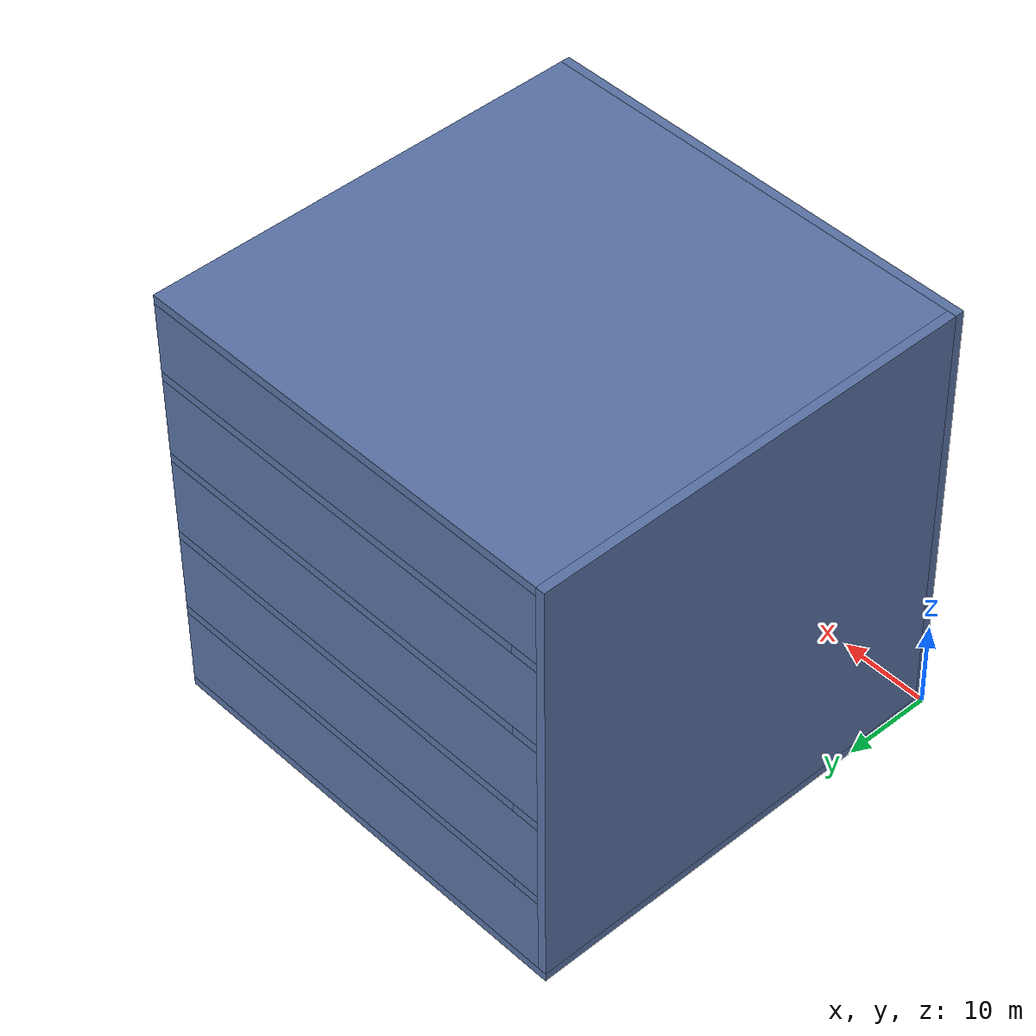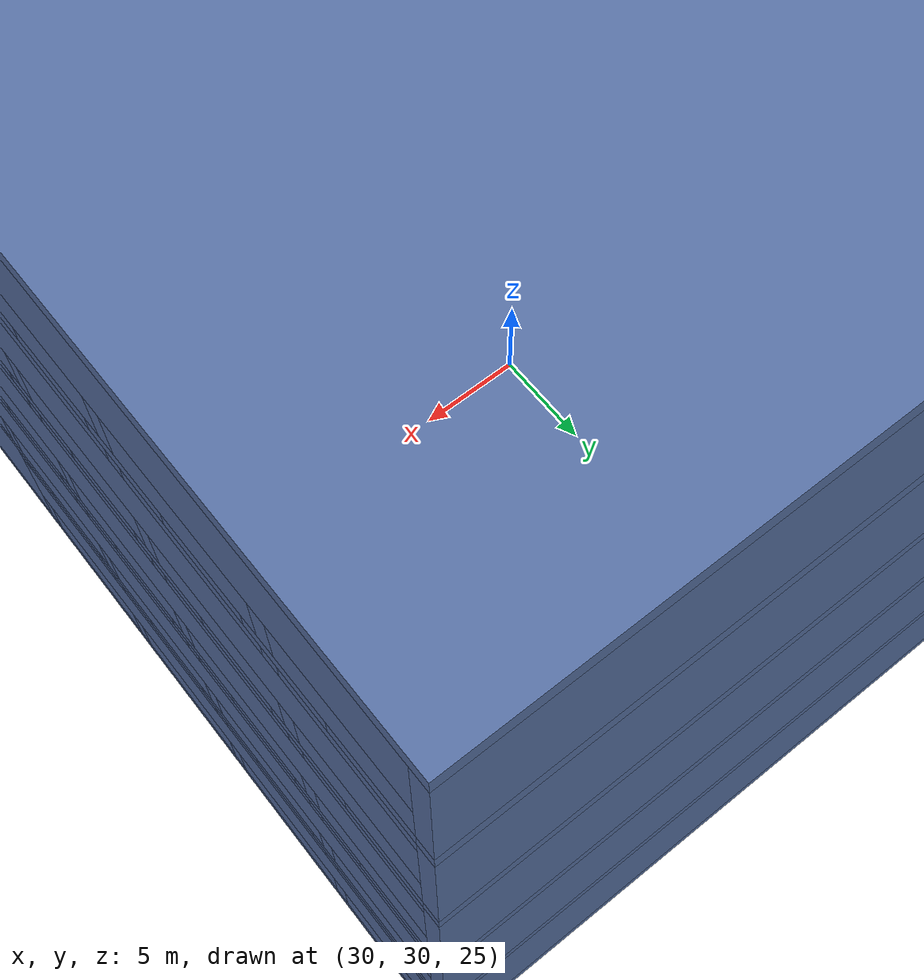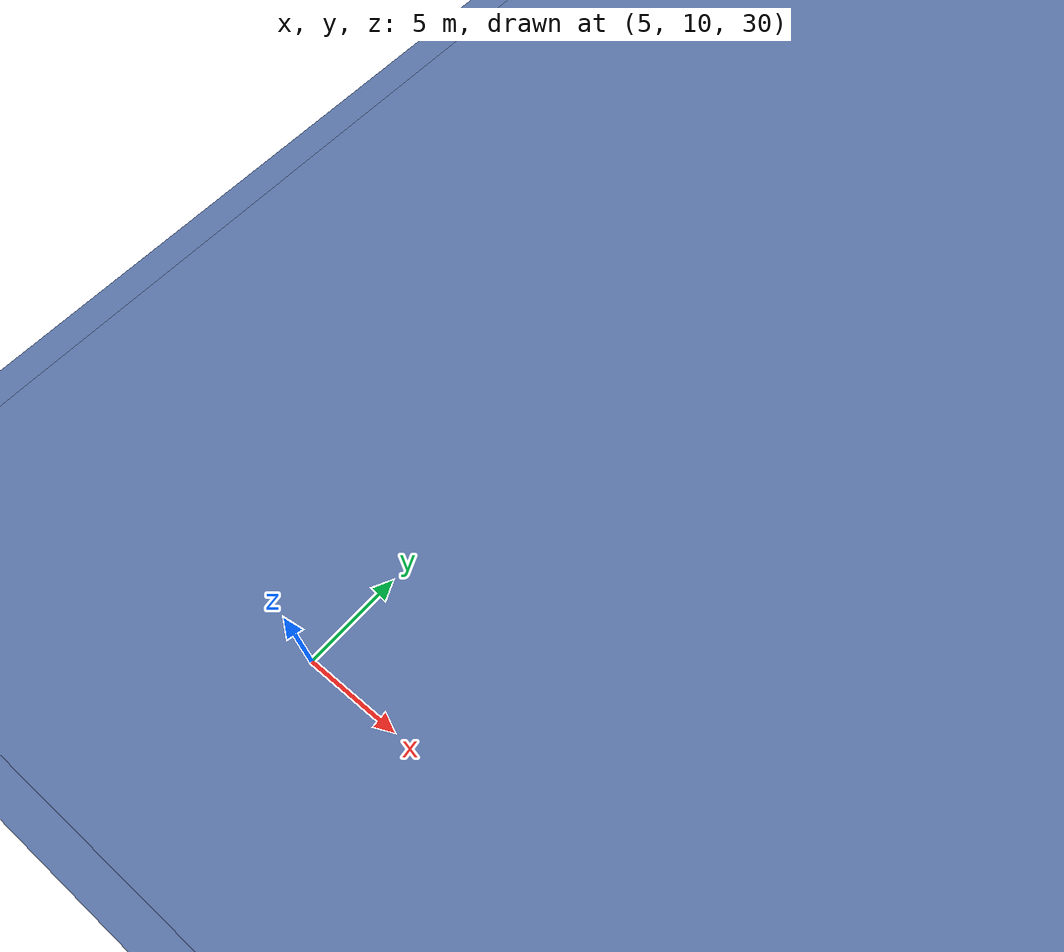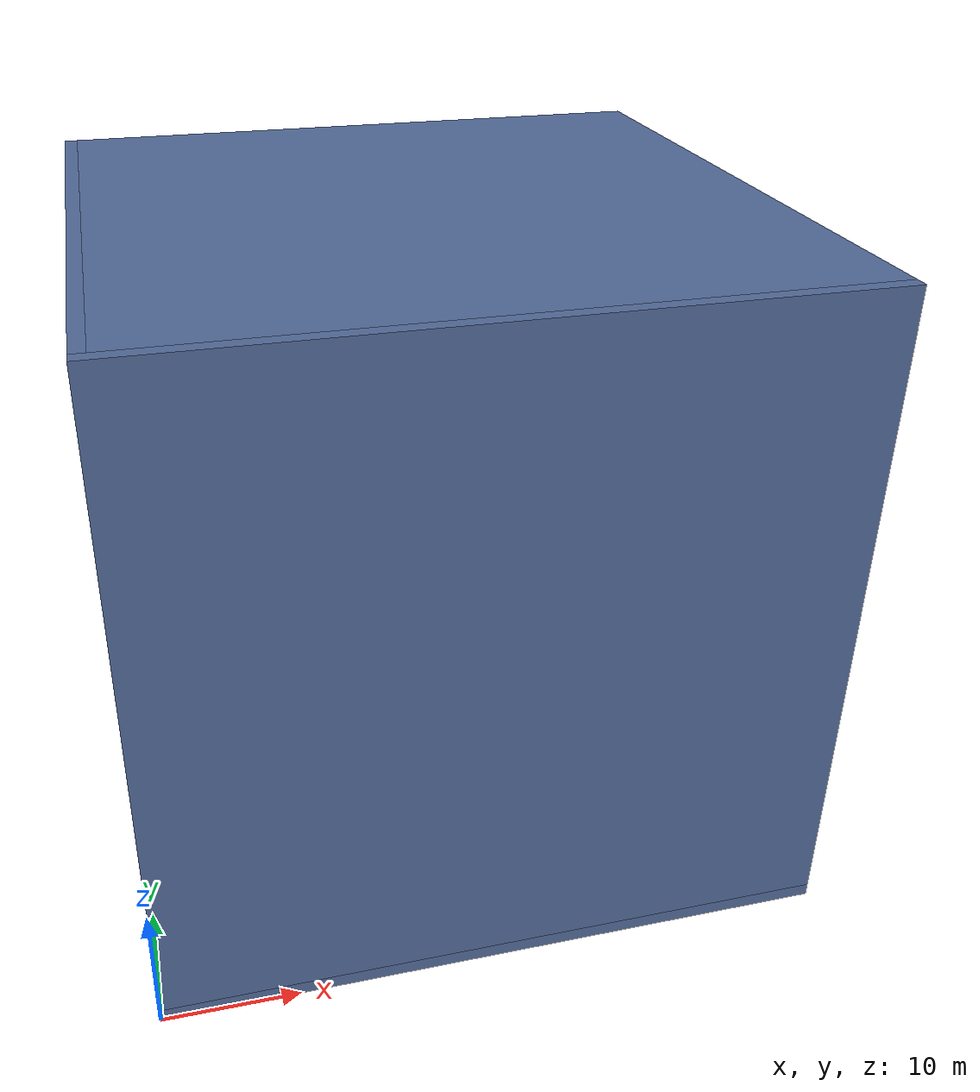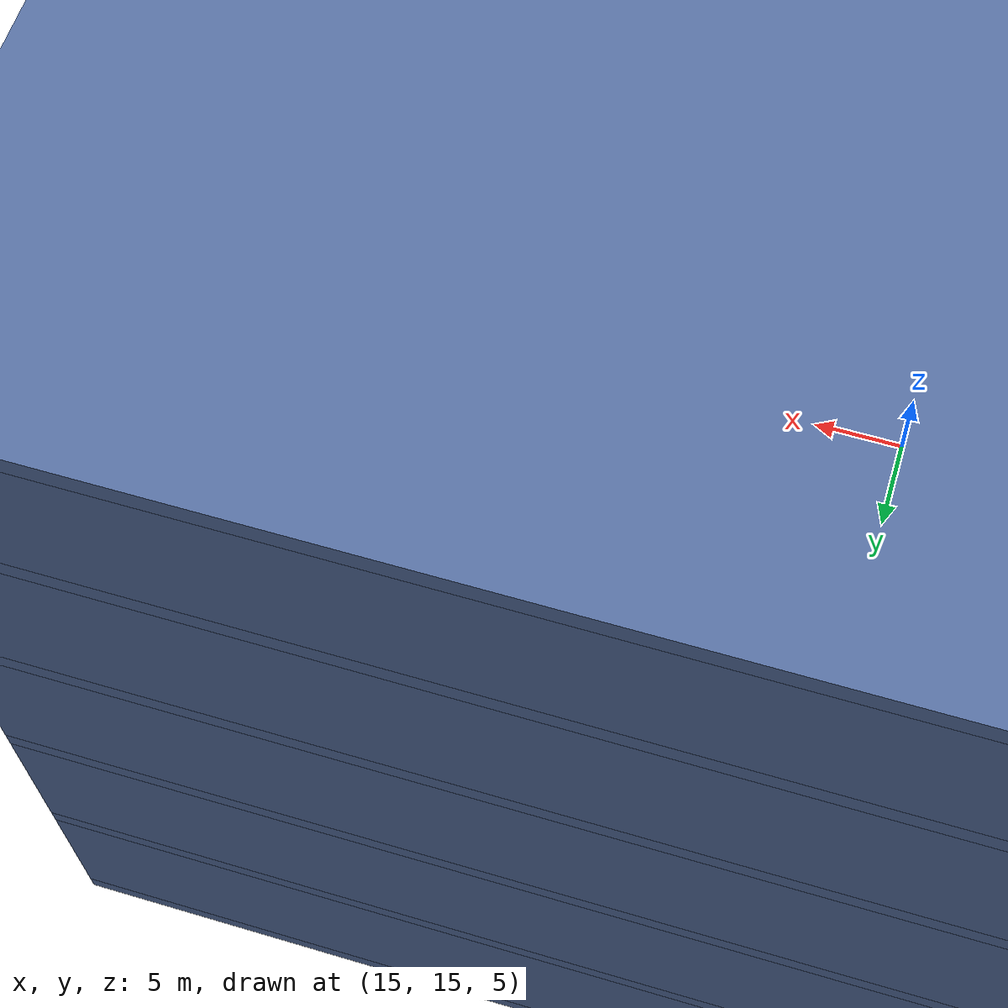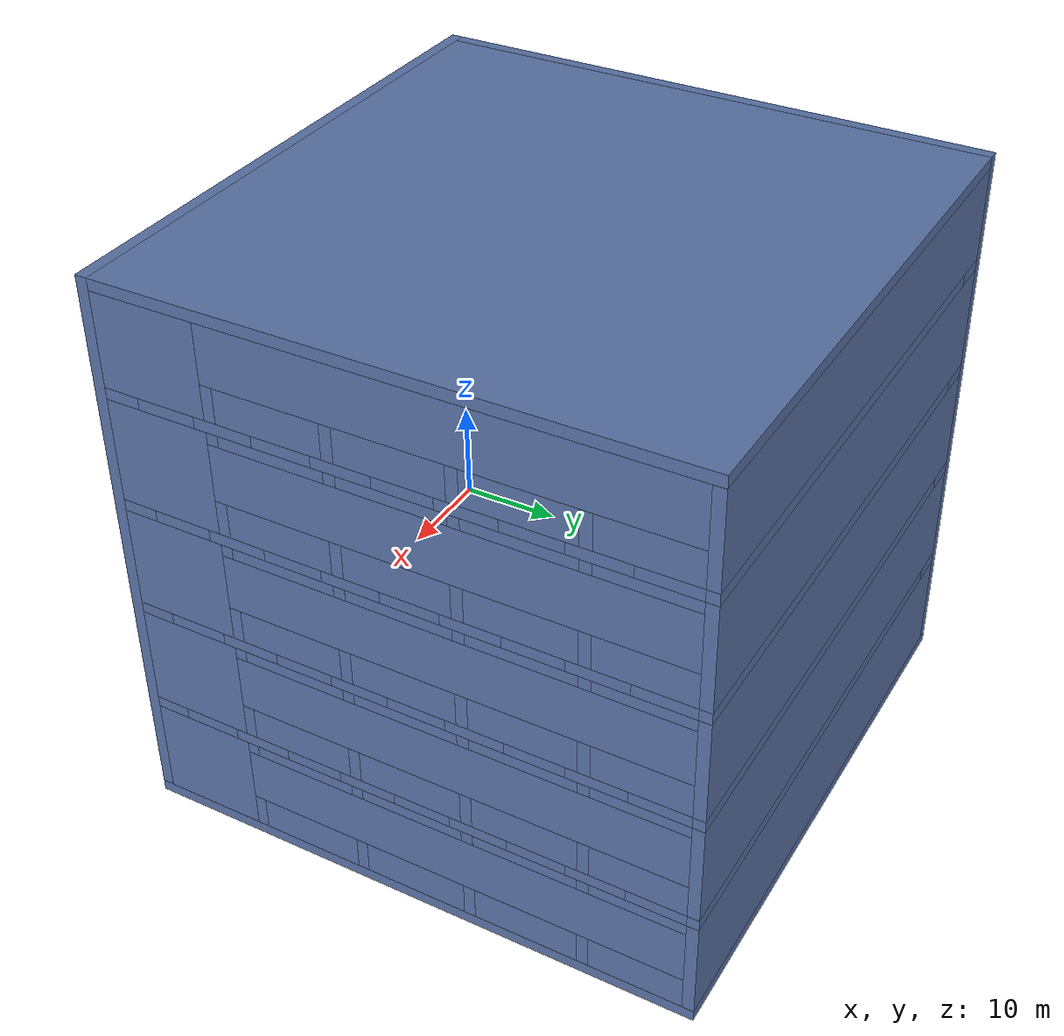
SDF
<sdf version='1.7'>
  <world name='default'>
    <light name='sun' type='directional'><cast_shadows>1</cast_shadows>
      <pose>25 25 60 0 0 0</pose><diffuse>0.9 0.9 0.9 1</diffuse><specular>0.2 0.2 0.2 1</specular>
      <attenuation><range>1000</range><constant>0.9</constant><linear>0.001</linear><quadratic>0.0001</quadratic></attenuation>
      <direction>-0.3 0.2 -0.9</direction></light>
    <gravity>0 0 -9.8</gravity>
    <physics type='ode'><max_step_size>0.004</max_step_size><real_time_factor>1</real_time_factor><real_time_update_rate>250</real_time_update_rate></physics>
    <plugin filename="ignition-gazebo-physics-system" name="gz::sim::systems::Physics"/>
    <plugin filename="ignition-gazebo-sensors-system" name="gz::sim::systems::Sensors"><render_engine>ogre2</render_engine></plugin>
    <plugin filename="ignition-gazebo-imu-system" name="gz::sim::systems::Imu"/>
    <plugin filename="ignition-gazebo-user-commands-system" name="gz::sim::systems::UserCommands"/>
    <plugin filename="ignition-gazebo-scene-broadcaster-system" name="gz::sim::systems::SceneBroadcaster"/>
    <scene><ambient>0.5 0.5 0.5 1</ambient><background>0.75 0.8 0.85 1</background><shadows>1</shadows></scene>
    <model name='racer_env'><static>1</static><pose>0 0 0 0 0 0</pose>
      <link name='b0'>
        <pose>25.000 25.000 0.500 0 0 0</pose>
        <collision name='c'><geometry><box><size>50.000 50.000 1.000</size></box></geometry></collision>
        <visual name='v'><geometry><box><size>50.000 50.000 1.000</size></box></geometry>
          <material><ambient>0.30 0.38 0.55 1</ambient><diffuse>0.35 0.45 0.65 1</diffuse></material>
        </visual>
      </link>
      <link name='b1'>
        <pose>25.000 0.500 25.500 0 0 0</pose>
        <collision name='c'><geometry><box><size>50.000 1.000 49.000</size></box></geometry></collision>
        <visual name='v'><geometry><box><size>50.000 1.000 49.000</size></box></geometry>
          <material><ambient>0.30 0.38 0.55 1</ambient><diffuse>0.35 0.45 0.65 1</diffuse></material>
        </visual>
      </link>
      <link name='b2'>
        <pose>0.500 25.500 25.500 0 0 0</pose>
        <collision name='c'><geometry><box><size>1.000 49.000 49.000</size></box></geometry></collision>
        <visual name='v'><geometry><box><size>1.000 49.000 49.000</size></box></geometry>
          <material><ambient>0.30 0.38 0.55 1</ambient><diffuse>0.35 0.45 0.65 1</diffuse></material>
        </visual>
      </link>
      <link name='b3'>
        <pose>25.500 2.500 10.500 0 0 0</pose>
        <collision name='c'><geometry><box><size>49.000 3.000 1.000</size></box></geometry></collision>
        <visual name='v'><geometry><box><size>49.000 3.000 1.000</size></box></geometry>
          <material><ambient>0.30 0.38 0.55 1</ambient><diffuse>0.35 0.45 0.65 1</diffuse></material>
        </visual>
      </link>
      <link name='b4'>
        <pose>25.500 2.500 20.500 0 0 0</pose>
        <collision name='c'><geometry><box><size>49.000 3.000 1.000</size></box></geometry></collision>
        <visual name='v'><geometry><box><size>49.000 3.000 1.000</size></box></geometry>
          <material><ambient>0.30 0.38 0.55 1</ambient><diffuse>0.35 0.45 0.65 1</diffuse></material>
        </visual>
      </link>
      <link name='b5'>
        <pose>25.500 2.500 30.500 0 0 0</pose>
        <collision name='c'><geometry><box><size>49.000 3.000 1.000</size></box></geometry></collision>
        <visual name='v'><geometry><box><size>49.000 3.000 1.000</size></box></geometry>
          <material><ambient>0.30 0.38 0.55 1</ambient><diffuse>0.35 0.45 0.65 1</diffuse></material>
        </visual>
      </link>
      <link name='b6'>
        <pose>25.500 2.500 40.500 0 0 0</pose>
        <collision name='c'><geometry><box><size>49.000 3.000 1.000</size></box></geometry></collision>
        <visual name='v'><geometry><box><size>49.000 3.000 1.000</size></box></geometry>
          <material><ambient>0.30 0.38 0.55 1</ambient><diffuse>0.35 0.45 0.65 1</diffuse></material>
        </visual>
      </link>
      <link name='b7'>
        <pose>25.500 25.500 49.500 0 0 0</pose>
        <collision name='c'><geometry><box><size>49.000 49.000 1.000</size></box></geometry></collision>
        <visual name='v'><geometry><box><size>49.000 49.000 1.000</size></box></geometry>
          <material><ambient>0.30 0.38 0.55 1</ambient><diffuse>0.35 0.45 0.65 1</diffuse></material>
        </visual>
      </link>
      <link name='b8'>
        <pose>2.500 27.000 10.500 0 0 0</pose>
        <collision name='c'><geometry><box><size>3.000 46.000 1.000</size></box></geometry></collision>
        <visual name='v'><geometry><box><size>3.000 46.000 1.000</size></box></geometry>
          <material><ambient>0.30 0.38 0.55 1</ambient><diffuse>0.35 0.45 0.65 1</diffuse></material>
        </visual>
      </link>
      <link name='b9'>
        <pose>2.500 27.000 20.500 0 0 0</pose>
        <collision name='c'><geometry><box><size>3.000 46.000 1.000</size></box></geometry></collision>
        <visual name='v'><geometry><box><size>3.000 46.000 1.000</size></box></geometry>
          <material><ambient>0.30 0.38 0.55 1</ambient><diffuse>0.35 0.45 0.65 1</diffuse></material>
        </visual>
      </link>
      <link name='b10'>
        <pose>2.500 27.000 30.500 0 0 0</pose>
        <collision name='c'><geometry><box><size>3.000 46.000 1.000</size></box></geometry></collision>
        <visual name='v'><geometry><box><size>3.000 46.000 1.000</size></box></geometry>
          <material><ambient>0.30 0.38 0.55 1</ambient><diffuse>0.35 0.45 0.65 1</diffuse></material>
        </visual>
      </link>
      <link name='b11'>
        <pose>2.500 27.000 40.500 0 0 0</pose>
        <collision name='c'><geometry><box><size>3.000 46.000 1.000</size></box></geometry></collision>
        <visual name='v'><geometry><box><size>3.000 46.000 1.000</size></box></geometry>
          <material><ambient>0.30 0.38 0.55 1</ambient><diffuse>0.35 0.45 0.65 1</diffuse></material>
        </visual>
      </link>
      <link name='b12'>
        <pose>25.500 10.500 2.500 0 0 0</pose>
        <collision name='c'><geometry><box><size>49.000 1.000 3.000</size></box></geometry></collision>
        <visual name='v'><geometry><box><size>49.000 1.000 3.000</size></box></geometry>
          <material><ambient>0.30 0.38 0.55 1</ambient><diffuse>0.35 0.45 0.65 1</diffuse></material>
        </visual>
      </link>
      <link name='b13'>
        <pose>2.500 10.500 7.000 0 0 0</pose>
        <collision name='c'><geometry><box><size>3.000 1.000 6.000</size></box></geometry></collision>
        <visual name='v'><geometry><box><size>3.000 1.000 6.000</size></box></geometry>
          <material><ambient>0.30 0.38 0.55 1</ambient><diffuse>0.35 0.45 0.65 1</diffuse></material>
        </visual>
      </link>
      <link name='b14'>
        <pose>25.500 10.500 12.500 0 0 0</pose>
        <collision name='c'><geometry><box><size>49.000 1.000 3.000</size></box></geometry></collision>
        <visual name='v'><geometry><box><size>49.000 1.000 3.000</size></box></geometry>
          <material><ambient>0.30 0.38 0.55 1</ambient><diffuse>0.35 0.45 0.65 1</diffuse></material>
        </visual>
      </link>
      <link name='b15'>
        <pose>2.500 10.500 17.000 0 0 0</pose>
        <collision name='c'><geometry><box><size>3.000 1.000 6.000</size></box></geometry></collision>
        <visual name='v'><geometry><box><size>3.000 1.000 6.000</size></box></geometry>
          <material><ambient>0.30 0.38 0.55 1</ambient><diffuse>0.35 0.45 0.65 1</diffuse></material>
        </visual>
      </link>
      <link name='b16'>
        <pose>25.500 10.500 22.500 0 0 0</pose>
        <collision name='c'><geometry><box><size>49.000 1.000 3.000</size></box></geometry></collision>
        <visual name='v'><geometry><box><size>49.000 1.000 3.000</size></box></geometry>
          <material><ambient>0.30 0.38 0.55 1</ambient><diffuse>0.35 0.45 0.65 1</diffuse></material>
        </visual>
      </link>
      <link name='b17'>
        <pose>2.500 10.500 27.000 0 0 0</pose>
        <collision name='c'><geometry><box><size>3.000 1.000 6.000</size></box></geometry></collision>
        <visual name='v'><geometry><box><size>3.000 1.000 6.000</size></box></geometry>
          <material><ambient>0.30 0.38 0.55 1</ambient><diffuse>0.35 0.45 0.65 1</diffuse></material>
        </visual>
      </link>
      <link name='b18'>
        <pose>25.500 10.500 32.500 0 0 0</pose>
        <collision name='c'><geometry><box><size>49.000 1.000 3.000</size></box></geometry></collision>
        <visual name='v'><geometry><box><size>49.000 1.000 3.000</size></box></geometry>
          <material><ambient>0.30 0.38 0.55 1</ambient><diffuse>0.35 0.45 0.65 1</diffuse></material>
        </visual>
      </link>
      <link name='b19'>
        <pose>2.500 10.500 37.000 0 0 0</pose>
        <collision name='c'><geometry><box><size>3.000 1.000 6.000</size></box></geometry></collision>
        <visual name='v'><geometry><box><size>3.000 1.000 6.000</size></box></geometry>
          <material><ambient>0.30 0.38 0.55 1</ambient><diffuse>0.35 0.45 0.65 1</diffuse></material>
        </visual>
      </link>
      <link name='b20'>
        <pose>25.500 10.500 42.500 0 0 0</pose>
        <collision name='c'><geometry><box><size>49.000 1.000 3.000</size></box></geometry></collision>
        <visual name='v'><geometry><box><size>49.000 1.000 3.000</size></box></geometry>
          <material><ambient>0.30 0.38 0.55 1</ambient><diffuse>0.35 0.45 0.65 1</diffuse></material>
        </visual>
      </link>
      <link name='b21'>
        <pose>2.500 10.500 46.500 0 0 0</pose>
        <collision name='c'><geometry><box><size>3.000 1.000 5.000</size></box></geometry></collision>
        <visual name='v'><geometry><box><size>3.000 1.000 5.000</size></box></geometry>
          <material><ambient>0.30 0.38 0.55 1</ambient><diffuse>0.35 0.45 0.65 1</diffuse></material>
        </visual>
      </link>
      <link name='b22'>
        <pose>25.500 20.500 2.500 0 0 0</pose>
        <collision name='c'><geometry><box><size>49.000 1.000 3.000</size></box></geometry></collision>
        <visual name='v'><geometry><box><size>49.000 1.000 3.000</size></box></geometry>
          <material><ambient>0.30 0.38 0.55 1</ambient><diffuse>0.35 0.45 0.65 1</diffuse></material>
        </visual>
      </link>
      <link name='b23'>
        <pose>2.500 20.500 7.000 0 0 0</pose>
        <collision name='c'><geometry><box><size>3.000 1.000 6.000</size></box></geometry></collision>
        <visual name='v'><geometry><box><size>3.000 1.000 6.000</size></box></geometry>
          <material><ambient>0.30 0.38 0.55 1</ambient><diffuse>0.35 0.45 0.65 1</diffuse></material>
        </visual>
      </link>
      <link name='b24'>
        <pose>25.500 20.500 12.500 0 0 0</pose>
        <collision name='c'><geometry><box><size>49.000 1.000 3.000</size></box></geometry></collision>
        <visual name='v'><geometry><box><size>49.000 1.000 3.000</size></box></geometry>
          <material><ambient>0.30 0.38 0.55 1</ambient><diffuse>0.35 0.45 0.65 1</diffuse></material>
        </visual>
      </link>
      <link name='b25'>
        <pose>2.500 20.500 17.000 0 0 0</pose>
        <collision name='c'><geometry><box><size>3.000 1.000 6.000</size></box></geometry></collision>
        <visual name='v'><geometry><box><size>3.000 1.000 6.000</size></box></geometry>
          <material><ambient>0.30 0.38 0.55 1</ambient><diffuse>0.35 0.45 0.65 1</diffuse></material>
        </visual>
      </link>
      <link name='b26'>
        <pose>25.500 20.500 22.500 0 0 0</pose>
        <collision name='c'><geometry><box><size>49.000 1.000 3.000</size></box></geometry></collision>
        <visual name='v'><geometry><box><size>49.000 1.000 3.000</size></box></geometry>
          <material><ambient>0.30 0.38 0.55 1</ambient><diffuse>0.35 0.45 0.65 1</diffuse></material>
        </visual>
      </link>
      <link name='b27'>
        <pose>2.500 20.500 27.000 0 0 0</pose>
        <collision name='c'><geometry><box><size>3.000 1.000 6.000</size></box></geometry></collision>
        <visual name='v'><geometry><box><size>3.000 1.000 6.000</size></box></geometry>
          <material><ambient>0.30 0.38 0.55 1</ambient><diffuse>0.35 0.45 0.65 1</diffuse></material>
        </visual>
      </link>
      <link name='b28'>
        <pose>25.500 20.500 32.500 0 0 0</pose>
        <collision name='c'><geometry><box><size>49.000 1.000 3.000</size></box></geometry></collision>
        <visual name='v'><geometry><box><size>49.000 1.000 3.000</size></box></geometry>
          <material><ambient>0.30 0.38 0.55 1</ambient><diffuse>0.35 0.45 0.65 1</diffuse></material>
        </visual>
      </link>
      <link name='b29'>
        <pose>2.500 20.500 37.000 0 0 0</pose>
        <collision name='c'><geometry><box><size>3.000 1.000 6.000</size></box></geometry></collision>
        <visual name='v'><geometry><box><size>3.000 1.000 6.000</size></box></geometry>
          <material><ambient>0.30 0.38 0.55 1</ambient><diffuse>0.35 0.45 0.65 1</diffuse></material>
        </visual>
      </link>
      <link name='b30'>
        <pose>25.500 20.500 42.500 0 0 0</pose>
        <collision name='c'><geometry><box><size>49.000 1.000 3.000</size></box></geometry></collision>
        <visual name='v'><geometry><box><size>49.000 1.000 3.000</size></box></geometry>
          <material><ambient>0.30 0.38 0.55 1</ambient><diffuse>0.35 0.45 0.65 1</diffuse></material>
        </visual>
      </link>
      <link name='b31'>
        <pose>2.500 20.500 46.500 0 0 0</pose>
        <collision name='c'><geometry><box><size>3.000 1.000 5.000</size></box></geometry></collision>
        <visual name='v'><geometry><box><size>3.000 1.000 5.000</size></box></geometry>
          <material><ambient>0.30 0.38 0.55 1</ambient><diffuse>0.35 0.45 0.65 1</diffuse></material>
        </visual>
      </link>
      <link name='b32'>
        <pose>25.500 30.500 2.500 0 0 0</pose>
        <collision name='c'><geometry><box><size>49.000 1.000 3.000</size></box></geometry></collision>
        <visual name='v'><geometry><box><size>49.000 1.000 3.000</size></box></geometry>
          <material><ambient>0.30 0.38 0.55 1</ambient><diffuse>0.35 0.45 0.65 1</diffuse></material>
        </visual>
      </link>
      <link name='b33'>
        <pose>2.500 30.500 7.000 0 0 0</pose>
        <collision name='c'><geometry><box><size>3.000 1.000 6.000</size></box></geometry></collision>
        <visual name='v'><geometry><box><size>3.000 1.000 6.000</size></box></geometry>
          <material><ambient>0.30 0.38 0.55 1</ambient><diffuse>0.35 0.45 0.65 1</diffuse></material>
        </visual>
      </link>
      <link name='b34'>
        <pose>25.500 30.500 12.500 0 0 0</pose>
        <collision name='c'><geometry><box><size>49.000 1.000 3.000</size></box></geometry></collision>
        <visual name='v'><geometry><box><size>49.000 1.000 3.000</size></box></geometry>
          <material><ambient>0.30 0.38 0.55 1</ambient><diffuse>0.35 0.45 0.65 1</diffuse></material>
        </visual>
      </link>
      <link name='b35'>
        <pose>2.500 30.500 17.000 0 0 0</pose>
        <collision name='c'><geometry><box><size>3.000 1.000 6.000</size></box></geometry></collision>
        <visual name='v'><geometry><box><size>3.000 1.000 6.000</size></box></geometry>
          <material><ambient>0.30 0.38 0.55 1</ambient><diffuse>0.35 0.45 0.65 1</diffuse></material>
        </visual>
      </link>
      <link name='b36'>
        <pose>25.500 30.500 22.500 0 0 0</pose>
        <collision name='c'><geometry><box><size>49.000 1.000 3.000</size></box></geometry></collision>
        <visual name='v'><geometry><box><size>49.000 1.000 3.000</size></box></geometry>
          <material><ambient>0.30 0.38 0.55 1</ambient><diffuse>0.35 0.45 0.65 1</diffuse></material>
        </visual>
      </link>
      <link name='b37'>
        <pose>2.500 30.500 27.000 0 0 0</pose>
        <collision name='c'><geometry><box><size>3.000 1.000 6.000</size></box></geometry></collision>
        <visual name='v'><geometry><box><size>3.000 1.000 6.000</size></box></geometry>
          <material><ambient>0.30 0.38 0.55 1</ambient><diffuse>0.35 0.45 0.65 1</diffuse></material>
        </visual>
      </link>
      <link name='b38'>
        <pose>25.500 30.500 32.500 0 0 0</pose>
        <collision name='c'><geometry><box><size>49.000 1.000 3.000</size></box></geometry></collision>
        <visual name='v'><geometry><box><size>49.000 1.000 3.000</size></box></geometry>
          <material><ambient>0.30 0.38 0.55 1</ambient><diffuse>0.35 0.45 0.65 1</diffuse></material>
        </visual>
      </link>
      <link name='b39'>
        <pose>2.500 30.500 37.000 0 0 0</pose>
        <collision name='c'><geometry><box><size>3.000 1.000 6.000</size></box></geometry></collision>
        <visual name='v'><geometry><box><size>3.000 1.000 6.000</size></box></geometry>
          <material><ambient>0.30 0.38 0.55 1</ambient><diffuse>0.35 0.45 0.65 1</diffuse></material>
        </visual>
      </link>
      <link name='b40'>
        <pose>25.500 30.500 42.500 0 0 0</pose>
        <collision name='c'><geometry><box><size>49.000 1.000 3.000</size></box></geometry></collision>
        <visual name='v'><geometry><box><size>49.000 1.000 3.000</size></box></geometry>
          <material><ambient>0.30 0.38 0.55 1</ambient><diffuse>0.35 0.45 0.65 1</diffuse></material>
        </visual>
      </link>
      <link name='b41'>
        <pose>2.500 30.500 46.500 0 0 0</pose>
        <collision name='c'><geometry><box><size>3.000 1.000 5.000</size></box></geometry></collision>
        <visual name='v'><geometry><box><size>3.000 1.000 5.000</size></box></geometry>
          <material><ambient>0.30 0.38 0.55 1</ambient><diffuse>0.35 0.45 0.65 1</diffuse></material>
        </visual>
      </link>
      <link name='b42'>
        <pose>25.500 40.500 2.500 0 0 0</pose>
        <collision name='c'><geometry><box><size>49.000 1.000 3.000</size></box></geometry></collision>
        <visual name='v'><geometry><box><size>49.000 1.000 3.000</size></box></geometry>
          <material><ambient>0.30 0.38 0.55 1</ambient><diffuse>0.35 0.45 0.65 1</diffuse></material>
        </visual>
      </link>
      <link name='b43'>
        <pose>2.500 40.500 7.000 0 0 0</pose>
        <collision name='c'><geometry><box><size>3.000 1.000 6.000</size></box></geometry></collision>
        <visual name='v'><geometry><box><size>3.000 1.000 6.000</size></box></geometry>
          <material><ambient>0.30 0.38 0.55 1</ambient><diffuse>0.35 0.45 0.65 1</diffuse></material>
        </visual>
      </link>
      <link name='b44'>
        <pose>25.500 40.500 12.500 0 0 0</pose>
        <collision name='c'><geometry><box><size>49.000 1.000 3.000</size></box></geometry></collision>
        <visual name='v'><geometry><box><size>49.000 1.000 3.000</size></box></geometry>
          <material><ambient>0.30 0.38 0.55 1</ambient><diffuse>0.35 0.45 0.65 1</diffuse></material>
        </visual>
      </link>
      <link name='b45'>
        <pose>2.500 40.500 17.000 0 0 0</pose>
        <collision name='c'><geometry><box><size>3.000 1.000 6.000</size></box></geometry></collision>
        <visual name='v'><geometry><box><size>3.000 1.000 6.000</size></box></geometry>
          <material><ambient>0.30 0.38 0.55 1</ambient><diffuse>0.35 0.45 0.65 1</diffuse></material>
        </visual>
      </link>
      <link name='b46'>
        <pose>25.500 40.500 22.500 0 0 0</pose>
        <collision name='c'><geometry><box><size>49.000 1.000 3.000</size></box></geometry></collision>
        <visual name='v'><geometry><box><size>49.000 1.000 3.000</size></box></geometry>
          <material><ambient>0.30 0.38 0.55 1</ambient><diffuse>0.35 0.45 0.65 1</diffuse></material>
        </visual>
      </link>
      <link name='b47'>
        <pose>2.500 40.500 27.000 0 0 0</pose>
        <collision name='c'><geometry><box><size>3.000 1.000 6.000</size></box></geometry></collision>
        <visual name='v'><geometry><box><size>3.000 1.000 6.000</size></box></geometry>
          <material><ambient>0.30 0.38 0.55 1</ambient><diffuse>0.35 0.45 0.65 1</diffuse></material>
        </visual>
      </link>
      <link name='b48'>
        <pose>25.500 40.500 32.500 0 0 0</pose>
        <collision name='c'><geometry><box><size>49.000 1.000 3.000</size></box></geometry></collision>
        <visual name='v'><geometry><box><size>49.000 1.000 3.000</size></box></geometry>
          <material><ambient>0.30 0.38 0.55 1</ambient><diffuse>0.35 0.45 0.65 1</diffuse></material>
        </visual>
      </link>
      <link name='b49'>
        <pose>2.500 40.500 37.000 0 0 0</pose>
        <collision name='c'><geometry><box><size>3.000 1.000 6.000</size></box></geometry></collision>
        <visual name='v'><geometry><box><size>3.000 1.000 6.000</size></box></geometry>
          <material><ambient>0.30 0.38 0.55 1</ambient><diffuse>0.35 0.45 0.65 1</diffuse></material>
        </visual>
      </link>
      <link name='b50'>
        <pose>25.500 40.500 42.500 0 0 0</pose>
        <collision name='c'><geometry><box><size>49.000 1.000 3.000</size></box></geometry></collision>
        <visual name='v'><geometry><box><size>49.000 1.000 3.000</size></box></geometry>
          <material><ambient>0.30 0.38 0.55 1</ambient><diffuse>0.35 0.45 0.65 1</diffuse></material>
        </visual>
      </link>
      <link name='b51'>
        <pose>2.500 40.500 46.500 0 0 0</pose>
        <collision name='c'><geometry><box><size>3.000 1.000 5.000</size></box></geometry></collision>
        <visual name='v'><geometry><box><size>3.000 1.000 5.000</size></box></geometry>
          <material><ambient>0.30 0.38 0.55 1</ambient><diffuse>0.35 0.45 0.65 1</diffuse></material>
        </visual>
      </link>
      <link name='b52'>
        <pose>25.500 49.500 5.500 0 0 0</pose>
        <collision name='c'><geometry><box><size>49.000 1.000 9.000</size></box></geometry></collision>
        <visual name='v'><geometry><box><size>49.000 1.000 9.000</size></box></geometry>
          <material><ambient>0.30 0.38 0.55 1</ambient><diffuse>0.35 0.45 0.65 1</diffuse></material>
        </visual>
      </link>
      <link name='b53'>
        <pose>25.500 49.500 15.500 0 0 0</pose>
        <collision name='c'><geometry><box><size>49.000 1.000 9.000</size></box></geometry></collision>
        <visual name='v'><geometry><box><size>49.000 1.000 9.000</size></box></geometry>
          <material><ambient>0.30 0.38 0.55 1</ambient><diffuse>0.35 0.45 0.65 1</diffuse></material>
        </visual>
      </link>
      <link name='b54'>
        <pose>25.500 49.500 25.500 0 0 0</pose>
        <collision name='c'><geometry><box><size>49.000 1.000 9.000</size></box></geometry></collision>
        <visual name='v'><geometry><box><size>49.000 1.000 9.000</size></box></geometry>
          <material><ambient>0.30 0.38 0.55 1</ambient><diffuse>0.35 0.45 0.65 1</diffuse></material>
        </visual>
      </link>
      <link name='b55'>
        <pose>25.500 49.500 35.500 0 0 0</pose>
        <collision name='c'><geometry><box><size>49.000 1.000 9.000</size></box></geometry></collision>
        <visual name='v'><geometry><box><size>49.000 1.000 9.000</size></box></geometry>
          <material><ambient>0.30 0.38 0.55 1</ambient><diffuse>0.35 0.45 0.65 1</diffuse></material>
        </visual>
      </link>
      <link name='b56'>
        <pose>25.500 49.500 45.000 0 0 0</pose>
        <collision name='c'><geometry><box><size>49.000 1.000 8.000</size></box></geometry></collision>
        <visual name='v'><geometry><box><size>49.000 1.000 8.000</size></box></geometry>
          <material><ambient>0.30 0.38 0.55 1</ambient><diffuse>0.35 0.45 0.65 1</diffuse></material>
        </visual>
      </link>
      <link name='b57'>
        <pose>4.500 29.500 38.500 0 0 0</pose>
        <collision name='c'><geometry><box><size>5.000 1.000 3.000</size></box></geometry></collision>
        <visual name='v'><geometry><box><size>5.000 1.000 3.000</size></box></geometry>
          <material><ambient>0.30 0.38 0.55 1</ambient><diffuse>0.35 0.45 0.65 1</diffuse></material>
        </visual>
      </link>
      <link name='b58'>
        <pose>4.500 31.500 38.500 0 0 0</pose>
        <collision name='c'><geometry><box><size>5.000 1.000 3.000</size></box></geometry></collision>
        <visual name='v'><geometry><box><size>5.000 1.000 3.000</size></box></geometry>
          <material><ambient>0.30 0.38 0.55 1</ambient><diffuse>0.35 0.45 0.65 1</diffuse></material>
        </visual>
      </link>
      <link name='b59'>
        <pose>27.000 11.500 10.500 0 0 0</pose>
        <collision name='c'><geometry><box><size>46.000 5.000 1.000</size></box></geometry></collision>
        <visual name='v'><geometry><box><size>46.000 5.000 1.000</size></box></geometry>
          <material><ambient>0.30 0.38 0.55 1</ambient><diffuse>0.35 0.45 0.65 1</diffuse></material>
        </visual>
      </link>
      <link name='b60'>
        <pose>27.000 11.500 20.500 0 0 0</pose>
        <collision name='c'><geometry><box><size>46.000 5.000 1.000</size></box></geometry></collision>
        <visual name='v'><geometry><box><size>46.000 5.000 1.000</size></box></geometry>
          <material><ambient>0.30 0.38 0.55 1</ambient><diffuse>0.35 0.45 0.65 1</diffuse></material>
        </visual>
      </link>
      <link name='b61'>
        <pose>27.000 11.500 30.500 0 0 0</pose>
        <collision name='c'><geometry><box><size>46.000 5.000 1.000</size></box></geometry></collision>
        <visual name='v'><geometry><box><size>46.000 5.000 1.000</size></box></geometry>
          <material><ambient>0.30 0.38 0.55 1</ambient><diffuse>0.35 0.45 0.65 1</diffuse></material>
        </visual>
      </link>
      <link name='b62'>
        <pose>27.000 11.500 40.500 0 0 0</pose>
        <collision name='c'><geometry><box><size>46.000 5.000 1.000</size></box></geometry></collision>
        <visual name='v'><geometry><box><size>46.000 5.000 1.000</size></box></geometry>
          <material><ambient>0.30 0.38 0.55 1</ambient><diffuse>0.35 0.45 0.65 1</diffuse></material>
        </visual>
      </link>
      <link name='b63'>
        <pose>27.000 10.500 9.500 0 0 0</pose>
        <collision name='c'><geometry><box><size>46.000 1.000 1.000</size></box></geometry></collision>
        <visual name='v'><geometry><box><size>46.000 1.000 1.000</size></box></geometry>
          <material><ambient>0.30 0.38 0.55 1</ambient><diffuse>0.35 0.45 0.65 1</diffuse></material>
        </visual>
      </link>
      <link name='b64'>
        <pose>27.000 10.500 19.500 0 0 0</pose>
        <collision name='c'><geometry><box><size>46.000 1.000 1.000</size></box></geometry></collision>
        <visual name='v'><geometry><box><size>46.000 1.000 1.000</size></box></geometry>
          <material><ambient>0.30 0.38 0.55 1</ambient><diffuse>0.35 0.45 0.65 1</diffuse></material>
        </visual>
      </link>
      <link name='b65'>
        <pose>27.000 10.500 29.500 0 0 0</pose>
        <collision name='c'><geometry><box><size>46.000 1.000 1.000</size></box></geometry></collision>
        <visual name='v'><geometry><box><size>46.000 1.000 1.000</size></box></geometry>
          <material><ambient>0.30 0.38 0.55 1</ambient><diffuse>0.35 0.45 0.65 1</diffuse></material>
        </visual>
      </link>
      <link name='b66'>
        <pose>27.000 10.500 39.500 0 0 0</pose>
        <collision name='c'><geometry><box><size>46.000 1.000 1.000</size></box></geometry></collision>
        <visual name='v'><geometry><box><size>46.000 1.000 1.000</size></box></geometry>
          <material><ambient>0.30 0.38 0.55 1</ambient><diffuse>0.35 0.45 0.65 1</diffuse></material>
        </visual>
      </link>
      <link name='b67'>
        <pose>27.000 21.500 10.500 0 0 0</pose>
        <collision name='c'><geometry><box><size>46.000 5.000 1.000</size></box></geometry></collision>
        <visual name='v'><geometry><box><size>46.000 5.000 1.000</size></box></geometry>
          <material><ambient>0.30 0.38 0.55 1</ambient><diffuse>0.35 0.45 0.65 1</diffuse></material>
        </visual>
      </link>
      <link name='b68'>
        <pose>27.000 21.500 20.500 0 0 0</pose>
        <collision name='c'><geometry><box><size>46.000 5.000 1.000</size></box></geometry></collision>
        <visual name='v'><geometry><box><size>46.000 5.000 1.000</size></box></geometry>
          <material><ambient>0.30 0.38 0.55 1</ambient><diffuse>0.35 0.45 0.65 1</diffuse></material>
        </visual>
      </link>
      <link name='b69'>
        <pose>27.000 21.500 30.500 0 0 0</pose>
        <collision name='c'><geometry><box><size>46.000 5.000 1.000</size></box></geometry></collision>
        <visual name='v'><geometry><box><size>46.000 5.000 1.000</size></box></geometry>
          <material><ambient>0.30 0.38 0.55 1</ambient><diffuse>0.35 0.45 0.65 1</diffuse></material>
        </visual>
      </link>
      <link name='b70'>
        <pose>27.000 21.500 40.500 0 0 0</pose>
        <collision name='c'><geometry><box><size>46.000 5.000 1.000</size></box></geometry></collision>
        <visual name='v'><geometry><box><size>46.000 5.000 1.000</size></box></geometry>
          <material><ambient>0.30 0.38 0.55 1</ambient><diffuse>0.35 0.45 0.65 1</diffuse></material>
        </visual>
      </link>
      <link name='b71'>
        <pose>27.000 20.500 9.500 0 0 0</pose>
        <collision name='c'><geometry><box><size>46.000 1.000 1.000</size></box></geometry></collision>
        <visual name='v'><geometry><box><size>46.000 1.000 1.000</size></box></geometry>
          <material><ambient>0.30 0.38 0.55 1</ambient><diffuse>0.35 0.45 0.65 1</diffuse></material>
        </visual>
      </link>
      <link name='b72'>
        <pose>27.000 20.500 19.500 0 0 0</pose>
        <collision name='c'><geometry><box><size>46.000 1.000 1.000</size></box></geometry></collision>
        <visual name='v'><geometry><box><size>46.000 1.000 1.000</size></box></geometry>
          <material><ambient>0.30 0.38 0.55 1</ambient><diffuse>0.35 0.45 0.65 1</diffuse></material>
        </visual>
      </link>
      <link name='b73'>
        <pose>27.000 20.500 29.500 0 0 0</pose>
        <collision name='c'><geometry><box><size>46.000 1.000 1.000</size></box></geometry></collision>
        <visual name='v'><geometry><box><size>46.000 1.000 1.000</size></box></geometry>
          <material><ambient>0.30 0.38 0.55 1</ambient><diffuse>0.35 0.45 0.65 1</diffuse></material>
        </visual>
      </link>
      <link name='b74'>
        <pose>27.000 20.500 39.500 0 0 0</pose>
        <collision name='c'><geometry><box><size>46.000 1.000 1.000</size></box></geometry></collision>
        <visual name='v'><geometry><box><size>46.000 1.000 1.000</size></box></geometry>
          <material><ambient>0.30 0.38 0.55 1</ambient><diffuse>0.35 0.45 0.65 1</diffuse></material>
        </visual>
      </link>
      <link name='b75'>
        <pose>27.000 31.500 10.500 0 0 0</pose>
        <collision name='c'><geometry><box><size>46.000 5.000 1.000</size></box></geometry></collision>
        <visual name='v'><geometry><box><size>46.000 5.000 1.000</size></box></geometry>
          <material><ambient>0.30 0.38 0.55 1</ambient><diffuse>0.35 0.45 0.65 1</diffuse></material>
        </visual>
      </link>
      <link name='b76'>
        <pose>27.000 31.500 20.500 0 0 0</pose>
        <collision name='c'><geometry><box><size>46.000 5.000 1.000</size></box></geometry></collision>
        <visual name='v'><geometry><box><size>46.000 5.000 1.000</size></box></geometry>
          <material><ambient>0.30 0.38 0.55 1</ambient><diffuse>0.35 0.45 0.65 1</diffuse></material>
        </visual>
      </link>
      <link name='b77'>
        <pose>27.000 31.500 30.500 0 0 0</pose>
        <collision name='c'><geometry><box><size>46.000 5.000 1.000</size></box></geometry></collision>
        <visual name='v'><geometry><box><size>46.000 5.000 1.000</size></box></geometry>
          <material><ambient>0.30 0.38 0.55 1</ambient><diffuse>0.35 0.45 0.65 1</diffuse></material>
        </visual>
      </link>
      <link name='b78'>
        <pose>27.000 31.500 40.500 0 0 0</pose>
        <collision name='c'><geometry><box><size>46.000 5.000 1.000</size></box></geometry></collision>
        <visual name='v'><geometry><box><size>46.000 5.000 1.000</size></box></geometry>
          <material><ambient>0.30 0.38 0.55 1</ambient><diffuse>0.35 0.45 0.65 1</diffuse></material>
        </visual>
      </link>
      <link name='b79'>
        <pose>27.000 30.500 9.500 0 0 0</pose>
        <collision name='c'><geometry><box><size>46.000 1.000 1.000</size></box></geometry></collision>
        <visual name='v'><geometry><box><size>46.000 1.000 1.000</size></box></geometry>
          <material><ambient>0.30 0.38 0.55 1</ambient><diffuse>0.35 0.45 0.65 1</diffuse></material>
        </visual>
      </link>
      <link name='b80'>
        <pose>27.000 30.500 19.500 0 0 0</pose>
        <collision name='c'><geometry><box><size>46.000 1.000 1.000</size></box></geometry></collision>
        <visual name='v'><geometry><box><size>46.000 1.000 1.000</size></box></geometry>
          <material><ambient>0.30 0.38 0.55 1</ambient><diffuse>0.35 0.45 0.65 1</diffuse></material>
        </visual>
      </link>
      <link name='b81'>
        <pose>27.000 30.500 29.500 0 0 0</pose>
        <collision name='c'><geometry><box><size>46.000 1.000 1.000</size></box></geometry></collision>
        <visual name='v'><geometry><box><size>46.000 1.000 1.000</size></box></geometry>
          <material><ambient>0.30 0.38 0.55 1</ambient><diffuse>0.35 0.45 0.65 1</diffuse></material>
        </visual>
      </link>
      <link name='b82'>
        <pose>5.500 30.500 38.500 0 0 0</pose>
        <collision name='c'><geometry><box><size>3.000 1.000 3.000</size></box></geometry></collision>
        <visual name='v'><geometry><box><size>3.000 1.000 3.000</size></box></geometry>
          <material><ambient>0.30 0.38 0.55 1</ambient><diffuse>0.35 0.45 0.65 1</diffuse></material>
        </visual>
      </link>
      <link name='b83'>
        <pose>6.500 32.500 19.500 0 0 0</pose>
        <collision name='c'><geometry><box><size>5.000 3.000 1.000</size></box></geometry></collision>
        <visual name='v'><geometry><box><size>5.000 3.000 1.000</size></box></geometry>
          <material><ambient>0.30 0.38 0.55 1</ambient><diffuse>0.35 0.45 0.65 1</diffuse></material>
        </visual>
      </link>
      <link name='b84'>
        <pose>27.000 41.500 10.500 0 0 0</pose>
        <collision name='c'><geometry><box><size>46.000 5.000 1.000</size></box></geometry></collision>
        <visual name='v'><geometry><box><size>46.000 5.000 1.000</size></box></geometry>
          <material><ambient>0.30 0.38 0.55 1</ambient><diffuse>0.35 0.45 0.65 1</diffuse></material>
        </visual>
      </link>
      <link name='b85'>
        <pose>27.000 41.500 20.500 0 0 0</pose>
        <collision name='c'><geometry><box><size>46.000 5.000 1.000</size></box></geometry></collision>
        <visual name='v'><geometry><box><size>46.000 5.000 1.000</size></box></geometry>
          <material><ambient>0.30 0.38 0.55 1</ambient><diffuse>0.35 0.45 0.65 1</diffuse></material>
        </visual>
      </link>
      <link name='b86'>
        <pose>27.000 41.500 30.500 0 0 0</pose>
        <collision name='c'><geometry><box><size>46.000 5.000 1.000</size></box></geometry></collision>
        <visual name='v'><geometry><box><size>46.000 5.000 1.000</size></box></geometry>
          <material><ambient>0.30 0.38 0.55 1</ambient><diffuse>0.35 0.45 0.65 1</diffuse></material>
        </visual>
      </link>
      <link name='b87'>
        <pose>27.000 41.500 40.500 0 0 0</pose>
        <collision name='c'><geometry><box><size>46.000 5.000 1.000</size></box></geometry></collision>
        <visual name='v'><geometry><box><size>46.000 5.000 1.000</size></box></geometry>
          <material><ambient>0.30 0.38 0.55 1</ambient><diffuse>0.35 0.45 0.65 1</diffuse></material>
        </visual>
      </link>
      <link name='b88'>
        <pose>27.000 40.500 9.500 0 0 0</pose>
        <collision name='c'><geometry><box><size>46.000 1.000 1.000</size></box></geometry></collision>
        <visual name='v'><geometry><box><size>46.000 1.000 1.000</size></box></geometry>
          <material><ambient>0.30 0.38 0.55 1</ambient><diffuse>0.35 0.45 0.65 1</diffuse></material>
        </visual>
      </link>
      <link name='b89'>
        <pose>27.000 40.500 19.500 0 0 0</pose>
        <collision name='c'><geometry><box><size>46.000 1.000 1.000</size></box></geometry></collision>
        <visual name='v'><geometry><box><size>46.000 1.000 1.000</size></box></geometry>
          <material><ambient>0.30 0.38 0.55 1</ambient><diffuse>0.35 0.45 0.65 1</diffuse></material>
        </visual>
      </link>
      <link name='b90'>
        <pose>27.000 40.500 29.500 0 0 0</pose>
        <collision name='c'><geometry><box><size>46.000 1.000 1.000</size></box></geometry></collision>
        <visual name='v'><geometry><box><size>46.000 1.000 1.000</size></box></geometry>
          <material><ambient>0.30 0.38 0.55 1</ambient><diffuse>0.35 0.45 0.65 1</diffuse></material>
        </visual>
      </link>
      <link name='b91'>
        <pose>27.000 40.500 39.500 0 0 0</pose>
        <collision name='c'><geometry><box><size>46.000 1.000 1.000</size></box></geometry></collision>
        <visual name='v'><geometry><box><size>46.000 1.000 1.000</size></box></geometry>
          <material><ambient>0.30 0.38 0.55 1</ambient><diffuse>0.35 0.45 0.65 1</diffuse></material>
        </visual>
      </link>
      <link name='b92'>
        <pose>27.000 49.500 10.500 0 0 0</pose>
        <collision name='c'><geometry><box><size>46.000 1.000 1.000</size></box></geometry></collision>
        <visual name='v'><geometry><box><size>46.000 1.000 1.000</size></box></geometry>
          <material><ambient>0.30 0.38 0.55 1</ambient><diffuse>0.35 0.45 0.65 1</diffuse></material>
        </visual>
      </link>
      <link name='b93'>
        <pose>27.000 49.500 20.500 0 0 0</pose>
        <collision name='c'><geometry><box><size>46.000 1.000 1.000</size></box></geometry></collision>
        <visual name='v'><geometry><box><size>46.000 1.000 1.000</size></box></geometry>
          <material><ambient>0.30 0.38 0.55 1</ambient><diffuse>0.35 0.45 0.65 1</diffuse></material>
        </visual>
      </link>
      <link name='b94'>
        <pose>27.000 49.500 30.500 0 0 0</pose>
        <collision name='c'><geometry><box><size>46.000 1.000 1.000</size></box></geometry></collision>
        <visual name='v'><geometry><box><size>46.000 1.000 1.000</size></box></geometry>
          <material><ambient>0.30 0.38 0.55 1</ambient><diffuse>0.35 0.45 0.65 1</diffuse></material>
        </visual>
      </link>
      <link name='b95'>
        <pose>27.000 49.500 40.500 0 0 0</pose>
        <collision name='c'><geometry><box><size>46.000 1.000 1.000</size></box></geometry></collision>
        <visual name='v'><geometry><box><size>46.000 1.000 1.000</size></box></geometry>
          <material><ambient>0.30 0.38 0.55 1</ambient><diffuse>0.35 0.45 0.65 1</diffuse></material>
        </visual>
      </link>
      <link name='b96'>
        <pose>7.000 14.500 27.000 0 0 0</pose>
        <collision name='c'><geometry><box><size>2.000 5.000 4.000</size></box></geometry></collision>
        <visual name='v'><geometry><box><size>2.000 5.000 4.000</size></box></geometry>
          <material><ambient>0.30 0.38 0.55 1</ambient><diffuse>0.35 0.45 0.65 1</diffuse></material>
        </visual>
      </link>
      <link name='b97'>
        <pose>7.000 19.500 44.000 0 0 0</pose>
        <collision name='c'><geometry><box><size>2.000 1.000 6.000</size></box></geometry></collision>
        <visual name='v'><geometry><box><size>2.000 1.000 6.000</size></box></geometry>
          <material><ambient>0.30 0.38 0.55 1</ambient><diffuse>0.35 0.45 0.65 1</diffuse></material>
        </visual>
      </link>
      <link name='b98'>
        <pose>7.000 21.500 45.500 0 0 0</pose>
        <collision name='c'><geometry><box><size>2.000 3.000 3.000</size></box></geometry></collision>
        <visual name='v'><geometry><box><size>2.000 3.000 3.000</size></box></geometry>
          <material><ambient>0.30 0.38 0.55 1</ambient><diffuse>0.35 0.45 0.65 1</diffuse></material>
        </visual>
      </link>
      <link name='b99'>
        <pose>7.000 22.000 42.500 0 0 0</pose>
        <collision name='c'><geometry><box><size>2.000 2.000 3.000</size></box></geometry></collision>
        <visual name='v'><geometry><box><size>2.000 2.000 3.000</size></box></geometry>
          <material><ambient>0.30 0.38 0.55 1</ambient><diffuse>0.35 0.45 0.65 1</diffuse></material>
        </visual>
      </link>
      <link name='b100'>
        <pose>10.500 27.500 10.500 0 0 0</pose>
        <collision name='c'><geometry><box><size>7.000 3.000 1.000</size></box></geometry></collision>
        <visual name='v'><geometry><box><size>7.000 3.000 1.000</size></box></geometry>
          <material><ambient>0.30 0.38 0.55 1</ambient><diffuse>0.35 0.45 0.65 1</diffuse></material>
        </visual>
      </link>
      <link name='b101'>
        <pose>10.000 28.000 12.000 0 0 0</pose>
        <collision name='c'><geometry><box><size>6.000 4.000 2.000</size></box></geometry></collision>
        <visual name='v'><geometry><box><size>6.000 4.000 2.000</size></box></geometry>
          <material><ambient>0.30 0.38 0.55 1</ambient><diffuse>0.35 0.45 0.65 1</diffuse></material>
        </visual>
      </link>
      <link name='b102'>
        <pose>28.500 30.500 39.500 0 0 0</pose>
        <collision name='c'><geometry><box><size>43.000 1.000 1.000</size></box></geometry></collision>
        <visual name='v'><geometry><box><size>43.000 1.000 1.000</size></box></geometry>
          <material><ambient>0.30 0.38 0.55 1</ambient><diffuse>0.35 0.45 0.65 1</diffuse></material>
        </visual>
      </link>
      <link name='b103'>
        <pose>10.000 19.500 38.000 0 0 0</pose>
        <collision name='c'><geometry><box><size>4.000 3.000 2.000</size></box></geometry></collision>
        <visual name='v'><geometry><box><size>4.000 3.000 2.000</size></box></geometry>
          <material><ambient>0.30 0.38 0.55 1</ambient><diffuse>0.35 0.45 0.65 1</diffuse></material>
        </visual>
      </link>
      <link name='b104'>
        <pose>10.000 19.000 39.500 0 0 0</pose>
        <collision name='c'><geometry><box><size>4.000 2.000 1.000</size></box></geometry></collision>
        <visual name='v'><geometry><box><size>4.000 2.000 1.000</size></box></geometry>
          <material><ambient>0.30 0.38 0.55 1</ambient><diffuse>0.35 0.45 0.65 1</diffuse></material>
        </visual>
      </link>
      <link name='b105'>
        <pose>11.500 6.500 10.500 0 0 0</pose>
        <collision name='c'><geometry><box><size>5.000 5.000 1.000</size></box></geometry></collision>
        <visual name='v'><geometry><box><size>5.000 5.000 1.000</size></box></geometry>
          <material><ambient>0.30 0.38 0.55 1</ambient><diffuse>0.35 0.45 0.65 1</diffuse></material>
        </visual>
      </link>
      <link name='b106'>
        <pose>11.500 6.500 20.500 0 0 0</pose>
        <collision name='c'><geometry><box><size>5.000 5.000 1.000</size></box></geometry></collision>
        <visual name='v'><geometry><box><size>5.000 5.000 1.000</size></box></geometry>
          <material><ambient>0.30 0.38 0.55 1</ambient><diffuse>0.35 0.45 0.65 1</diffuse></material>
        </visual>
      </link>
      <link name='b107'>
        <pose>11.500 6.500 30.500 0 0 0</pose>
        <collision name='c'><geometry><box><size>5.000 5.000 1.000</size></box></geometry></collision>
        <visual name='v'><geometry><box><size>5.000 5.000 1.000</size></box></geometry>
          <material><ambient>0.30 0.38 0.55 1</ambient><diffuse>0.35 0.45 0.65 1</diffuse></material>
        </visual>
      </link>
      <link name='b108'>
        <pose>11.500 6.500 40.500 0 0 0</pose>
        <collision name='c'><geometry><box><size>5.000 5.000 1.000</size></box></geometry></collision>
        <visual name='v'><geometry><box><size>5.000 5.000 1.000</size></box></geometry>
          <material><ambient>0.30 0.38 0.55 1</ambient><diffuse>0.35 0.45 0.65 1</diffuse></material>
        </visual>
      </link>
      <link name='b109'>
        <pose>11.500 10.500 6.500 0 0 0</pose>
        <collision name='c'><geometry><box><size>5.000 1.000 5.000</size></box></geometry></collision>
        <visual name='v'><geometry><box><size>5.000 1.000 5.000</size></box></geometry>
          <material><ambient>0.30 0.38 0.55 1</ambient><diffuse>0.35 0.45 0.65 1</diffuse></material>
        </visual>
      </link>
      <link name='b110'>
        <pose>11.500 10.500 16.500 0 0 0</pose>
        <collision name='c'><geometry><box><size>5.000 1.000 5.000</size></box></geometry></collision>
        <visual name='v'><geometry><box><size>5.000 1.000 5.000</size></box></geometry>
          <material><ambient>0.30 0.38 0.55 1</ambient><diffuse>0.35 0.45 0.65 1</diffuse></material>
        </visual>
      </link>
      <link name='b111'>
        <pose>11.500 10.500 26.500 0 0 0</pose>
        <collision name='c'><geometry><box><size>5.000 1.000 5.000</size></box></geometry></collision>
        <visual name='v'><geometry><box><size>5.000 1.000 5.000</size></box></geometry>
          <material><ambient>0.30 0.38 0.55 1</ambient><diffuse>0.35 0.45 0.65 1</diffuse></material>
        </visual>
      </link>
      <link name='b112'>
        <pose>11.500 10.500 36.500 0 0 0</pose>
        <collision name='c'><geometry><box><size>5.000 1.000 5.000</size></box></geometry></collision>
        <visual name='v'><geometry><box><size>5.000 1.000 5.000</size></box></geometry>
          <material><ambient>0.30 0.38 0.55 1</ambient><diffuse>0.35 0.45 0.65 1</diffuse></material>
        </visual>
      </link>
      <link name='b113'>
        <pose>11.500 10.500 46.500 0 0 0</pose>
        <collision name='c'><geometry><box><size>5.000 1.000 5.000</size></box></geometry></collision>
        <visual name='v'><geometry><box><size>5.000 1.000 5.000</size></box></geometry>
          <material><ambient>0.30 0.38 0.55 1</ambient><diffuse>0.35 0.45 0.65 1</diffuse></material>
        </visual>
      </link>
      <link name='b114'>
        <pose>11.500 16.500 10.500 0 0 0</pose>
        <collision name='c'><geometry><box><size>5.000 5.000 1.000</size></box></geometry></collision>
        <visual name='v'><geometry><box><size>5.000 5.000 1.000</size></box></geometry>
          <material><ambient>0.30 0.38 0.55 1</ambient><diffuse>0.35 0.45 0.65 1</diffuse></material>
        </visual>
      </link>
      <link name='b115'>
        <pose>11.500 16.500 20.500 0 0 0</pose>
        <collision name='c'><geometry><box><size>5.000 5.000 1.000</size></box></geometry></collision>
        <visual name='v'><geometry><box><size>5.000 5.000 1.000</size></box></geometry>
          <material><ambient>0.30 0.38 0.55 1</ambient><diffuse>0.35 0.45 0.65 1</diffuse></material>
        </visual>
      </link>
      <link name='b116'>
        <pose>11.500 16.500 30.500 0 0 0</pose>
        <collision name='c'><geometry><box><size>5.000 5.000 1.000</size></box></geometry></collision>
        <visual name='v'><geometry><box><size>5.000 5.000 1.000</size></box></geometry>
          <material><ambient>0.30 0.38 0.55 1</ambient><diffuse>0.35 0.45 0.65 1</diffuse></material>
        </visual>
      </link>
      <link name='b117'>
        <pose>11.500 16.500 40.500 0 0 0</pose>
        <collision name='c'><geometry><box><size>5.000 5.000 1.000</size></box></geometry></collision>
        <visual name='v'><geometry><box><size>5.000 5.000 1.000</size></box></geometry>
          <material><ambient>0.30 0.38 0.55 1</ambient><diffuse>0.35 0.45 0.65 1</diffuse></material>
        </visual>
      </link>
      <link name='b118'>
        <pose>11.500 20.500 6.500 0 0 0</pose>
        <collision name='c'><geometry><box><size>5.000 1.000 5.000</size></box></geometry></collision>
        <visual name='v'><geometry><box><size>5.000 1.000 5.000</size></box></geometry>
          <material><ambient>0.30 0.38 0.55 1</ambient><diffuse>0.35 0.45 0.65 1</diffuse></material>
        </visual>
      </link>
      <link name='b119'>
        <pose>11.500 20.500 16.500 0 0 0</pose>
        <collision name='c'><geometry><box><size>5.000 1.000 5.000</size></box></geometry></collision>
        <visual name='v'><geometry><box><size>5.000 1.000 5.000</size></box></geometry>
          <material><ambient>0.30 0.38 0.55 1</ambient><diffuse>0.35 0.45 0.65 1</diffuse></material>
        </visual>
      </link>
      <link name='b120'>
        <pose>11.500 20.500 26.500 0 0 0</pose>
        <collision name='c'><geometry><box><size>5.000 1.000 5.000</size></box></geometry></collision>
        <visual name='v'><geometry><box><size>5.000 1.000 5.000</size></box></geometry>
          <material><ambient>0.30 0.38 0.55 1</ambient><diffuse>0.35 0.45 0.65 1</diffuse></material>
        </visual>
      </link>
      <link name='b121'>
        <pose>11.500 20.500 35.500 0 0 0</pose>
        <collision name='c'><geometry><box><size>5.000 1.000 3.000</size></box></geometry></collision>
        <visual name='v'><geometry><box><size>5.000 1.000 3.000</size></box></geometry>
          <material><ambient>0.30 0.38 0.55 1</ambient><diffuse>0.35 0.45 0.65 1</diffuse></material>
        </visual>
      </link>
      <link name='b122'>
        <pose>11.500 20.500 46.500 0 0 0</pose>
        <collision name='c'><geometry><box><size>5.000 1.000 5.000</size></box></geometry></collision>
        <visual name='v'><geometry><box><size>5.000 1.000 5.000</size></box></geometry>
          <material><ambient>0.30 0.38 0.55 1</ambient><diffuse>0.35 0.45 0.65 1</diffuse></material>
        </visual>
      </link>
      <link name='b123'>
        <pose>11.500 25.000 10.500 0 0 0</pose>
        <collision name='c'><geometry><box><size>5.000 2.000 1.000</size></box></geometry></collision>
        <visual name='v'><geometry><box><size>5.000 2.000 1.000</size></box></geometry>
          <material><ambient>0.30 0.38 0.55 1</ambient><diffuse>0.35 0.45 0.65 1</diffuse></material>
        </visual>
      </link>
      <link name='b124'>
        <pose>11.500 26.500 20.500 0 0 0</pose>
        <collision name='c'><geometry><box><size>5.000 5.000 1.000</size></box></geometry></collision>
        <visual name='v'><geometry><box><size>5.000 5.000 1.000</size></box></geometry>
          <material><ambient>0.30 0.38 0.55 1</ambient><diffuse>0.35 0.45 0.65 1</diffuse></material>
        </visual>
      </link>
      <link name='b125'>
        <pose>11.500 26.500 30.500 0 0 0</pose>
        <collision name='c'><geometry><box><size>5.000 5.000 1.000</size></box></geometry></collision>
        <visual name='v'><geometry><box><size>5.000 5.000 1.000</size></box></geometry>
          <material><ambient>0.30 0.38 0.55 1</ambient><diffuse>0.35 0.45 0.65 1</diffuse></material>
        </visual>
      </link>
      <link name='b126'>
        <pose>11.500 26.500 40.500 0 0 0</pose>
        <collision name='c'><geometry><box><size>5.000 5.000 1.000</size></box></geometry></collision>
        <visual name='v'><geometry><box><size>5.000 5.000 1.000</size></box></geometry>
          <material><ambient>0.30 0.38 0.55 1</ambient><diffuse>0.35 0.45 0.65 1</diffuse></material>
        </visual>
      </link>
      <link name='b127'>
        <pose>11.500 30.500 6.500 0 0 0</pose>
        <collision name='c'><geometry><box><size>5.000 1.000 5.000</size></box></geometry></collision>
        <visual name='v'><geometry><box><size>5.000 1.000 5.000</size></box></geometry>
          <material><ambient>0.30 0.38 0.55 1</ambient><diffuse>0.35 0.45 0.65 1</diffuse></material>
        </visual>
      </link>
      <link name='b128'>
        <pose>11.500 30.500 16.500 0 0 0</pose>
        <collision name='c'><geometry><box><size>5.000 1.000 5.000</size></box></geometry></collision>
        <visual name='v'><geometry><box><size>5.000 1.000 5.000</size></box></geometry>
          <material><ambient>0.30 0.38 0.55 1</ambient><diffuse>0.35 0.45 0.65 1</diffuse></material>
        </visual>
      </link>
      <link name='b129'>
        <pose>11.500 30.500 26.500 0 0 0</pose>
        <collision name='c'><geometry><box><size>5.000 1.000 5.000</size></box></geometry></collision>
        <visual name='v'><geometry><box><size>5.000 1.000 5.000</size></box></geometry>
          <material><ambient>0.30 0.38 0.55 1</ambient><diffuse>0.35 0.45 0.65 1</diffuse></material>
        </visual>
      </link>
      <link name='b130'>
        <pose>11.500 30.500 36.500 0 0 0</pose>
        <collision name='c'><geometry><box><size>5.000 1.000 5.000</size></box></geometry></collision>
        <visual name='v'><geometry><box><size>5.000 1.000 5.000</size></box></geometry>
          <material><ambient>0.30 0.38 0.55 1</ambient><diffuse>0.35 0.45 0.65 1</diffuse></material>
        </visual>
      </link>
      <link name='b131'>
        <pose>11.500 30.500 46.500 0 0 0</pose>
        <collision name='c'><geometry><box><size>5.000 1.000 5.000</size></box></geometry></collision>
        <visual name='v'><geometry><box><size>5.000 1.000 5.000</size></box></geometry>
          <material><ambient>0.30 0.38 0.55 1</ambient><diffuse>0.35 0.45 0.65 1</diffuse></material>
        </visual>
      </link>
      <link name='b132'>
        <pose>11.500 36.500 10.500 0 0 0</pose>
        <collision name='c'><geometry><box><size>5.000 5.000 1.000</size></box></geometry></collision>
        <visual name='v'><geometry><box><size>5.000 5.000 1.000</size></box></geometry>
          <material><ambient>0.30 0.38 0.55 1</ambient><diffuse>0.35 0.45 0.65 1</diffuse></material>
        </visual>
      </link>
      <link name='b133'>
        <pose>11.500 36.500 20.500 0 0 0</pose>
        <collision name='c'><geometry><box><size>5.000 5.000 1.000</size></box></geometry></collision>
        <visual name='v'><geometry><box><size>5.000 5.000 1.000</size></box></geometry>
          <material><ambient>0.30 0.38 0.55 1</ambient><diffuse>0.35 0.45 0.65 1</diffuse></material>
        </visual>
      </link>
      <link name='b134'>
        <pose>11.500 36.500 30.500 0 0 0</pose>
        <collision name='c'><geometry><box><size>5.000 5.000 1.000</size></box></geometry></collision>
        <visual name='v'><geometry><box><size>5.000 5.000 1.000</size></box></geometry>
          <material><ambient>0.30 0.38 0.55 1</ambient><diffuse>0.35 0.45 0.65 1</diffuse></material>
        </visual>
      </link>
      <link name='b135'>
        <pose>11.500 36.500 40.500 0 0 0</pose>
        <collision name='c'><geometry><box><size>5.000 5.000 1.000</size></box></geometry></collision>
        <visual name='v'><geometry><box><size>5.000 5.000 1.000</size></box></geometry>
          <material><ambient>0.30 0.38 0.55 1</ambient><diffuse>0.35 0.45 0.65 1</diffuse></material>
        </visual>
      </link>
      <link name='b136'>
        <pose>11.500 40.500 6.500 0 0 0</pose>
        <collision name='c'><geometry><box><size>5.000 1.000 5.000</size></box></geometry></collision>
        <visual name='v'><geometry><box><size>5.000 1.000 5.000</size></box></geometry>
          <material><ambient>0.30 0.38 0.55 1</ambient><diffuse>0.35 0.45 0.65 1</diffuse></material>
        </visual>
      </link>
      <link name='b137'>
        <pose>11.500 40.500 16.500 0 0 0</pose>
        <collision name='c'><geometry><box><size>5.000 1.000 5.000</size></box></geometry></collision>
        <visual name='v'><geometry><box><size>5.000 1.000 5.000</size></box></geometry>
          <material><ambient>0.30 0.38 0.55 1</ambient><diffuse>0.35 0.45 0.65 1</diffuse></material>
        </visual>
      </link>
      <link name='b138'>
        <pose>11.500 40.500 26.500 0 0 0</pose>
        <collision name='c'><geometry><box><size>5.000 1.000 5.000</size></box></geometry></collision>
        <visual name='v'><geometry><box><size>5.000 1.000 5.000</size></box></geometry>
          <material><ambient>0.30 0.38 0.55 1</ambient><diffuse>0.35 0.45 0.65 1</diffuse></material>
        </visual>
      </link>
      <link name='b139'>
        <pose>11.500 40.500 36.500 0 0 0</pose>
        <collision name='c'><geometry><box><size>5.000 1.000 5.000</size></box></geometry></collision>
        <visual name='v'><geometry><box><size>5.000 1.000 5.000</size></box></geometry>
          <material><ambient>0.30 0.38 0.55 1</ambient><diffuse>0.35 0.45 0.65 1</diffuse></material>
        </visual>
      </link>
      <link name='b140'>
        <pose>11.500 40.500 46.500 0 0 0</pose>
        <collision name='c'><geometry><box><size>5.000 1.000 5.000</size></box></geometry></collision>
        <visual name='v'><geometry><box><size>5.000 1.000 5.000</size></box></geometry>
          <material><ambient>0.30 0.38 0.55 1</ambient><diffuse>0.35 0.45 0.65 1</diffuse></material>
        </visual>
      </link>
      <link name='b141'>
        <pose>11.500 46.500 10.500 0 0 0</pose>
        <collision name='c'><geometry><box><size>5.000 5.000 1.000</size></box></geometry></collision>
        <visual name='v'><geometry><box><size>5.000 5.000 1.000</size></box></geometry>
          <material><ambient>0.30 0.38 0.55 1</ambient><diffuse>0.35 0.45 0.65 1</diffuse></material>
        </visual>
      </link>
      <link name='b142'>
        <pose>11.500 46.500 20.500 0 0 0</pose>
        <collision name='c'><geometry><box><size>5.000 5.000 1.000</size></box></geometry></collision>
        <visual name='v'><geometry><box><size>5.000 5.000 1.000</size></box></geometry>
          <material><ambient>0.30 0.38 0.55 1</ambient><diffuse>0.35 0.45 0.65 1</diffuse></material>
        </visual>
      </link>
      <link name='b143'>
        <pose>11.500 46.500 30.500 0 0 0</pose>
        <collision name='c'><geometry><box><size>5.000 5.000 1.000</size></box></geometry></collision>
        <visual name='v'><geometry><box><size>5.000 5.000 1.000</size></box></geometry>
          <material><ambient>0.30 0.38 0.55 1</ambient><diffuse>0.35 0.45 0.65 1</diffuse></material>
        </visual>
      </link>
      <link name='b144'>
        <pose>11.500 46.500 40.500 0 0 0</pose>
        <collision name='c'><geometry><box><size>5.000 5.000 1.000</size></box></geometry></collision>
        <visual name='v'><geometry><box><size>5.000 5.000 1.000</size></box></geometry>
          <material><ambient>0.30 0.38 0.55 1</ambient><diffuse>0.35 0.45 0.65 1</diffuse></material>
        </visual>
      </link>
      <link name='b145'>
        <pose>10.500 5.500 2.500 0 0 0</pose>
        <collision name='c'><geometry><box><size>1.000 9.000 3.000</size></box></geometry></collision>
        <visual name='v'><geometry><box><size>1.000 9.000 3.000</size></box></geometry>
          <material><ambient>0.30 0.38 0.55 1</ambient><diffuse>0.35 0.45 0.65 1</diffuse></material>
        </visual>
      </link>
      <link name='b146'>
        <pose>10.500 2.500 7.000 0 0 0</pose>
        <collision name='c'><geometry><box><size>1.000 3.000 6.000</size></box></geometry></collision>
        <visual name='v'><geometry><box><size>1.000 3.000 6.000</size></box></geometry>
          <material><ambient>0.30 0.38 0.55 1</ambient><diffuse>0.35 0.45 0.65 1</diffuse></material>
        </visual>
      </link>
      <link name='b147'>
        <pose>10.500 5.500 12.500 0 0 0</pose>
        <collision name='c'><geometry><box><size>1.000 9.000 3.000</size></box></geometry></collision>
        <visual name='v'><geometry><box><size>1.000 9.000 3.000</size></box></geometry>
          <material><ambient>0.30 0.38 0.55 1</ambient><diffuse>0.35 0.45 0.65 1</diffuse></material>
        </visual>
      </link>
      <link name='b148'>
        <pose>10.500 2.500 17.000 0 0 0</pose>
        <collision name='c'><geometry><box><size>1.000 3.000 6.000</size></box></geometry></collision>
        <visual name='v'><geometry><box><size>1.000 3.000 6.000</size></box></geometry>
          <material><ambient>0.30 0.38 0.55 1</ambient><diffuse>0.35 0.45 0.65 1</diffuse></material>
        </visual>
      </link>
      <link name='b149'>
        <pose>10.500 5.500 22.500 0 0 0</pose>
        <collision name='c'><geometry><box><size>1.000 9.000 3.000</size></box></geometry></collision>
        <visual name='v'><geometry><box><size>1.000 9.000 3.000</size></box></geometry>
          <material><ambient>0.30 0.38 0.55 1</ambient><diffuse>0.35 0.45 0.65 1</diffuse></material>
        </visual>
      </link>
      <link name='b150'>
        <pose>10.500 2.500 27.000 0 0 0</pose>
        <collision name='c'><geometry><box><size>1.000 3.000 6.000</size></box></geometry></collision>
        <visual name='v'><geometry><box><size>1.000 3.000 6.000</size></box></geometry>
          <material><ambient>0.30 0.38 0.55 1</ambient><diffuse>0.35 0.45 0.65 1</diffuse></material>
        </visual>
      </link>
      <link name='b151'>
        <pose>10.500 5.500 32.500 0 0 0</pose>
        <collision name='c'><geometry><box><size>1.000 9.000 3.000</size></box></geometry></collision>
        <visual name='v'><geometry><box><size>1.000 9.000 3.000</size></box></geometry>
          <material><ambient>0.30 0.38 0.55 1</ambient><diffuse>0.35 0.45 0.65 1</diffuse></material>
        </visual>
      </link>
      <link name='b152'>
        <pose>10.500 2.500 37.000 0 0 0</pose>
        <collision name='c'><geometry><box><size>1.000 3.000 6.000</size></box></geometry></collision>
        <visual name='v'><geometry><box><size>1.000 3.000 6.000</size></box></geometry>
          <material><ambient>0.30 0.38 0.55 1</ambient><diffuse>0.35 0.45 0.65 1</diffuse></material>
        </visual>
      </link>
      <link name='b153'>
        <pose>10.500 5.500 42.500 0 0 0</pose>
        <collision name='c'><geometry><box><size>1.000 9.000 3.000</size></box></geometry></collision>
        <visual name='v'><geometry><box><size>1.000 9.000 3.000</size></box></geometry>
          <material><ambient>0.30 0.38 0.55 1</ambient><diffuse>0.35 0.45 0.65 1</diffuse></material>
        </visual>
      </link>
      <link name='b154'>
        <pose>10.500 2.500 46.500 0 0 0</pose>
        <collision name='c'><geometry><box><size>1.000 3.000 5.000</size></box></geometry></collision>
        <visual name='v'><geometry><box><size>1.000 3.000 5.000</size></box></geometry>
          <material><ambient>0.30 0.38 0.55 1</ambient><diffuse>0.35 0.45 0.65 1</diffuse></material>
        </visual>
      </link>
      <link name='b155'>
        <pose>10.500 7.000 9.500 0 0 0</pose>
        <collision name='c'><geometry><box><size>1.000 6.000 1.000</size></box></geometry></collision>
        <visual name='v'><geometry><box><size>1.000 6.000 1.000</size></box></geometry>
          <material><ambient>0.30 0.38 0.55 1</ambient><diffuse>0.35 0.45 0.65 1</diffuse></material>
        </visual>
      </link>
      <link name='b156'>
        <pose>10.500 7.000 19.500 0 0 0</pose>
        <collision name='c'><geometry><box><size>1.000 6.000 1.000</size></box></geometry></collision>
        <visual name='v'><geometry><box><size>1.000 6.000 1.000</size></box></geometry>
          <material><ambient>0.30 0.38 0.55 1</ambient><diffuse>0.35 0.45 0.65 1</diffuse></material>
        </visual>
      </link>
      <link name='b157'>
        <pose>10.500 7.000 29.500 0 0 0</pose>
        <collision name='c'><geometry><box><size>1.000 6.000 1.000</size></box></geometry></collision>
        <visual name='v'><geometry><box><size>1.000 6.000 1.000</size></box></geometry>
          <material><ambient>0.30 0.38 0.55 1</ambient><diffuse>0.35 0.45 0.65 1</diffuse></material>
        </visual>
      </link>
      <link name='b158'>
        <pose>10.500 7.000 39.500 0 0 0</pose>
        <collision name='c'><geometry><box><size>1.000 6.000 1.000</size></box></geometry></collision>
        <visual name='v'><geometry><box><size>1.000 6.000 1.000</size></box></geometry>
          <material><ambient>0.30 0.38 0.55 1</ambient><diffuse>0.35 0.45 0.65 1</diffuse></material>
        </visual>
      </link>
      <link name='b159'>
        <pose>10.500 9.500 6.500 0 0 0</pose>
        <collision name='c'><geometry><box><size>1.000 1.000 5.000</size></box></geometry></collision>
        <visual name='v'><geometry><box><size>1.000 1.000 5.000</size></box></geometry>
          <material><ambient>0.30 0.38 0.55 1</ambient><diffuse>0.35 0.45 0.65 1</diffuse></material>
        </visual>
      </link>
      <link name='b160'>
        <pose>10.500 9.500 16.500 0 0 0</pose>
        <collision name='c'><geometry><box><size>1.000 1.000 5.000</size></box></geometry></collision>
        <visual name='v'><geometry><box><size>1.000 1.000 5.000</size></box></geometry>
          <material><ambient>0.30 0.38 0.55 1</ambient><diffuse>0.35 0.45 0.65 1</diffuse></material>
        </visual>
      </link>
      <link name='b161'>
        <pose>10.500 9.500 26.500 0 0 0</pose>
        <collision name='c'><geometry><box><size>1.000 1.000 5.000</size></box></geometry></collision>
        <visual name='v'><geometry><box><size>1.000 1.000 5.000</size></box></geometry>
          <material><ambient>0.30 0.38 0.55 1</ambient><diffuse>0.35 0.45 0.65 1</diffuse></material>
        </visual>
      </link>
      <link name='b162'>
        <pose>10.500 9.500 36.500 0 0 0</pose>
        <collision name='c'><geometry><box><size>1.000 1.000 5.000</size></box></geometry></collision>
        <visual name='v'><geometry><box><size>1.000 1.000 5.000</size></box></geometry>
          <material><ambient>0.30 0.38 0.55 1</ambient><diffuse>0.35 0.45 0.65 1</diffuse></material>
        </visual>
      </link>
      <link name='b163'>
        <pose>10.500 9.500 46.500 0 0 0</pose>
        <collision name='c'><geometry><box><size>1.000 1.000 5.000</size></box></geometry></collision>
        <visual name='v'><geometry><box><size>1.000 1.000 5.000</size></box></geometry>
          <material><ambient>0.30 0.38 0.55 1</ambient><diffuse>0.35 0.45 0.65 1</diffuse></material>
        </visual>
      </link>
      <link name='b164'>
        <pose>10.500 15.500 2.500 0 0 0</pose>
        <collision name='c'><geometry><box><size>1.000 9.000 3.000</size></box></geometry></collision>
        <visual name='v'><geometry><box><size>1.000 9.000 3.000</size></box></geometry>
          <material><ambient>0.30 0.38 0.55 1</ambient><diffuse>0.35 0.45 0.65 1</diffuse></material>
        </visual>
      </link>
      <link name='b165'>
        <pose>10.500 12.500 7.000 0 0 0</pose>
        <collision name='c'><geometry><box><size>1.000 3.000 6.000</size></box></geometry></collision>
        <visual name='v'><geometry><box><size>1.000 3.000 6.000</size></box></geometry>
          <material><ambient>0.30 0.38 0.55 1</ambient><diffuse>0.35 0.45 0.65 1</diffuse></material>
        </visual>
      </link>
      <link name='b166'>
        <pose>10.500 15.500 12.500 0 0 0</pose>
        <collision name='c'><geometry><box><size>1.000 9.000 3.000</size></box></geometry></collision>
        <visual name='v'><geometry><box><size>1.000 9.000 3.000</size></box></geometry>
          <material><ambient>0.30 0.38 0.55 1</ambient><diffuse>0.35 0.45 0.65 1</diffuse></material>
        </visual>
      </link>
      <link name='b167'>
        <pose>10.500 12.500 17.000 0 0 0</pose>
        <collision name='c'><geometry><box><size>1.000 3.000 6.000</size></box></geometry></collision>
        <visual name='v'><geometry><box><size>1.000 3.000 6.000</size></box></geometry>
          <material><ambient>0.30 0.38 0.55 1</ambient><diffuse>0.35 0.45 0.65 1</diffuse></material>
        </visual>
      </link>
      <link name='b168'>
        <pose>10.500 15.500 22.500 0 0 0</pose>
        <collision name='c'><geometry><box><size>1.000 9.000 3.000</size></box></geometry></collision>
        <visual name='v'><geometry><box><size>1.000 9.000 3.000</size></box></geometry>
          <material><ambient>0.30 0.38 0.55 1</ambient><diffuse>0.35 0.45 0.65 1</diffuse></material>
        </visual>
      </link>
      <link name='b169'>
        <pose>10.500 12.500 27.000 0 0 0</pose>
        <collision name='c'><geometry><box><size>1.000 3.000 6.000</size></box></geometry></collision>
        <visual name='v'><geometry><box><size>1.000 3.000 6.000</size></box></geometry>
          <material><ambient>0.30 0.38 0.55 1</ambient><diffuse>0.35 0.45 0.65 1</diffuse></material>
        </visual>
      </link>
      <link name='b170'>
        <pose>10.500 15.500 32.500 0 0 0</pose>
        <collision name='c'><geometry><box><size>1.000 9.000 3.000</size></box></geometry></collision>
        <visual name='v'><geometry><box><size>1.000 9.000 3.000</size></box></geometry>
          <material><ambient>0.30 0.38 0.55 1</ambient><diffuse>0.35 0.45 0.65 1</diffuse></material>
        </visual>
      </link>
      <link name='b171'>
        <pose>10.500 12.500 37.000 0 0 0</pose>
        <collision name='c'><geometry><box><size>1.000 3.000 6.000</size></box></geometry></collision>
        <visual name='v'><geometry><box><size>1.000 3.000 6.000</size></box></geometry>
          <material><ambient>0.30 0.38 0.55 1</ambient><diffuse>0.35 0.45 0.65 1</diffuse></material>
        </visual>
      </link>
      <link name='b172'>
        <pose>10.500 15.500 42.500 0 0 0</pose>
        <collision name='c'><geometry><box><size>1.000 9.000 3.000</size></box></geometry></collision>
        <visual name='v'><geometry><box><size>1.000 9.000 3.000</size></box></geometry>
          <material><ambient>0.30 0.38 0.55 1</ambient><diffuse>0.35 0.45 0.65 1</diffuse></material>
        </visual>
      </link>
      <link name='b173'>
        <pose>10.500 12.500 46.500 0 0 0</pose>
        <collision name='c'><geometry><box><size>1.000 3.000 5.000</size></box></geometry></collision>
        <visual name='v'><geometry><box><size>1.000 3.000 5.000</size></box></geometry>
          <material><ambient>0.30 0.38 0.55 1</ambient><diffuse>0.35 0.45 0.65 1</diffuse></material>
        </visual>
      </link>
      <link name='b174'>
        <pose>10.500 17.000 9.500 0 0 0</pose>
        <collision name='c'><geometry><box><size>1.000 6.000 1.000</size></box></geometry></collision>
        <visual name='v'><geometry><box><size>1.000 6.000 1.000</size></box></geometry>
          <material><ambient>0.30 0.38 0.55 1</ambient><diffuse>0.35 0.45 0.65 1</diffuse></material>
        </visual>
      </link>
      <link name='b175'>
        <pose>10.500 17.000 19.500 0 0 0</pose>
        <collision name='c'><geometry><box><size>1.000 6.000 1.000</size></box></geometry></collision>
        <visual name='v'><geometry><box><size>1.000 6.000 1.000</size></box></geometry>
          <material><ambient>0.30 0.38 0.55 1</ambient><diffuse>0.35 0.45 0.65 1</diffuse></material>
        </visual>
      </link>
      <link name='b176'>
        <pose>10.500 17.000 29.500 0 0 0</pose>
        <collision name='c'><geometry><box><size>1.000 6.000 1.000</size></box></geometry></collision>
        <visual name='v'><geometry><box><size>1.000 6.000 1.000</size></box></geometry>
          <material><ambient>0.30 0.38 0.55 1</ambient><diffuse>0.35 0.45 0.65 1</diffuse></material>
        </visual>
      </link>
      <link name='b177'>
        <pose>10.500 16.000 39.500 0 0 0</pose>
        <collision name='c'><geometry><box><size>1.000 4.000 1.000</size></box></geometry></collision>
        <visual name='v'><geometry><box><size>1.000 4.000 1.000</size></box></geometry>
          <material><ambient>0.30 0.38 0.55 1</ambient><diffuse>0.35 0.45 0.65 1</diffuse></material>
        </visual>
      </link>
      <link name='b178'>
        <pose>10.500 19.500 6.500 0 0 0</pose>
        <collision name='c'><geometry><box><size>1.000 1.000 5.000</size></box></geometry></collision>
        <visual name='v'><geometry><box><size>1.000 1.000 5.000</size></box></geometry>
          <material><ambient>0.30 0.38 0.55 1</ambient><diffuse>0.35 0.45 0.65 1</diffuse></material>
        </visual>
      </link>
      <link name='b179'>
        <pose>10.500 19.500 16.500 0 0 0</pose>
        <collision name='c'><geometry><box><size>1.000 1.000 5.000</size></box></geometry></collision>
        <visual name='v'><geometry><box><size>1.000 1.000 5.000</size></box></geometry>
          <material><ambient>0.30 0.38 0.55 1</ambient><diffuse>0.35 0.45 0.65 1</diffuse></material>
        </visual>
      </link>
      <link name='b180'>
        <pose>10.500 19.500 26.500 0 0 0</pose>
        <collision name='c'><geometry><box><size>1.000 1.000 5.000</size></box></geometry></collision>
        <visual name='v'><geometry><box><size>1.000 1.000 5.000</size></box></geometry>
          <material><ambient>0.30 0.38 0.55 1</ambient><diffuse>0.35 0.45 0.65 1</diffuse></material>
        </visual>
      </link>
      <link name='b181'>
        <pose>10.500 19.500 35.500 0 0 0</pose>
        <collision name='c'><geometry><box><size>1.000 1.000 3.000</size></box></geometry></collision>
        <visual name='v'><geometry><box><size>1.000 1.000 3.000</size></box></geometry>
          <material><ambient>0.30 0.38 0.55 1</ambient><diffuse>0.35 0.45 0.65 1</diffuse></material>
        </visual>
      </link>
      <link name='b182'>
        <pose>10.500 19.500 46.500 0 0 0</pose>
        <collision name='c'><geometry><box><size>1.000 1.000 5.000</size></box></geometry></collision>
        <visual name='v'><geometry><box><size>1.000 1.000 5.000</size></box></geometry>
          <material><ambient>0.30 0.38 0.55 1</ambient><diffuse>0.35 0.45 0.65 1</diffuse></material>
        </visual>
      </link>
      <link name='b183'>
        <pose>10.500 25.500 2.500 0 0 0</pose>
        <collision name='c'><geometry><box><size>1.000 9.000 3.000</size></box></geometry></collision>
        <visual name='v'><geometry><box><size>1.000 9.000 3.000</size></box></geometry>
          <material><ambient>0.30 0.38 0.55 1</ambient><diffuse>0.35 0.45 0.65 1</diffuse></material>
        </visual>
      </link>
      <link name='b184'>
        <pose>10.500 22.500 7.000 0 0 0</pose>
        <collision name='c'><geometry><box><size>1.000 3.000 6.000</size></box></geometry></collision>
        <visual name='v'><geometry><box><size>1.000 3.000 6.000</size></box></geometry>
          <material><ambient>0.30 0.38 0.55 1</ambient><diffuse>0.35 0.45 0.65 1</diffuse></material>
        </visual>
      </link>
      <link name='b185'>
        <pose>10.500 23.500 12.500 0 0 0</pose>
        <collision name='c'><geometry><box><size>1.000 5.000 3.000</size></box></geometry></collision>
        <visual name='v'><geometry><box><size>1.000 5.000 3.000</size></box></geometry>
          <material><ambient>0.30 0.38 0.55 1</ambient><diffuse>0.35 0.45 0.65 1</diffuse></material>
        </visual>
      </link>
      <link name='b186'>
        <pose>10.500 22.500 17.000 0 0 0</pose>
        <collision name='c'><geometry><box><size>1.000 3.000 6.000</size></box></geometry></collision>
        <visual name='v'><geometry><box><size>1.000 3.000 6.000</size></box></geometry>
          <material><ambient>0.30 0.38 0.55 1</ambient><diffuse>0.35 0.45 0.65 1</diffuse></material>
        </visual>
      </link>
      <link name='b187'>
        <pose>10.500 25.500 22.500 0 0 0</pose>
        <collision name='c'><geometry><box><size>1.000 9.000 3.000</size></box></geometry></collision>
        <visual name='v'><geometry><box><size>1.000 9.000 3.000</size></box></geometry>
          <material><ambient>0.30 0.38 0.55 1</ambient><diffuse>0.35 0.45 0.65 1</diffuse></material>
        </visual>
      </link>
      <link name='b188'>
        <pose>10.500 22.500 27.000 0 0 0</pose>
        <collision name='c'><geometry><box><size>1.000 3.000 6.000</size></box></geometry></collision>
        <visual name='v'><geometry><box><size>1.000 3.000 6.000</size></box></geometry>
          <material><ambient>0.30 0.38 0.55 1</ambient><diffuse>0.35 0.45 0.65 1</diffuse></material>
        </visual>
      </link>
      <link name='b189'>
        <pose>10.500 25.500 32.500 0 0 0</pose>
        <collision name='c'><geometry><box><size>1.000 9.000 3.000</size></box></geometry></collision>
        <visual name='v'><geometry><box><size>1.000 9.000 3.000</size></box></geometry>
          <material><ambient>0.30 0.38 0.55 1</ambient><diffuse>0.35 0.45 0.65 1</diffuse></material>
        </visual>
      </link>
      <link name='b190'>
        <pose>10.500 22.500 37.000 0 0 0</pose>
        <collision name='c'><geometry><box><size>1.000 3.000 6.000</size></box></geometry></collision>
        <visual name='v'><geometry><box><size>1.000 3.000 6.000</size></box></geometry>
          <material><ambient>0.30 0.38 0.55 1</ambient><diffuse>0.35 0.45 0.65 1</diffuse></material>
        </visual>
      </link>
      <link name='b191'>
        <pose>10.500 25.500 42.500 0 0 0</pose>
        <collision name='c'><geometry><box><size>1.000 9.000 3.000</size></box></geometry></collision>
        <visual name='v'><geometry><box><size>1.000 9.000 3.000</size></box></geometry>
          <material><ambient>0.30 0.38 0.55 1</ambient><diffuse>0.35 0.45 0.65 1</diffuse></material>
        </visual>
      </link>
      <link name='b192'>
        <pose>10.500 22.500 46.500 0 0 0</pose>
        <collision name='c'><geometry><box><size>1.000 3.000 5.000</size></box></geometry></collision>
        <visual name='v'><geometry><box><size>1.000 3.000 5.000</size></box></geometry>
          <material><ambient>0.30 0.38 0.55 1</ambient><diffuse>0.35 0.45 0.65 1</diffuse></material>
        </visual>
      </link>
      <link name='b193'>
        <pose>10.500 27.000 9.500 0 0 0</pose>
        <collision name='c'><geometry><box><size>1.000 6.000 1.000</size></box></geometry></collision>
        <visual name='v'><geometry><box><size>1.000 6.000 1.000</size></box></geometry>
          <material><ambient>0.30 0.38 0.55 1</ambient><diffuse>0.35 0.45 0.65 1</diffuse></material>
        </visual>
      </link>
      <link name='b194'>
        <pose>10.500 27.000 19.500 0 0 0</pose>
        <collision name='c'><geometry><box><size>1.000 6.000 1.000</size></box></geometry></collision>
        <visual name='v'><geometry><box><size>1.000 6.000 1.000</size></box></geometry>
          <material><ambient>0.30 0.38 0.55 1</ambient><diffuse>0.35 0.45 0.65 1</diffuse></material>
        </visual>
      </link>
      <link name='b195'>
        <pose>10.500 27.000 29.500 0 0 0</pose>
        <collision name='c'><geometry><box><size>1.000 6.000 1.000</size></box></geometry></collision>
        <visual name='v'><geometry><box><size>1.000 6.000 1.000</size></box></geometry>
          <material><ambient>0.30 0.38 0.55 1</ambient><diffuse>0.35 0.45 0.65 1</diffuse></material>
        </visual>
      </link>
      <link name='b196'>
        <pose>10.500 27.000 39.500 0 0 0</pose>
        <collision name='c'><geometry><box><size>1.000 6.000 1.000</size></box></geometry></collision>
        <visual name='v'><geometry><box><size>1.000 6.000 1.000</size></box></geometry>
          <material><ambient>0.30 0.38 0.55 1</ambient><diffuse>0.35 0.45 0.65 1</diffuse></material>
        </visual>
      </link>
      <link name='b197'>
        <pose>10.500 28.000 13.500 0 0 0</pose>
        <collision name='c'><geometry><box><size>1.000 4.000 1.000</size></box></geometry></collision>
        <visual name='v'><geometry><box><size>1.000 4.000 1.000</size></box></geometry>
          <material><ambient>0.30 0.38 0.55 1</ambient><diffuse>0.35 0.45 0.65 1</diffuse></material>
        </visual>
      </link>
      <link name='b198'>
        <pose>10.500 29.500 6.500 0 0 0</pose>
        <collision name='c'><geometry><box><size>1.000 1.000 5.000</size></box></geometry></collision>
        <visual name='v'><geometry><box><size>1.000 1.000 5.000</size></box></geometry>
          <material><ambient>0.30 0.38 0.55 1</ambient><diffuse>0.35 0.45 0.65 1</diffuse></material>
        </visual>
      </link>
      <link name='b199'>
        <pose>10.500 29.500 16.500 0 0 0</pose>
        <collision name='c'><geometry><box><size>1.000 1.000 5.000</size></box></geometry></collision>
        <visual name='v'><geometry><box><size>1.000 1.000 5.000</size></box></geometry>
          <material><ambient>0.30 0.38 0.55 1</ambient><diffuse>0.35 0.45 0.65 1</diffuse></material>
        </visual>
      </link>
      <link name='b200'>
        <pose>10.500 29.500 26.500 0 0 0</pose>
        <collision name='c'><geometry><box><size>1.000 1.000 5.000</size></box></geometry></collision>
        <visual name='v'><geometry><box><size>1.000 1.000 5.000</size></box></geometry>
          <material><ambient>0.30 0.38 0.55 1</ambient><diffuse>0.35 0.45 0.65 1</diffuse></material>
        </visual>
      </link>
      <link name='b201'>
        <pose>10.500 29.500 36.500 0 0 0</pose>
        <collision name='c'><geometry><box><size>1.000 1.000 5.000</size></box></geometry></collision>
        <visual name='v'><geometry><box><size>1.000 1.000 5.000</size></box></geometry>
          <material><ambient>0.30 0.38 0.55 1</ambient><diffuse>0.35 0.45 0.65 1</diffuse></material>
        </visual>
      </link>
      <link name='b202'>
        <pose>10.500 29.500 46.500 0 0 0</pose>
        <collision name='c'><geometry><box><size>1.000 1.000 5.000</size></box></geometry></collision>
        <visual name='v'><geometry><box><size>1.000 1.000 5.000</size></box></geometry>
          <material><ambient>0.30 0.38 0.55 1</ambient><diffuse>0.35 0.45 0.65 1</diffuse></material>
        </visual>
      </link>
      <link name='b203'>
        <pose>10.500 35.500 2.500 0 0 0</pose>
        <collision name='c'><geometry><box><size>1.000 9.000 3.000</size></box></geometry></collision>
        <visual name='v'><geometry><box><size>1.000 9.000 3.000</size></box></geometry>
          <material><ambient>0.30 0.38 0.55 1</ambient><diffuse>0.35 0.45 0.65 1</diffuse></material>
        </visual>
      </link>
      <link name='b204'>
        <pose>10.500 32.500 7.000 0 0 0</pose>
        <collision name='c'><geometry><box><size>1.000 3.000 6.000</size></box></geometry></collision>
        <visual name='v'><geometry><box><size>1.000 3.000 6.000</size></box></geometry>
          <material><ambient>0.30 0.38 0.55 1</ambient><diffuse>0.35 0.45 0.65 1</diffuse></material>
        </visual>
      </link>
      <link name='b205'>
        <pose>10.500 35.500 12.500 0 0 0</pose>
        <collision name='c'><geometry><box><size>1.000 9.000 3.000</size></box></geometry></collision>
        <visual name='v'><geometry><box><size>1.000 9.000 3.000</size></box></geometry>
          <material><ambient>0.30 0.38 0.55 1</ambient><diffuse>0.35 0.45 0.65 1</diffuse></material>
        </visual>
      </link>
      <link name='b206'>
        <pose>10.500 32.500 17.000 0 0 0</pose>
        <collision name='c'><geometry><box><size>1.000 3.000 6.000</size></box></geometry></collision>
        <visual name='v'><geometry><box><size>1.000 3.000 6.000</size></box></geometry>
          <material><ambient>0.30 0.38 0.55 1</ambient><diffuse>0.35 0.45 0.65 1</diffuse></material>
        </visual>
      </link>
      <link name='b207'>
        <pose>10.500 35.500 22.500 0 0 0</pose>
        <collision name='c'><geometry><box><size>1.000 9.000 3.000</size></box></geometry></collision>
        <visual name='v'><geometry><box><size>1.000 9.000 3.000</size></box></geometry>
          <material><ambient>0.30 0.38 0.55 1</ambient><diffuse>0.35 0.45 0.65 1</diffuse></material>
        </visual>
      </link>
      <link name='b208'>
        <pose>10.500 32.500 27.000 0 0 0</pose>
        <collision name='c'><geometry><box><size>1.000 3.000 6.000</size></box></geometry></collision>
        <visual name='v'><geometry><box><size>1.000 3.000 6.000</size></box></geometry>
          <material><ambient>0.30 0.38 0.55 1</ambient><diffuse>0.35 0.45 0.65 1</diffuse></material>
        </visual>
      </link>
      <link name='b209'>
        <pose>10.500 35.500 32.500 0 0 0</pose>
        <collision name='c'><geometry><box><size>1.000 9.000 3.000</size></box></geometry></collision>
        <visual name='v'><geometry><box><size>1.000 9.000 3.000</size></box></geometry>
          <material><ambient>0.30 0.38 0.55 1</ambient><diffuse>0.35 0.45 0.65 1</diffuse></material>
        </visual>
      </link>
      <link name='b210'>
        <pose>10.500 32.500 37.000 0 0 0</pose>
        <collision name='c'><geometry><box><size>1.000 3.000 6.000</size></box></geometry></collision>
        <visual name='v'><geometry><box><size>1.000 3.000 6.000</size></box></geometry>
          <material><ambient>0.30 0.38 0.55 1</ambient><diffuse>0.35 0.45 0.65 1</diffuse></material>
        </visual>
      </link>
      <link name='b211'>
        <pose>10.500 35.500 42.500 0 0 0</pose>
        <collision name='c'><geometry><box><size>1.000 9.000 3.000</size></box></geometry></collision>
        <visual name='v'><geometry><box><size>1.000 9.000 3.000</size></box></geometry>
          <material><ambient>0.30 0.38 0.55 1</ambient><diffuse>0.35 0.45 0.65 1</diffuse></material>
        </visual>
      </link>
      <link name='b212'>
        <pose>10.500 32.500 46.500 0 0 0</pose>
        <collision name='c'><geometry><box><size>1.000 3.000 5.000</size></box></geometry></collision>
        <visual name='v'><geometry><box><size>1.000 3.000 5.000</size></box></geometry>
          <material><ambient>0.30 0.38 0.55 1</ambient><diffuse>0.35 0.45 0.65 1</diffuse></material>
        </visual>
      </link>
      <link name='b213'>
        <pose>10.500 37.000 9.500 0 0 0</pose>
        <collision name='c'><geometry><box><size>1.000 6.000 1.000</size></box></geometry></collision>
        <visual name='v'><geometry><box><size>1.000 6.000 1.000</size></box></geometry>
          <material><ambient>0.30 0.38 0.55 1</ambient><diffuse>0.35 0.45 0.65 1</diffuse></material>
        </visual>
      </link>
      <link name='b214'>
        <pose>10.500 37.000 19.500 0 0 0</pose>
        <collision name='c'><geometry><box><size>1.000 6.000 1.000</size></box></geometry></collision>
        <visual name='v'><geometry><box><size>1.000 6.000 1.000</size></box></geometry>
          <material><ambient>0.30 0.38 0.55 1</ambient><diffuse>0.35 0.45 0.65 1</diffuse></material>
        </visual>
      </link>
      <link name='b215'>
        <pose>10.500 37.000 29.500 0 0 0</pose>
        <collision name='c'><geometry><box><size>1.000 6.000 1.000</size></box></geometry></collision>
        <visual name='v'><geometry><box><size>1.000 6.000 1.000</size></box></geometry>
          <material><ambient>0.30 0.38 0.55 1</ambient><diffuse>0.35 0.45 0.65 1</diffuse></material>
        </visual>
      </link>
      <link name='b216'>
        <pose>10.500 37.000 39.500 0 0 0</pose>
        <collision name='c'><geometry><box><size>1.000 6.000 1.000</size></box></geometry></collision>
        <visual name='v'><geometry><box><size>1.000 6.000 1.000</size></box></geometry>
          <material><ambient>0.30 0.38 0.55 1</ambient><diffuse>0.35 0.45 0.65 1</diffuse></material>
        </visual>
      </link>
      <link name='b217'>
        <pose>10.500 39.500 6.500 0 0 0</pose>
        <collision name='c'><geometry><box><size>1.000 1.000 5.000</size></box></geometry></collision>
        <visual name='v'><geometry><box><size>1.000 1.000 5.000</size></box></geometry>
          <material><ambient>0.30 0.38 0.55 1</ambient><diffuse>0.35 0.45 0.65 1</diffuse></material>
        </visual>
      </link>
      <link name='b218'>
        <pose>10.500 39.500 16.500 0 0 0</pose>
        <collision name='c'><geometry><box><size>1.000 1.000 5.000</size></box></geometry></collision>
        <visual name='v'><geometry><box><size>1.000 1.000 5.000</size></box></geometry>
          <material><ambient>0.30 0.38 0.55 1</ambient><diffuse>0.35 0.45 0.65 1</diffuse></material>
        </visual>
      </link>
      <link name='b219'>
        <pose>10.500 39.500 26.500 0 0 0</pose>
        <collision name='c'><geometry><box><size>1.000 1.000 5.000</size></box></geometry></collision>
        <visual name='v'><geometry><box><size>1.000 1.000 5.000</size></box></geometry>
          <material><ambient>0.30 0.38 0.55 1</ambient><diffuse>0.35 0.45 0.65 1</diffuse></material>
        </visual>
      </link>
      <link name='b220'>
        <pose>10.500 39.500 36.500 0 0 0</pose>
        <collision name='c'><geometry><box><size>1.000 1.000 5.000</size></box></geometry></collision>
        <visual name='v'><geometry><box><size>1.000 1.000 5.000</size></box></geometry>
          <material><ambient>0.30 0.38 0.55 1</ambient><diffuse>0.35 0.45 0.65 1</diffuse></material>
        </visual>
      </link>
      <link name='b221'>
        <pose>10.500 39.500 46.500 0 0 0</pose>
        <collision name='c'><geometry><box><size>1.000 1.000 5.000</size></box></geometry></collision>
        <visual name='v'><geometry><box><size>1.000 1.000 5.000</size></box></geometry>
          <material><ambient>0.30 0.38 0.55 1</ambient><diffuse>0.35 0.45 0.65 1</diffuse></material>
        </visual>
      </link>
      <link name='b222'>
        <pose>10.500 45.000 2.500 0 0 0</pose>
        <collision name='c'><geometry><box><size>1.000 8.000 3.000</size></box></geometry></collision>
        <visual name='v'><geometry><box><size>1.000 8.000 3.000</size></box></geometry>
          <material><ambient>0.30 0.38 0.55 1</ambient><diffuse>0.35 0.45 0.65 1</diffuse></material>
        </visual>
      </link>
      <link name='b223'>
        <pose>10.500 42.500 7.000 0 0 0</pose>
        <collision name='c'><geometry><box><size>1.000 3.000 6.000</size></box></geometry></collision>
        <visual name='v'><geometry><box><size>1.000 3.000 6.000</size></box></geometry>
          <material><ambient>0.30 0.38 0.55 1</ambient><diffuse>0.35 0.45 0.65 1</diffuse></material>
        </visual>
      </link>
      <link name='b224'>
        <pose>10.500 45.000 12.500 0 0 0</pose>
        <collision name='c'><geometry><box><size>1.000 8.000 3.000</size></box></geometry></collision>
        <visual name='v'><geometry><box><size>1.000 8.000 3.000</size></box></geometry>
          <material><ambient>0.30 0.38 0.55 1</ambient><diffuse>0.35 0.45 0.65 1</diffuse></material>
        </visual>
      </link>
      <link name='b225'>
        <pose>10.500 42.500 17.000 0 0 0</pose>
        <collision name='c'><geometry><box><size>1.000 3.000 6.000</size></box></geometry></collision>
        <visual name='v'><geometry><box><size>1.000 3.000 6.000</size></box></geometry>
          <material><ambient>0.30 0.38 0.55 1</ambient><diffuse>0.35 0.45 0.65 1</diffuse></material>
        </visual>
      </link>
      <link name='b226'>
        <pose>10.500 45.000 22.500 0 0 0</pose>
        <collision name='c'><geometry><box><size>1.000 8.000 3.000</size></box></geometry></collision>
        <visual name='v'><geometry><box><size>1.000 8.000 3.000</size></box></geometry>
          <material><ambient>0.30 0.38 0.55 1</ambient><diffuse>0.35 0.45 0.65 1</diffuse></material>
        </visual>
      </link>
      <link name='b227'>
        <pose>10.500 42.500 27.000 0 0 0</pose>
        <collision name='c'><geometry><box><size>1.000 3.000 6.000</size></box></geometry></collision>
        <visual name='v'><geometry><box><size>1.000 3.000 6.000</size></box></geometry>
          <material><ambient>0.30 0.38 0.55 1</ambient><diffuse>0.35 0.45 0.65 1</diffuse></material>
        </visual>
      </link>
      <link name='b228'>
        <pose>10.500 45.000 32.500 0 0 0</pose>
        <collision name='c'><geometry><box><size>1.000 8.000 3.000</size></box></geometry></collision>
        <visual name='v'><geometry><box><size>1.000 8.000 3.000</size></box></geometry>
          <material><ambient>0.30 0.38 0.55 1</ambient><diffuse>0.35 0.45 0.65 1</diffuse></material>
        </visual>
      </link>
      <link name='b229'>
        <pose>10.500 42.500 37.000 0 0 0</pose>
        <collision name='c'><geometry><box><size>1.000 3.000 6.000</size></box></geometry></collision>
        <visual name='v'><geometry><box><size>1.000 3.000 6.000</size></box></geometry>
          <material><ambient>0.30 0.38 0.55 1</ambient><diffuse>0.35 0.45 0.65 1</diffuse></material>
        </visual>
      </link>
      <link name='b230'>
        <pose>10.500 45.000 42.500 0 0 0</pose>
        <collision name='c'><geometry><box><size>1.000 8.000 3.000</size></box></geometry></collision>
        <visual name='v'><geometry><box><size>1.000 8.000 3.000</size></box></geometry>
          <material><ambient>0.30 0.38 0.55 1</ambient><diffuse>0.35 0.45 0.65 1</diffuse></material>
        </visual>
      </link>
      <link name='b231'>
        <pose>10.500 42.500 46.500 0 0 0</pose>
        <collision name='c'><geometry><box><size>1.000 3.000 5.000</size></box></geometry></collision>
        <visual name='v'><geometry><box><size>1.000 3.000 5.000</size></box></geometry>
          <material><ambient>0.30 0.38 0.55 1</ambient><diffuse>0.35 0.45 0.65 1</diffuse></material>
        </visual>
      </link>
      <link name='b232'>
        <pose>10.500 46.500 9.500 0 0 0</pose>
        <collision name='c'><geometry><box><size>1.000 5.000 1.000</size></box></geometry></collision>
        <visual name='v'><geometry><box><size>1.000 5.000 1.000</size></box></geometry>
          <material><ambient>0.30 0.38 0.55 1</ambient><diffuse>0.35 0.45 0.65 1</diffuse></material>
        </visual>
      </link>
      <link name='b233'>
        <pose>10.500 46.500 19.500 0 0 0</pose>
        <collision name='c'><geometry><box><size>1.000 5.000 1.000</size></box></geometry></collision>
        <visual name='v'><geometry><box><size>1.000 5.000 1.000</size></box></geometry>
          <material><ambient>0.30 0.38 0.55 1</ambient><diffuse>0.35 0.45 0.65 1</diffuse></material>
        </visual>
      </link>
      <link name='b234'>
        <pose>10.500 46.500 29.500 0 0 0</pose>
        <collision name='c'><geometry><box><size>1.000 5.000 1.000</size></box></geometry></collision>
        <visual name='v'><geometry><box><size>1.000 5.000 1.000</size></box></geometry>
          <material><ambient>0.30 0.38 0.55 1</ambient><diffuse>0.35 0.45 0.65 1</diffuse></material>
        </visual>
      </link>
      <link name='b235'>
        <pose>10.500 46.500 39.500 0 0 0</pose>
        <collision name='c'><geometry><box><size>1.000 5.000 1.000</size></box></geometry></collision>
        <visual name='v'><geometry><box><size>1.000 5.000 1.000</size></box></geometry>
          <material><ambient>0.30 0.38 0.55 1</ambient><diffuse>0.35 0.45 0.65 1</diffuse></material>
        </visual>
      </link>
      <link name='b236'>
        <pose>13.000 20.500 38.000 0 0 0</pose>
        <collision name='c'><geometry><box><size>2.000 1.000 2.000</size></box></geometry></collision>
        <visual name='v'><geometry><box><size>2.000 1.000 2.000</size></box></geometry>
          <material><ambient>0.30 0.38 0.55 1</ambient><diffuse>0.35 0.45 0.65 1</diffuse></material>
        </visual>
      </link>
      <link name='b237'>
        <pose>13.500 46.000 3.500 0 0 0</pose>
        <collision name='c'><geometry><box><size>3.000 4.000 3.000</size></box></geometry></collision>
        <visual name='v'><geometry><box><size>3.000 4.000 3.000</size></box></geometry>
          <material><ambient>0.30 0.38 0.55 1</ambient><diffuse>0.35 0.45 0.65 1</diffuse></material>
        </visual>
      </link>
      <link name='b238'>
        <pose>15.500 46.000 39.500 0 0 0</pose>
        <collision name='c'><geometry><box><size>5.000 2.000 1.000</size></box></geometry></collision>
        <visual name='v'><geometry><box><size>5.000 2.000 1.000</size></box></geometry>
          <material><ambient>0.30 0.38 0.55 1</ambient><diffuse>0.35 0.45 0.65 1</diffuse></material>
        </visual>
      </link>
      <link name='b239'>
        <pose>15.500 46.000 42.000 0 0 0</pose>
        <collision name='c'><geometry><box><size>5.000 2.000 2.000</size></box></geometry></collision>
        <visual name='v'><geometry><box><size>5.000 2.000 2.000</size></box></geometry>
          <material><ambient>0.30 0.38 0.55 1</ambient><diffuse>0.35 0.45 0.65 1</diffuse></material>
        </visual>
      </link>
      <link name='b240'>
        <pose>17.500 15.500 42.000 0 0 0</pose>
        <collision name='c'><geometry><box><size>7.000 3.000 2.000</size></box></geometry></collision>
        <visual name='v'><geometry><box><size>7.000 3.000 2.000</size></box></geometry>
          <material><ambient>0.30 0.38 0.55 1</ambient><diffuse>0.35 0.45 0.65 1</diffuse></material>
        </visual>
      </link>
      <link name='b241'>
        <pose>16.000 46.000 40.500 0 0 0</pose>
        <collision name='c'><geometry><box><size>4.000 2.000 1.000</size></box></geometry></collision>
        <visual name='v'><geometry><box><size>4.000 2.000 1.000</size></box></geometry>
          <material><ambient>0.30 0.38 0.55 1</ambient><diffuse>0.35 0.45 0.65 1</diffuse></material>
        </visual>
      </link>
      <link name='b242'>
        <pose>16.000 18.000 16.000 0 0 0</pose>
        <collision name='c'><geometry><box><size>2.000 4.000 6.000</size></box></geometry></collision>
        <visual name='v'><geometry><box><size>2.000 4.000 6.000</size></box></geometry>
          <material><ambient>0.30 0.38 0.55 1</ambient><diffuse>0.35 0.45 0.65 1</diffuse></material>
        </visual>
      </link>
      <link name='b243'>
        <pose>18.000 22.500 36.000 0 0 0</pose>
        <collision name='c'><geometry><box><size>6.000 3.000 4.000</size></box></geometry></collision>
        <visual name='v'><geometry><box><size>6.000 3.000 4.000</size></box></geometry>
          <material><ambient>0.30 0.38 0.55 1</ambient><diffuse>0.35 0.45 0.65 1</diffuse></material>
        </visual>
      </link>
      <link name='b244'>
        <pose>17.500 24.500 36.000 0 0 0</pose>
        <collision name='c'><geometry><box><size>5.000 1.000 4.000</size></box></geometry></collision>
        <visual name='v'><geometry><box><size>5.000 1.000 4.000</size></box></geometry>
          <material><ambient>0.30 0.38 0.55 1</ambient><diffuse>0.35 0.45 0.65 1</diffuse></material>
        </visual>
      </link>
      <link name='b245'>
        <pose>19.500 39.000 3.500 0 0 0</pose>
        <collision name='c'><geometry><box><size>3.000 2.000 1.000</size></box></geometry></collision>
        <visual name='v'><geometry><box><size>3.000 2.000 1.000</size></box></geometry>
          <material><ambient>0.30 0.38 0.55 1</ambient><diffuse>0.35 0.45 0.65 1</diffuse></material>
        </visual>
      </link>
      <link name='b246'>
        <pose>19.000 39.000 6.000 0 0 0</pose>
        <collision name='c'><geometry><box><size>2.000 2.000 4.000</size></box></geometry></collision>
        <visual name='v'><geometry><box><size>2.000 2.000 4.000</size></box></geometry>
          <material><ambient>0.30 0.38 0.55 1</ambient><diffuse>0.35 0.45 0.65 1</diffuse></material>
        </visual>
      </link>
      <link name='b247'>
        <pose>21.500 6.500 10.500 0 0 0</pose>
        <collision name='c'><geometry><box><size>5.000 5.000 1.000</size></box></geometry></collision>
        <visual name='v'><geometry><box><size>5.000 5.000 1.000</size></box></geometry>
          <material><ambient>0.30 0.38 0.55 1</ambient><diffuse>0.35 0.45 0.65 1</diffuse></material>
        </visual>
      </link>
      <link name='b248'>
        <pose>21.500 6.500 20.500 0 0 0</pose>
        <collision name='c'><geometry><box><size>5.000 5.000 1.000</size></box></geometry></collision>
        <visual name='v'><geometry><box><size>5.000 5.000 1.000</size></box></geometry>
          <material><ambient>0.30 0.38 0.55 1</ambient><diffuse>0.35 0.45 0.65 1</diffuse></material>
        </visual>
      </link>
      <link name='b249'>
        <pose>21.500 6.500 30.500 0 0 0</pose>
        <collision name='c'><geometry><box><size>5.000 5.000 1.000</size></box></geometry></collision>
        <visual name='v'><geometry><box><size>5.000 5.000 1.000</size></box></geometry>
          <material><ambient>0.30 0.38 0.55 1</ambient><diffuse>0.35 0.45 0.65 1</diffuse></material>
        </visual>
      </link>
      <link name='b250'>
        <pose>21.500 6.500 40.500 0 0 0</pose>
        <collision name='c'><geometry><box><size>5.000 5.000 1.000</size></box></geometry></collision>
        <visual name='v'><geometry><box><size>5.000 5.000 1.000</size></box></geometry>
          <material><ambient>0.30 0.38 0.55 1</ambient><diffuse>0.35 0.45 0.65 1</diffuse></material>
        </visual>
      </link>
      <link name='b251'>
        <pose>21.500 10.500 6.500 0 0 0</pose>
        <collision name='c'><geometry><box><size>5.000 1.000 5.000</size></box></geometry></collision>
        <visual name='v'><geometry><box><size>5.000 1.000 5.000</size></box></geometry>
          <material><ambient>0.30 0.38 0.55 1</ambient><diffuse>0.35 0.45 0.65 1</diffuse></material>
        </visual>
      </link>
      <link name='b252'>
        <pose>21.500 10.500 16.500 0 0 0</pose>
        <collision name='c'><geometry><box><size>5.000 1.000 5.000</size></box></geometry></collision>
        <visual name='v'><geometry><box><size>5.000 1.000 5.000</size></box></geometry>
          <material><ambient>0.30 0.38 0.55 1</ambient><diffuse>0.35 0.45 0.65 1</diffuse></material>
        </visual>
      </link>
      <link name='b253'>
        <pose>21.500 10.500 26.500 0 0 0</pose>
        <collision name='c'><geometry><box><size>5.000 1.000 5.000</size></box></geometry></collision>
        <visual name='v'><geometry><box><size>5.000 1.000 5.000</size></box></geometry>
          <material><ambient>0.30 0.38 0.55 1</ambient><diffuse>0.35 0.45 0.65 1</diffuse></material>
        </visual>
      </link>
      <link name='b254'>
        <pose>21.500 10.500 36.500 0 0 0</pose>
        <collision name='c'><geometry><box><size>5.000 1.000 5.000</size></box></geometry></collision>
        <visual name='v'><geometry><box><size>5.000 1.000 5.000</size></box></geometry>
          <material><ambient>0.30 0.38 0.55 1</ambient><diffuse>0.35 0.45 0.65 1</diffuse></material>
        </visual>
      </link>
      <link name='b255'>
        <pose>21.500 10.500 46.500 0 0 0</pose>
        <collision name='c'><geometry><box><size>5.000 1.000 5.000</size></box></geometry></collision>
        <visual name='v'><geometry><box><size>5.000 1.000 5.000</size></box></geometry>
          <material><ambient>0.30 0.38 0.55 1</ambient><diffuse>0.35 0.45 0.65 1</diffuse></material>
        </visual>
      </link>
      <link name='b256'>
        <pose>21.500 16.500 10.500 0 0 0</pose>
        <collision name='c'><geometry><box><size>5.000 5.000 1.000</size></box></geometry></collision>
        <visual name='v'><geometry><box><size>5.000 5.000 1.000</size></box></geometry>
          <material><ambient>0.30 0.38 0.55 1</ambient><diffuse>0.35 0.45 0.65 1</diffuse></material>
        </visual>
      </link>
      <link name='b257'>
        <pose>21.500 16.500 20.500 0 0 0</pose>
        <collision name='c'><geometry><box><size>5.000 5.000 1.000</size></box></geometry></collision>
        <visual name='v'><geometry><box><size>5.000 5.000 1.000</size></box></geometry>
          <material><ambient>0.30 0.38 0.55 1</ambient><diffuse>0.35 0.45 0.65 1</diffuse></material>
        </visual>
      </link>
      <link name='b258'>
        <pose>21.500 16.500 30.500 0 0 0</pose>
        <collision name='c'><geometry><box><size>5.000 5.000 1.000</size></box></geometry></collision>
        <visual name='v'><geometry><box><size>5.000 5.000 1.000</size></box></geometry>
          <material><ambient>0.30 0.38 0.55 1</ambient><diffuse>0.35 0.45 0.65 1</diffuse></material>
        </visual>
      </link>
      <link name='b259'>
        <pose>21.500 16.500 40.500 0 0 0</pose>
        <collision name='c'><geometry><box><size>5.000 5.000 1.000</size></box></geometry></collision>
        <visual name='v'><geometry><box><size>5.000 5.000 1.000</size></box></geometry>
          <material><ambient>0.30 0.38 0.55 1</ambient><diffuse>0.35 0.45 0.65 1</diffuse></material>
        </visual>
      </link>
      <link name='b260'>
        <pose>21.500 20.500 6.500 0 0 0</pose>
        <collision name='c'><geometry><box><size>5.000 1.000 5.000</size></box></geometry></collision>
        <visual name='v'><geometry><box><size>5.000 1.000 5.000</size></box></geometry>
          <material><ambient>0.30 0.38 0.55 1</ambient><diffuse>0.35 0.45 0.65 1</diffuse></material>
        </visual>
      </link>
      <link name='b261'>
        <pose>21.500 20.500 16.500 0 0 0</pose>
        <collision name='c'><geometry><box><size>5.000 1.000 5.000</size></box></geometry></collision>
        <visual name='v'><geometry><box><size>5.000 1.000 5.000</size></box></geometry>
          <material><ambient>0.30 0.38 0.55 1</ambient><diffuse>0.35 0.45 0.65 1</diffuse></material>
        </visual>
      </link>
      <link name='b262'>
        <pose>21.500 20.500 26.500 0 0 0</pose>
        <collision name='c'><geometry><box><size>5.000 1.000 5.000</size></box></geometry></collision>
        <visual name='v'><geometry><box><size>5.000 1.000 5.000</size></box></geometry>
          <material><ambient>0.30 0.38 0.55 1</ambient><diffuse>0.35 0.45 0.65 1</diffuse></material>
        </visual>
      </link>
      <link name='b263'>
        <pose>21.500 20.500 36.500 0 0 0</pose>
        <collision name='c'><geometry><box><size>5.000 1.000 5.000</size></box></geometry></collision>
        <visual name='v'><geometry><box><size>5.000 1.000 5.000</size></box></geometry>
          <material><ambient>0.30 0.38 0.55 1</ambient><diffuse>0.35 0.45 0.65 1</diffuse></material>
        </visual>
      </link>
      <link name='b264'>
        <pose>21.500 20.500 46.500 0 0 0</pose>
        <collision name='c'><geometry><box><size>5.000 1.000 5.000</size></box></geometry></collision>
        <visual name='v'><geometry><box><size>5.000 1.000 5.000</size></box></geometry>
          <material><ambient>0.30 0.38 0.55 1</ambient><diffuse>0.35 0.45 0.65 1</diffuse></material>
        </visual>
      </link>
      <link name='b265'>
        <pose>21.500 26.500 10.500 0 0 0</pose>
        <collision name='c'><geometry><box><size>5.000 5.000 1.000</size></box></geometry></collision>
        <visual name='v'><geometry><box><size>5.000 5.000 1.000</size></box></geometry>
          <material><ambient>0.30 0.38 0.55 1</ambient><diffuse>0.35 0.45 0.65 1</diffuse></material>
        </visual>
      </link>
      <link name='b266'>
        <pose>21.500 26.500 20.500 0 0 0</pose>
        <collision name='c'><geometry><box><size>5.000 5.000 1.000</size></box></geometry></collision>
        <visual name='v'><geometry><box><size>5.000 5.000 1.000</size></box></geometry>
          <material><ambient>0.30 0.38 0.55 1</ambient><diffuse>0.35 0.45 0.65 1</diffuse></material>
        </visual>
      </link>
      <link name='b267'>
        <pose>21.500 26.500 30.500 0 0 0</pose>
        <collision name='c'><geometry><box><size>5.000 5.000 1.000</size></box></geometry></collision>
        <visual name='v'><geometry><box><size>5.000 5.000 1.000</size></box></geometry>
          <material><ambient>0.30 0.38 0.55 1</ambient><diffuse>0.35 0.45 0.65 1</diffuse></material>
        </visual>
      </link>
      <link name='b268'>
        <pose>21.500 26.500 40.500 0 0 0</pose>
        <collision name='c'><geometry><box><size>5.000 5.000 1.000</size></box></geometry></collision>
        <visual name='v'><geometry><box><size>5.000 5.000 1.000</size></box></geometry>
          <material><ambient>0.30 0.38 0.55 1</ambient><diffuse>0.35 0.45 0.65 1</diffuse></material>
        </visual>
      </link>
      <link name='b269'>
        <pose>21.500 30.500 6.500 0 0 0</pose>
        <collision name='c'><geometry><box><size>5.000 1.000 5.000</size></box></geometry></collision>
        <visual name='v'><geometry><box><size>5.000 1.000 5.000</size></box></geometry>
          <material><ambient>0.30 0.38 0.55 1</ambient><diffuse>0.35 0.45 0.65 1</diffuse></material>
        </visual>
      </link>
      <link name='b270'>
        <pose>21.500 30.500 16.500 0 0 0</pose>
        <collision name='c'><geometry><box><size>5.000 1.000 5.000</size></box></geometry></collision>
        <visual name='v'><geometry><box><size>5.000 1.000 5.000</size></box></geometry>
          <material><ambient>0.30 0.38 0.55 1</ambient><diffuse>0.35 0.45 0.65 1</diffuse></material>
        </visual>
      </link>
      <link name='b271'>
        <pose>21.500 30.500 26.500 0 0 0</pose>
        <collision name='c'><geometry><box><size>5.000 1.000 5.000</size></box></geometry></collision>
        <visual name='v'><geometry><box><size>5.000 1.000 5.000</size></box></geometry>
          <material><ambient>0.30 0.38 0.55 1</ambient><diffuse>0.35 0.45 0.65 1</diffuse></material>
        </visual>
      </link>
      <link name='b272'>
        <pose>21.500 30.500 36.500 0 0 0</pose>
        <collision name='c'><geometry><box><size>5.000 1.000 5.000</size></box></geometry></collision>
        <visual name='v'><geometry><box><size>5.000 1.000 5.000</size></box></geometry>
          <material><ambient>0.30 0.38 0.55 1</ambient><diffuse>0.35 0.45 0.65 1</diffuse></material>
        </visual>
      </link>
      <link name='b273'>
        <pose>21.500 30.500 46.500 0 0 0</pose>
        <collision name='c'><geometry><box><size>5.000 1.000 5.000</size></box></geometry></collision>
        <visual name='v'><geometry><box><size>5.000 1.000 5.000</size></box></geometry>
          <material><ambient>0.30 0.38 0.55 1</ambient><diffuse>0.35 0.45 0.65 1</diffuse></material>
        </visual>
      </link>
      <link name='b274'>
        <pose>21.500 36.500 10.500 0 0 0</pose>
        <collision name='c'><geometry><box><size>5.000 5.000 1.000</size></box></geometry></collision>
        <visual name='v'><geometry><box><size>5.000 5.000 1.000</size></box></geometry>
          <material><ambient>0.30 0.38 0.55 1</ambient><diffuse>0.35 0.45 0.65 1</diffuse></material>
        </visual>
      </link>
      <link name='b275'>
        <pose>21.500 36.500 20.500 0 0 0</pose>
        <collision name='c'><geometry><box><size>5.000 5.000 1.000</size></box></geometry></collision>
        <visual name='v'><geometry><box><size>5.000 5.000 1.000</size></box></geometry>
          <material><ambient>0.30 0.38 0.55 1</ambient><diffuse>0.35 0.45 0.65 1</diffuse></material>
        </visual>
      </link>
      <link name='b276'>
        <pose>21.500 36.500 30.500 0 0 0</pose>
        <collision name='c'><geometry><box><size>5.000 5.000 1.000</size></box></geometry></collision>
        <visual name='v'><geometry><box><size>5.000 5.000 1.000</size></box></geometry>
          <material><ambient>0.30 0.38 0.55 1</ambient><diffuse>0.35 0.45 0.65 1</diffuse></material>
        </visual>
      </link>
      <link name='b277'>
        <pose>21.500 36.500 40.500 0 0 0</pose>
        <collision name='c'><geometry><box><size>5.000 5.000 1.000</size></box></geometry></collision>
        <visual name='v'><geometry><box><size>5.000 5.000 1.000</size></box></geometry>
          <material><ambient>0.30 0.38 0.55 1</ambient><diffuse>0.35 0.45 0.65 1</diffuse></material>
        </visual>
      </link>
      <link name='b278'>
        <pose>21.500 40.500 6.500 0 0 0</pose>
        <collision name='c'><geometry><box><size>5.000 1.000 5.000</size></box></geometry></collision>
        <visual name='v'><geometry><box><size>5.000 1.000 5.000</size></box></geometry>
          <material><ambient>0.30 0.38 0.55 1</ambient><diffuse>0.35 0.45 0.65 1</diffuse></material>
        </visual>
      </link>
      <link name='b279'>
        <pose>21.500 40.500 16.500 0 0 0</pose>
        <collision name='c'><geometry><box><size>5.000 1.000 5.000</size></box></geometry></collision>
        <visual name='v'><geometry><box><size>5.000 1.000 5.000</size></box></geometry>
          <material><ambient>0.30 0.38 0.55 1</ambient><diffuse>0.35 0.45 0.65 1</diffuse></material>
        </visual>
      </link>
      <link name='b280'>
        <pose>21.500 40.500 26.500 0 0 0</pose>
        <collision name='c'><geometry><box><size>5.000 1.000 5.000</size></box></geometry></collision>
        <visual name='v'><geometry><box><size>5.000 1.000 5.000</size></box></geometry>
          <material><ambient>0.30 0.38 0.55 1</ambient><diffuse>0.35 0.45 0.65 1</diffuse></material>
        </visual>
      </link>
      <link name='b281'>
        <pose>21.500 40.500 36.500 0 0 0</pose>
        <collision name='c'><geometry><box><size>5.000 1.000 5.000</size></box></geometry></collision>
        <visual name='v'><geometry><box><size>5.000 1.000 5.000</size></box></geometry>
          <material><ambient>0.30 0.38 0.55 1</ambient><diffuse>0.35 0.45 0.65 1</diffuse></material>
        </visual>
      </link>
      <link name='b282'>
        <pose>21.500 40.500 46.500 0 0 0</pose>
        <collision name='c'><geometry><box><size>5.000 1.000 5.000</size></box></geometry></collision>
        <visual name='v'><geometry><box><size>5.000 1.000 5.000</size></box></geometry>
          <material><ambient>0.30 0.38 0.55 1</ambient><diffuse>0.35 0.45 0.65 1</diffuse></material>
        </visual>
      </link>
      <link name='b283'>
        <pose>21.500 46.500 10.500 0 0 0</pose>
        <collision name='c'><geometry><box><size>5.000 5.000 1.000</size></box></geometry></collision>
        <visual name='v'><geometry><box><size>5.000 5.000 1.000</size></box></geometry>
          <material><ambient>0.30 0.38 0.55 1</ambient><diffuse>0.35 0.45 0.65 1</diffuse></material>
        </visual>
      </link>
      <link name='b284'>
        <pose>21.500 46.500 20.500 0 0 0</pose>
        <collision name='c'><geometry><box><size>5.000 5.000 1.000</size></box></geometry></collision>
        <visual name='v'><geometry><box><size>5.000 5.000 1.000</size></box></geometry>
          <material><ambient>0.30 0.38 0.55 1</ambient><diffuse>0.35 0.45 0.65 1</diffuse></material>
        </visual>
      </link>
      <link name='b285'>
        <pose>21.500 46.500 30.500 0 0 0</pose>
        <collision name='c'><geometry><box><size>5.000 5.000 1.000</size></box></geometry></collision>
        <visual name='v'><geometry><box><size>5.000 5.000 1.000</size></box></geometry>
          <material><ambient>0.30 0.38 0.55 1</ambient><diffuse>0.35 0.45 0.65 1</diffuse></material>
        </visual>
      </link>
      <link name='b286'>
        <pose>21.500 46.500 40.500 0 0 0</pose>
        <collision name='c'><geometry><box><size>5.000 5.000 1.000</size></box></geometry></collision>
        <visual name='v'><geometry><box><size>5.000 5.000 1.000</size></box></geometry>
          <material><ambient>0.30 0.38 0.55 1</ambient><diffuse>0.35 0.45 0.65 1</diffuse></material>
        </visual>
      </link>
      <link name='b287'>
        <pose>20.500 5.500 2.500 0 0 0</pose>
        <collision name='c'><geometry><box><size>1.000 9.000 3.000</size></box></geometry></collision>
        <visual name='v'><geometry><box><size>1.000 9.000 3.000</size></box></geometry>
          <material><ambient>0.30 0.38 0.55 1</ambient><diffuse>0.35 0.45 0.65 1</diffuse></material>
        </visual>
      </link>
      <link name='b288'>
        <pose>20.500 2.500 7.000 0 0 0</pose>
        <collision name='c'><geometry><box><size>1.000 3.000 6.000</size></box></geometry></collision>
        <visual name='v'><geometry><box><size>1.000 3.000 6.000</size></box></geometry>
          <material><ambient>0.30 0.38 0.55 1</ambient><diffuse>0.35 0.45 0.65 1</diffuse></material>
        </visual>
      </link>
      <link name='b289'>
        <pose>20.500 5.500 12.500 0 0 0</pose>
        <collision name='c'><geometry><box><size>1.000 9.000 3.000</size></box></geometry></collision>
        <visual name='v'><geometry><box><size>1.000 9.000 3.000</size></box></geometry>
          <material><ambient>0.30 0.38 0.55 1</ambient><diffuse>0.35 0.45 0.65 1</diffuse></material>
        </visual>
      </link>
      <link name='b290'>
        <pose>20.500 2.500 17.000 0 0 0</pose>
        <collision name='c'><geometry><box><size>1.000 3.000 6.000</size></box></geometry></collision>
        <visual name='v'><geometry><box><size>1.000 3.000 6.000</size></box></geometry>
          <material><ambient>0.30 0.38 0.55 1</ambient><diffuse>0.35 0.45 0.65 1</diffuse></material>
        </visual>
      </link>
      <link name='b291'>
        <pose>20.500 5.500 22.500 0 0 0</pose>
        <collision name='c'><geometry><box><size>1.000 9.000 3.000</size></box></geometry></collision>
        <visual name='v'><geometry><box><size>1.000 9.000 3.000</size></box></geometry>
          <material><ambient>0.30 0.38 0.55 1</ambient><diffuse>0.35 0.45 0.65 1</diffuse></material>
        </visual>
      </link>
      <link name='b292'>
        <pose>20.500 2.500 27.000 0 0 0</pose>
        <collision name='c'><geometry><box><size>1.000 3.000 6.000</size></box></geometry></collision>
        <visual name='v'><geometry><box><size>1.000 3.000 6.000</size></box></geometry>
          <material><ambient>0.30 0.38 0.55 1</ambient><diffuse>0.35 0.45 0.65 1</diffuse></material>
        </visual>
      </link>
      <link name='b293'>
        <pose>20.500 5.500 32.500 0 0 0</pose>
        <collision name='c'><geometry><box><size>1.000 9.000 3.000</size></box></geometry></collision>
        <visual name='v'><geometry><box><size>1.000 9.000 3.000</size></box></geometry>
          <material><ambient>0.30 0.38 0.55 1</ambient><diffuse>0.35 0.45 0.65 1</diffuse></material>
        </visual>
      </link>
      <link name='b294'>
        <pose>20.500 2.500 37.000 0 0 0</pose>
        <collision name='c'><geometry><box><size>1.000 3.000 6.000</size></box></geometry></collision>
        <visual name='v'><geometry><box><size>1.000 3.000 6.000</size></box></geometry>
          <material><ambient>0.30 0.38 0.55 1</ambient><diffuse>0.35 0.45 0.65 1</diffuse></material>
        </visual>
      </link>
      <link name='b295'>
        <pose>20.500 5.500 42.500 0 0 0</pose>
        <collision name='c'><geometry><box><size>1.000 9.000 3.000</size></box></geometry></collision>
        <visual name='v'><geometry><box><size>1.000 9.000 3.000</size></box></geometry>
          <material><ambient>0.30 0.38 0.55 1</ambient><diffuse>0.35 0.45 0.65 1</diffuse></material>
        </visual>
      </link>
      <link name='b296'>
        <pose>20.500 2.500 46.500 0 0 0</pose>
        <collision name='c'><geometry><box><size>1.000 3.000 5.000</size></box></geometry></collision>
        <visual name='v'><geometry><box><size>1.000 3.000 5.000</size></box></geometry>
          <material><ambient>0.30 0.38 0.55 1</ambient><diffuse>0.35 0.45 0.65 1</diffuse></material>
        </visual>
      </link>
      <link name='b297'>
        <pose>20.500 7.000 9.500 0 0 0</pose>
        <collision name='c'><geometry><box><size>1.000 6.000 1.000</size></box></geometry></collision>
        <visual name='v'><geometry><box><size>1.000 6.000 1.000</size></box></geometry>
          <material><ambient>0.30 0.38 0.55 1</ambient><diffuse>0.35 0.45 0.65 1</diffuse></material>
        </visual>
      </link>
      <link name='b298'>
        <pose>20.500 7.000 19.500 0 0 0</pose>
        <collision name='c'><geometry><box><size>1.000 6.000 1.000</size></box></geometry></collision>
        <visual name='v'><geometry><box><size>1.000 6.000 1.000</size></box></geometry>
          <material><ambient>0.30 0.38 0.55 1</ambient><diffuse>0.35 0.45 0.65 1</diffuse></material>
        </visual>
      </link>
      <link name='b299'>
        <pose>20.500 7.000 29.500 0 0 0</pose>
        <collision name='c'><geometry><box><size>1.000 6.000 1.000</size></box></geometry></collision>
        <visual name='v'><geometry><box><size>1.000 6.000 1.000</size></box></geometry>
          <material><ambient>0.30 0.38 0.55 1</ambient><diffuse>0.35 0.45 0.65 1</diffuse></material>
        </visual>
      </link>
      <link name='b300'>
        <pose>20.500 7.000 39.500 0 0 0</pose>
        <collision name='c'><geometry><box><size>1.000 6.000 1.000</size></box></geometry></collision>
        <visual name='v'><geometry><box><size>1.000 6.000 1.000</size></box></geometry>
          <material><ambient>0.30 0.38 0.55 1</ambient><diffuse>0.35 0.45 0.65 1</diffuse></material>
        </visual>
      </link>
      <link name='b301'>
        <pose>20.500 9.500 6.500 0 0 0</pose>
        <collision name='c'><geometry><box><size>1.000 1.000 5.000</size></box></geometry></collision>
        <visual name='v'><geometry><box><size>1.000 1.000 5.000</size></box></geometry>
          <material><ambient>0.30 0.38 0.55 1</ambient><diffuse>0.35 0.45 0.65 1</diffuse></material>
        </visual>
      </link>
      <link name='b302'>
        <pose>20.500 9.500 16.500 0 0 0</pose>
        <collision name='c'><geometry><box><size>1.000 1.000 5.000</size></box></geometry></collision>
        <visual name='v'><geometry><box><size>1.000 1.000 5.000</size></box></geometry>
          <material><ambient>0.30 0.38 0.55 1</ambient><diffuse>0.35 0.45 0.65 1</diffuse></material>
        </visual>
      </link>
      <link name='b303'>
        <pose>20.500 9.500 26.500 0 0 0</pose>
        <collision name='c'><geometry><box><size>1.000 1.000 5.000</size></box></geometry></collision>
        <visual name='v'><geometry><box><size>1.000 1.000 5.000</size></box></geometry>
          <material><ambient>0.30 0.38 0.55 1</ambient><diffuse>0.35 0.45 0.65 1</diffuse></material>
        </visual>
      </link>
      <link name='b304'>
        <pose>20.500 9.500 36.500 0 0 0</pose>
        <collision name='c'><geometry><box><size>1.000 1.000 5.000</size></box></geometry></collision>
        <visual name='v'><geometry><box><size>1.000 1.000 5.000</size></box></geometry>
          <material><ambient>0.30 0.38 0.55 1</ambient><diffuse>0.35 0.45 0.65 1</diffuse></material>
        </visual>
      </link>
      <link name='b305'>
        <pose>20.500 9.500 46.500 0 0 0</pose>
        <collision name='c'><geometry><box><size>1.000 1.000 5.000</size></box></geometry></collision>
        <visual name='v'><geometry><box><size>1.000 1.000 5.000</size></box></geometry>
          <material><ambient>0.30 0.38 0.55 1</ambient><diffuse>0.35 0.45 0.65 1</diffuse></material>
        </visual>
      </link>
      <link name='b306'>
        <pose>20.500 15.500 2.500 0 0 0</pose>
        <collision name='c'><geometry><box><size>1.000 9.000 3.000</size></box></geometry></collision>
        <visual name='v'><geometry><box><size>1.000 9.000 3.000</size></box></geometry>
          <material><ambient>0.30 0.38 0.55 1</ambient><diffuse>0.35 0.45 0.65 1</diffuse></material>
        </visual>
      </link>
      <link name='b307'>
        <pose>20.500 12.500 7.000 0 0 0</pose>
        <collision name='c'><geometry><box><size>1.000 3.000 6.000</size></box></geometry></collision>
        <visual name='v'><geometry><box><size>1.000 3.000 6.000</size></box></geometry>
          <material><ambient>0.30 0.38 0.55 1</ambient><diffuse>0.35 0.45 0.65 1</diffuse></material>
        </visual>
      </link>
      <link name='b308'>
        <pose>21.000 12.500 14.000 0 0 0</pose>
        <collision name='c'><geometry><box><size>2.000 3.000 6.000</size></box></geometry></collision>
        <visual name='v'><geometry><box><size>2.000 3.000 6.000</size></box></geometry>
          <material><ambient>0.30 0.38 0.55 1</ambient><diffuse>0.35 0.45 0.65 1</diffuse></material>
        </visual>
      </link>
      <link name='b309'>
        <pose>20.500 12.500 18.500 0 0 0</pose>
        <collision name='c'><geometry><box><size>1.000 3.000 3.000</size></box></geometry></collision>
        <visual name='v'><geometry><box><size>1.000 3.000 3.000</size></box></geometry>
          <material><ambient>0.30 0.38 0.55 1</ambient><diffuse>0.35 0.45 0.65 1</diffuse></material>
        </visual>
      </link>
      <link name='b310'>
        <pose>20.500 15.500 22.500 0 0 0</pose>
        <collision name='c'><geometry><box><size>1.000 9.000 3.000</size></box></geometry></collision>
        <visual name='v'><geometry><box><size>1.000 9.000 3.000</size></box></geometry>
          <material><ambient>0.30 0.38 0.55 1</ambient><diffuse>0.35 0.45 0.65 1</diffuse></material>
        </visual>
      </link>
      <link name='b311'>
        <pose>20.500 12.500 27.000 0 0 0</pose>
        <collision name='c'><geometry><box><size>1.000 3.000 6.000</size></box></geometry></collision>
        <visual name='v'><geometry><box><size>1.000 3.000 6.000</size></box></geometry>
          <material><ambient>0.30 0.38 0.55 1</ambient><diffuse>0.35 0.45 0.65 1</diffuse></material>
        </visual>
      </link>
      <link name='b312'>
        <pose>20.500 15.500 32.500 0 0 0</pose>
        <collision name='c'><geometry><box><size>1.000 9.000 3.000</size></box></geometry></collision>
        <visual name='v'><geometry><box><size>1.000 9.000 3.000</size></box></geometry>
          <material><ambient>0.30 0.38 0.55 1</ambient><diffuse>0.35 0.45 0.65 1</diffuse></material>
        </visual>
      </link>
      <link name='b313'>
        <pose>20.500 12.500 37.000 0 0 0</pose>
        <collision name='c'><geometry><box><size>1.000 3.000 6.000</size></box></geometry></collision>
        <visual name='v'><geometry><box><size>1.000 3.000 6.000</size></box></geometry>
          <material><ambient>0.30 0.38 0.55 1</ambient><diffuse>0.35 0.45 0.65 1</diffuse></material>
        </visual>
      </link>
      <link name='b314'>
        <pose>20.500 12.500 45.000 0 0 0</pose>
        <collision name='c'><geometry><box><size>1.000 3.000 8.000</size></box></geometry></collision>
        <visual name='v'><geometry><box><size>1.000 3.000 8.000</size></box></geometry>
          <material><ambient>0.30 0.38 0.55 1</ambient><diffuse>0.35 0.45 0.65 1</diffuse></material>
        </visual>
      </link>
      <link name='b315'>
        <pose>20.500 17.000 9.500 0 0 0</pose>
        <collision name='c'><geometry><box><size>1.000 6.000 1.000</size></box></geometry></collision>
        <visual name='v'><geometry><box><size>1.000 6.000 1.000</size></box></geometry>
          <material><ambient>0.30 0.38 0.55 1</ambient><diffuse>0.35 0.45 0.65 1</diffuse></material>
        </visual>
      </link>
      <link name='b316'>
        <pose>20.500 17.000 12.500 0 0 0</pose>
        <collision name='c'><geometry><box><size>1.000 6.000 3.000</size></box></geometry></collision>
        <visual name='v'><geometry><box><size>1.000 6.000 3.000</size></box></geometry>
          <material><ambient>0.30 0.38 0.55 1</ambient><diffuse>0.35 0.45 0.65 1</diffuse></material>
        </visual>
      </link>
      <link name='b317'>
        <pose>20.500 17.000 19.500 0 0 0</pose>
        <collision name='c'><geometry><box><size>1.000 6.000 1.000</size></box></geometry></collision>
        <visual name='v'><geometry><box><size>1.000 6.000 1.000</size></box></geometry>
          <material><ambient>0.30 0.38 0.55 1</ambient><diffuse>0.35 0.45 0.65 1</diffuse></material>
        </visual>
      </link>
      <link name='b318'>
        <pose>20.500 17.000 29.500 0 0 0</pose>
        <collision name='c'><geometry><box><size>1.000 6.000 1.000</size></box></geometry></collision>
        <visual name='v'><geometry><box><size>1.000 6.000 1.000</size></box></geometry>
          <material><ambient>0.30 0.38 0.55 1</ambient><diffuse>0.35 0.45 0.65 1</diffuse></material>
        </visual>
      </link>
      <link name='b319'>
        <pose>20.500 17.000 39.500 0 0 0</pose>
        <collision name='c'><geometry><box><size>1.000 6.000 1.000</size></box></geometry></collision>
        <visual name='v'><geometry><box><size>1.000 6.000 1.000</size></box></geometry>
          <material><ambient>0.30 0.38 0.55 1</ambient><diffuse>0.35 0.45 0.65 1</diffuse></material>
        </visual>
      </link>
      <link name='b320'>
        <pose>20.500 17.000 43.500 0 0 0</pose>
        <collision name='c'><geometry><box><size>1.000 6.000 1.000</size></box></geometry></collision>
        <visual name='v'><geometry><box><size>1.000 6.000 1.000</size></box></geometry>
          <material><ambient>0.30 0.38 0.55 1</ambient><diffuse>0.35 0.45 0.65 1</diffuse></material>
        </visual>
      </link>
      <link name='b321'>
        <pose>20.500 18.500 42.000 0 0 0</pose>
        <collision name='c'><geometry><box><size>1.000 3.000 2.000</size></box></geometry></collision>
        <visual name='v'><geometry><box><size>1.000 3.000 2.000</size></box></geometry>
          <material><ambient>0.30 0.38 0.55 1</ambient><diffuse>0.35 0.45 0.65 1</diffuse></material>
        </visual>
      </link>
      <link name='b322'>
        <pose>23.000 19.000 15.000 0 0 0</pose>
        <collision name='c'><geometry><box><size>6.000 2.000 2.000</size></box></geometry></collision>
        <visual name='v'><geometry><box><size>6.000 2.000 2.000</size></box></geometry>
          <material><ambient>0.30 0.38 0.55 1</ambient><diffuse>0.35 0.45 0.65 1</diffuse></material>
        </visual>
      </link>
      <link name='b323'>
        <pose>20.500 19.500 6.500 0 0 0</pose>
        <collision name='c'><geometry><box><size>1.000 1.000 5.000</size></box></geometry></collision>
        <visual name='v'><geometry><box><size>1.000 1.000 5.000</size></box></geometry>
          <material><ambient>0.30 0.38 0.55 1</ambient><diffuse>0.35 0.45 0.65 1</diffuse></material>
        </visual>
      </link>
      <link name='b324'>
        <pose>20.500 19.500 17.500 0 0 0</pose>
        <collision name='c'><geometry><box><size>1.000 1.000 3.000</size></box></geometry></collision>
        <visual name='v'><geometry><box><size>1.000 1.000 3.000</size></box></geometry>
          <material><ambient>0.30 0.38 0.55 1</ambient><diffuse>0.35 0.45 0.65 1</diffuse></material>
        </visual>
      </link>
      <link name='b325'>
        <pose>20.500 19.500 26.500 0 0 0</pose>
        <collision name='c'><geometry><box><size>1.000 1.000 5.000</size></box></geometry></collision>
        <visual name='v'><geometry><box><size>1.000 1.000 5.000</size></box></geometry>
          <material><ambient>0.30 0.38 0.55 1</ambient><diffuse>0.35 0.45 0.65 1</diffuse></material>
        </visual>
      </link>
      <link name='b326'>
        <pose>20.500 19.500 36.500 0 0 0</pose>
        <collision name='c'><geometry><box><size>1.000 1.000 5.000</size></box></geometry></collision>
        <visual name='v'><geometry><box><size>1.000 1.000 5.000</size></box></geometry>
          <material><ambient>0.30 0.38 0.55 1</ambient><diffuse>0.35 0.45 0.65 1</diffuse></material>
        </visual>
      </link>
      <link name='b327'>
        <pose>20.500 19.500 46.500 0 0 0</pose>
        <collision name='c'><geometry><box><size>1.000 1.000 5.000</size></box></geometry></collision>
        <visual name='v'><geometry><box><size>1.000 1.000 5.000</size></box></geometry>
          <material><ambient>0.30 0.38 0.55 1</ambient><diffuse>0.35 0.45 0.65 1</diffuse></material>
        </visual>
      </link>
      <link name='b328'>
        <pose>20.500 25.500 2.500 0 0 0</pose>
        <collision name='c'><geometry><box><size>1.000 9.000 3.000</size></box></geometry></collision>
        <visual name='v'><geometry><box><size>1.000 9.000 3.000</size></box></geometry>
          <material><ambient>0.30 0.38 0.55 1</ambient><diffuse>0.35 0.45 0.65 1</diffuse></material>
        </visual>
      </link>
      <link name='b329'>
        <pose>20.500 22.500 7.000 0 0 0</pose>
        <collision name='c'><geometry><box><size>1.000 3.000 6.000</size></box></geometry></collision>
        <visual name='v'><geometry><box><size>1.000 3.000 6.000</size></box></geometry>
          <material><ambient>0.30 0.38 0.55 1</ambient><diffuse>0.35 0.45 0.65 1</diffuse></material>
        </visual>
      </link>
      <link name='b330'>
        <pose>20.500 25.500 12.500 0 0 0</pose>
        <collision name='c'><geometry><box><size>1.000 9.000 3.000</size></box></geometry></collision>
        <visual name='v'><geometry><box><size>1.000 9.000 3.000</size></box></geometry>
          <material><ambient>0.30 0.38 0.55 1</ambient><diffuse>0.35 0.45 0.65 1</diffuse></material>
        </visual>
      </link>
      <link name='b331'>
        <pose>20.500 22.500 17.000 0 0 0</pose>
        <collision name='c'><geometry><box><size>1.000 3.000 6.000</size></box></geometry></collision>
        <visual name='v'><geometry><box><size>1.000 3.000 6.000</size></box></geometry>
          <material><ambient>0.30 0.38 0.55 1</ambient><diffuse>0.35 0.45 0.65 1</diffuse></material>
        </visual>
      </link>
      <link name='b332'>
        <pose>20.500 25.500 22.500 0 0 0</pose>
        <collision name='c'><geometry><box><size>1.000 9.000 3.000</size></box></geometry></collision>
        <visual name='v'><geometry><box><size>1.000 9.000 3.000</size></box></geometry>
          <material><ambient>0.30 0.38 0.55 1</ambient><diffuse>0.35 0.45 0.65 1</diffuse></material>
        </visual>
      </link>
      <link name='b333'>
        <pose>20.500 23.500 26.000 0 0 0</pose>
        <collision name='c'><geometry><box><size>1.000 5.000 4.000</size></box></geometry></collision>
        <visual name='v'><geometry><box><size>1.000 5.000 4.000</size></box></geometry>
          <material><ambient>0.30 0.38 0.55 1</ambient><diffuse>0.35 0.45 0.65 1</diffuse></material>
        </visual>
      </link>
      <link name='b334'>
        <pose>20.500 22.500 29.000 0 0 0</pose>
        <collision name='c'><geometry><box><size>1.000 3.000 2.000</size></box></geometry></collision>
        <visual name='v'><geometry><box><size>1.000 3.000 2.000</size></box></geometry>
          <material><ambient>0.30 0.38 0.55 1</ambient><diffuse>0.35 0.45 0.65 1</diffuse></material>
        </visual>
      </link>
      <link name='b335'>
        <pose>20.500 25.500 32.500 0 0 0</pose>
        <collision name='c'><geometry><box><size>1.000 9.000 3.000</size></box></geometry></collision>
        <visual name='v'><geometry><box><size>1.000 9.000 3.000</size></box></geometry>
          <material><ambient>0.30 0.38 0.55 1</ambient><diffuse>0.35 0.45 0.65 1</diffuse></material>
        </visual>
      </link>
      <link name='b336'>
        <pose>20.500 22.500 39.000 0 0 0</pose>
        <collision name='c'><geometry><box><size>1.000 3.000 2.000</size></box></geometry></collision>
        <visual name='v'><geometry><box><size>1.000 3.000 2.000</size></box></geometry>
          <material><ambient>0.30 0.38 0.55 1</ambient><diffuse>0.35 0.45 0.65 1</diffuse></material>
        </visual>
      </link>
      <link name='b337'>
        <pose>20.500 25.500 42.500 0 0 0</pose>
        <collision name='c'><geometry><box><size>1.000 9.000 3.000</size></box></geometry></collision>
        <visual name='v'><geometry><box><size>1.000 9.000 3.000</size></box></geometry>
          <material><ambient>0.30 0.38 0.55 1</ambient><diffuse>0.35 0.45 0.65 1</diffuse></material>
        </visual>
      </link>
      <link name='b338'>
        <pose>20.500 22.500 46.500 0 0 0</pose>
        <collision name='c'><geometry><box><size>1.000 3.000 5.000</size></box></geometry></collision>
        <visual name='v'><geometry><box><size>1.000 3.000 5.000</size></box></geometry>
          <material><ambient>0.30 0.38 0.55 1</ambient><diffuse>0.35 0.45 0.65 1</diffuse></material>
        </visual>
      </link>
      <link name='b339'>
        <pose>20.500 27.000 9.500 0 0 0</pose>
        <collision name='c'><geometry><box><size>1.000 6.000 1.000</size></box></geometry></collision>
        <visual name='v'><geometry><box><size>1.000 6.000 1.000</size></box></geometry>
          <material><ambient>0.30 0.38 0.55 1</ambient><diffuse>0.35 0.45 0.65 1</diffuse></material>
        </visual>
      </link>
      <link name='b340'>
        <pose>20.500 27.000 19.500 0 0 0</pose>
        <collision name='c'><geometry><box><size>1.000 6.000 1.000</size></box></geometry></collision>
        <visual name='v'><geometry><box><size>1.000 6.000 1.000</size></box></geometry>
          <material><ambient>0.30 0.38 0.55 1</ambient><diffuse>0.35 0.45 0.65 1</diffuse></material>
        </visual>
      </link>
      <link name='b341'>
        <pose>20.500 27.000 29.500 0 0 0</pose>
        <collision name='c'><geometry><box><size>1.000 6.000 1.000</size></box></geometry></collision>
        <visual name='v'><geometry><box><size>1.000 6.000 1.000</size></box></geometry>
          <material><ambient>0.30 0.38 0.55 1</ambient><diffuse>0.35 0.45 0.65 1</diffuse></material>
        </visual>
      </link>
      <link name='b342'>
        <pose>20.500 27.000 39.500 0 0 0</pose>
        <collision name='c'><geometry><box><size>1.000 6.000 1.000</size></box></geometry></collision>
        <visual name='v'><geometry><box><size>1.000 6.000 1.000</size></box></geometry>
          <material><ambient>0.30 0.38 0.55 1</ambient><diffuse>0.35 0.45 0.65 1</diffuse></material>
        </visual>
      </link>
      <link name='b343'>
        <pose>20.500 29.500 6.500 0 0 0</pose>
        <collision name='c'><geometry><box><size>1.000 1.000 5.000</size></box></geometry></collision>
        <visual name='v'><geometry><box><size>1.000 1.000 5.000</size></box></geometry>
          <material><ambient>0.30 0.38 0.55 1</ambient><diffuse>0.35 0.45 0.65 1</diffuse></material>
        </visual>
      </link>
      <link name='b344'>
        <pose>20.500 29.500 16.500 0 0 0</pose>
        <collision name='c'><geometry><box><size>1.000 1.000 5.000</size></box></geometry></collision>
        <visual name='v'><geometry><box><size>1.000 1.000 5.000</size></box></geometry>
          <material><ambient>0.30 0.38 0.55 1</ambient><diffuse>0.35 0.45 0.65 1</diffuse></material>
        </visual>
      </link>
      <link name='b345'>
        <pose>20.500 29.500 26.500 0 0 0</pose>
        <collision name='c'><geometry><box><size>1.000 1.000 5.000</size></box></geometry></collision>
        <visual name='v'><geometry><box><size>1.000 1.000 5.000</size></box></geometry>
          <material><ambient>0.30 0.38 0.55 1</ambient><diffuse>0.35 0.45 0.65 1</diffuse></material>
        </visual>
      </link>
      <link name='b346'>
        <pose>20.500 29.500 36.500 0 0 0</pose>
        <collision name='c'><geometry><box><size>1.000 1.000 5.000</size></box></geometry></collision>
        <visual name='v'><geometry><box><size>1.000 1.000 5.000</size></box></geometry>
          <material><ambient>0.30 0.38 0.55 1</ambient><diffuse>0.35 0.45 0.65 1</diffuse></material>
        </visual>
      </link>
      <link name='b347'>
        <pose>20.500 29.500 46.500 0 0 0</pose>
        <collision name='c'><geometry><box><size>1.000 1.000 5.000</size></box></geometry></collision>
        <visual name='v'><geometry><box><size>1.000 1.000 5.000</size></box></geometry>
          <material><ambient>0.30 0.38 0.55 1</ambient><diffuse>0.35 0.45 0.65 1</diffuse></material>
        </visual>
      </link>
      <link name='b348'>
        <pose>20.500 35.500 2.000 0 0 0</pose>
        <collision name='c'><geometry><box><size>1.000 9.000 2.000</size></box></geometry></collision>
        <visual name='v'><geometry><box><size>1.000 9.000 2.000</size></box></geometry>
          <material><ambient>0.30 0.38 0.55 1</ambient><diffuse>0.35 0.45 0.65 1</diffuse></material>
        </visual>
      </link>
      <link name='b349'>
        <pose>20.500 34.500 3.500 0 0 0</pose>
        <collision name='c'><geometry><box><size>1.000 7.000 1.000</size></box></geometry></collision>
        <visual name='v'><geometry><box><size>1.000 7.000 1.000</size></box></geometry>
          <material><ambient>0.30 0.38 0.55 1</ambient><diffuse>0.35 0.45 0.65 1</diffuse></material>
        </visual>
      </link>
      <link name='b350'>
        <pose>20.500 32.500 7.000 0 0 0</pose>
        <collision name='c'><geometry><box><size>1.000 3.000 6.000</size></box></geometry></collision>
        <visual name='v'><geometry><box><size>1.000 3.000 6.000</size></box></geometry>
          <material><ambient>0.30 0.38 0.55 1</ambient><diffuse>0.35 0.45 0.65 1</diffuse></material>
        </visual>
      </link>
      <link name='b351'>
        <pose>20.500 35.500 12.500 0 0 0</pose>
        <collision name='c'><geometry><box><size>1.000 9.000 3.000</size></box></geometry></collision>
        <visual name='v'><geometry><box><size>1.000 9.000 3.000</size></box></geometry>
          <material><ambient>0.30 0.38 0.55 1</ambient><diffuse>0.35 0.45 0.65 1</diffuse></material>
        </visual>
      </link>
      <link name='b352'>
        <pose>20.500 32.500 17.000 0 0 0</pose>
        <collision name='c'><geometry><box><size>1.000 3.000 6.000</size></box></geometry></collision>
        <visual name='v'><geometry><box><size>1.000 3.000 6.000</size></box></geometry>
          <material><ambient>0.30 0.38 0.55 1</ambient><diffuse>0.35 0.45 0.65 1</diffuse></material>
        </visual>
      </link>
      <link name='b353'>
        <pose>20.500 35.500 22.500 0 0 0</pose>
        <collision name='c'><geometry><box><size>1.000 9.000 3.000</size></box></geometry></collision>
        <visual name='v'><geometry><box><size>1.000 9.000 3.000</size></box></geometry>
          <material><ambient>0.30 0.38 0.55 1</ambient><diffuse>0.35 0.45 0.65 1</diffuse></material>
        </visual>
      </link>
      <link name='b354'>
        <pose>20.500 32.500 27.000 0 0 0</pose>
        <collision name='c'><geometry><box><size>1.000 3.000 6.000</size></box></geometry></collision>
        <visual name='v'><geometry><box><size>1.000 3.000 6.000</size></box></geometry>
          <material><ambient>0.30 0.38 0.55 1</ambient><diffuse>0.35 0.45 0.65 1</diffuse></material>
        </visual>
      </link>
      <link name='b355'>
        <pose>20.500 35.500 32.500 0 0 0</pose>
        <collision name='c'><geometry><box><size>1.000 9.000 3.000</size></box></geometry></collision>
        <visual name='v'><geometry><box><size>1.000 9.000 3.000</size></box></geometry>
          <material><ambient>0.30 0.38 0.55 1</ambient><diffuse>0.35 0.45 0.65 1</diffuse></material>
        </visual>
      </link>
      <link name='b356'>
        <pose>20.500 32.500 37.000 0 0 0</pose>
        <collision name='c'><geometry><box><size>1.000 3.000 6.000</size></box></geometry></collision>
        <visual name='v'><geometry><box><size>1.000 3.000 6.000</size></box></geometry>
          <material><ambient>0.30 0.38 0.55 1</ambient><diffuse>0.35 0.45 0.65 1</diffuse></material>
        </visual>
      </link>
      <link name='b357'>
        <pose>20.500 35.500 42.500 0 0 0</pose>
        <collision name='c'><geometry><box><size>1.000 9.000 3.000</size></box></geometry></collision>
        <visual name='v'><geometry><box><size>1.000 9.000 3.000</size></box></geometry>
          <material><ambient>0.30 0.38 0.55 1</ambient><diffuse>0.35 0.45 0.65 1</diffuse></material>
        </visual>
      </link>
      <link name='b358'>
        <pose>20.500 32.500 46.500 0 0 0</pose>
        <collision name='c'><geometry><box><size>1.000 3.000 5.000</size></box></geometry></collision>
        <visual name='v'><geometry><box><size>1.000 3.000 5.000</size></box></geometry>
          <material><ambient>0.30 0.38 0.55 1</ambient><diffuse>0.35 0.45 0.65 1</diffuse></material>
        </visual>
      </link>
      <link name='b359'>
        <pose>20.500 37.000 9.500 0 0 0</pose>
        <collision name='c'><geometry><box><size>1.000 6.000 1.000</size></box></geometry></collision>
        <visual name='v'><geometry><box><size>1.000 6.000 1.000</size></box></geometry>
          <material><ambient>0.30 0.38 0.55 1</ambient><diffuse>0.35 0.45 0.65 1</diffuse></material>
        </visual>
      </link>
      <link name='b360'>
        <pose>20.500 37.000 19.500 0 0 0</pose>
        <collision name='c'><geometry><box><size>1.000 6.000 1.000</size></box></geometry></collision>
        <visual name='v'><geometry><box><size>1.000 6.000 1.000</size></box></geometry>
          <material><ambient>0.30 0.38 0.55 1</ambient><diffuse>0.35 0.45 0.65 1</diffuse></material>
        </visual>
      </link>
      <link name='b361'>
        <pose>20.500 37.000 29.500 0 0 0</pose>
        <collision name='c'><geometry><box><size>1.000 6.000 1.000</size></box></geometry></collision>
        <visual name='v'><geometry><box><size>1.000 6.000 1.000</size></box></geometry>
          <material><ambient>0.30 0.38 0.55 1</ambient><diffuse>0.35 0.45 0.65 1</diffuse></material>
        </visual>
      </link>
      <link name='b362'>
        <pose>20.500 37.000 39.500 0 0 0</pose>
        <collision name='c'><geometry><box><size>1.000 6.000 1.000</size></box></geometry></collision>
        <visual name='v'><geometry><box><size>1.000 6.000 1.000</size></box></geometry>
          <material><ambient>0.30 0.38 0.55 1</ambient><diffuse>0.35 0.45 0.65 1</diffuse></material>
        </visual>
      </link>
      <link name='b363'>
        <pose>20.500 39.500 6.500 0 0 0</pose>
        <collision name='c'><geometry><box><size>1.000 1.000 5.000</size></box></geometry></collision>
        <visual name='v'><geometry><box><size>1.000 1.000 5.000</size></box></geometry>
          <material><ambient>0.30 0.38 0.55 1</ambient><diffuse>0.35 0.45 0.65 1</diffuse></material>
        </visual>
      </link>
      <link name='b364'>
        <pose>20.500 39.500 16.500 0 0 0</pose>
        <collision name='c'><geometry><box><size>1.000 1.000 5.000</size></box></geometry></collision>
        <visual name='v'><geometry><box><size>1.000 1.000 5.000</size></box></geometry>
          <material><ambient>0.30 0.38 0.55 1</ambient><diffuse>0.35 0.45 0.65 1</diffuse></material>
        </visual>
      </link>
      <link name='b365'>
        <pose>20.500 39.500 26.500 0 0 0</pose>
        <collision name='c'><geometry><box><size>1.000 1.000 5.000</size></box></geometry></collision>
        <visual name='v'><geometry><box><size>1.000 1.000 5.000</size></box></geometry>
          <material><ambient>0.30 0.38 0.55 1</ambient><diffuse>0.35 0.45 0.65 1</diffuse></material>
        </visual>
      </link>
      <link name='b366'>
        <pose>20.500 39.500 36.500 0 0 0</pose>
        <collision name='c'><geometry><box><size>1.000 1.000 5.000</size></box></geometry></collision>
        <visual name='v'><geometry><box><size>1.000 1.000 5.000</size></box></geometry>
          <material><ambient>0.30 0.38 0.55 1</ambient><diffuse>0.35 0.45 0.65 1</diffuse></material>
        </visual>
      </link>
      <link name='b367'>
        <pose>20.500 39.500 46.500 0 0 0</pose>
        <collision name='c'><geometry><box><size>1.000 1.000 5.000</size></box></geometry></collision>
        <visual name='v'><geometry><box><size>1.000 1.000 5.000</size></box></geometry>
          <material><ambient>0.30 0.38 0.55 1</ambient><diffuse>0.35 0.45 0.65 1</diffuse></material>
        </visual>
      </link>
      <link name='b368'>
        <pose>20.500 45.000 2.500 0 0 0</pose>
        <collision name='c'><geometry><box><size>1.000 8.000 3.000</size></box></geometry></collision>
        <visual name='v'><geometry><box><size>1.000 8.000 3.000</size></box></geometry>
          <material><ambient>0.30 0.38 0.55 1</ambient><diffuse>0.35 0.45 0.65 1</diffuse></material>
        </visual>
      </link>
      <link name='b369'>
        <pose>20.500 42.500 7.000 0 0 0</pose>
        <collision name='c'><geometry><box><size>1.000 3.000 6.000</size></box></geometry></collision>
        <visual name='v'><geometry><box><size>1.000 3.000 6.000</size></box></geometry>
          <material><ambient>0.30 0.38 0.55 1</ambient><diffuse>0.35 0.45 0.65 1</diffuse></material>
        </visual>
      </link>
      <link name='b370'>
        <pose>20.500 45.000 12.500 0 0 0</pose>
        <collision name='c'><geometry><box><size>1.000 8.000 3.000</size></box></geometry></collision>
        <visual name='v'><geometry><box><size>1.000 8.000 3.000</size></box></geometry>
          <material><ambient>0.30 0.38 0.55 1</ambient><diffuse>0.35 0.45 0.65 1</diffuse></material>
        </visual>
      </link>
      <link name='b371'>
        <pose>20.500 42.500 17.000 0 0 0</pose>
        <collision name='c'><geometry><box><size>1.000 3.000 6.000</size></box></geometry></collision>
        <visual name='v'><geometry><box><size>1.000 3.000 6.000</size></box></geometry>
          <material><ambient>0.30 0.38 0.55 1</ambient><diffuse>0.35 0.45 0.65 1</diffuse></material>
        </visual>
      </link>
      <link name='b372'>
        <pose>20.500 45.000 22.500 0 0 0</pose>
        <collision name='c'><geometry><box><size>1.000 8.000 3.000</size></box></geometry></collision>
        <visual name='v'><geometry><box><size>1.000 8.000 3.000</size></box></geometry>
          <material><ambient>0.30 0.38 0.55 1</ambient><diffuse>0.35 0.45 0.65 1</diffuse></material>
        </visual>
      </link>
      <link name='b373'>
        <pose>20.500 42.500 27.000 0 0 0</pose>
        <collision name='c'><geometry><box><size>1.000 3.000 6.000</size></box></geometry></collision>
        <visual name='v'><geometry><box><size>1.000 3.000 6.000</size></box></geometry>
          <material><ambient>0.30 0.38 0.55 1</ambient><diffuse>0.35 0.45 0.65 1</diffuse></material>
        </visual>
      </link>
      <link name='b374'>
        <pose>20.500 45.000 32.500 0 0 0</pose>
        <collision name='c'><geometry><box><size>1.000 8.000 3.000</size></box></geometry></collision>
        <visual name='v'><geometry><box><size>1.000 8.000 3.000</size></box></geometry>
          <material><ambient>0.30 0.38 0.55 1</ambient><diffuse>0.35 0.45 0.65 1</diffuse></material>
        </visual>
      </link>
      <link name='b375'>
        <pose>20.500 42.500 37.000 0 0 0</pose>
        <collision name='c'><geometry><box><size>1.000 3.000 6.000</size></box></geometry></collision>
        <visual name='v'><geometry><box><size>1.000 3.000 6.000</size></box></geometry>
          <material><ambient>0.30 0.38 0.55 1</ambient><diffuse>0.35 0.45 0.65 1</diffuse></material>
        </visual>
      </link>
      <link name='b376'>
        <pose>20.500 45.000 42.500 0 0 0</pose>
        <collision name='c'><geometry><box><size>1.000 8.000 3.000</size></box></geometry></collision>
        <visual name='v'><geometry><box><size>1.000 8.000 3.000</size></box></geometry>
          <material><ambient>0.30 0.38 0.55 1</ambient><diffuse>0.35 0.45 0.65 1</diffuse></material>
        </visual>
      </link>
      <link name='b377'>
        <pose>20.500 42.500 46.500 0 0 0</pose>
        <collision name='c'><geometry><box><size>1.000 3.000 5.000</size></box></geometry></collision>
        <visual name='v'><geometry><box><size>1.000 3.000 5.000</size></box></geometry>
          <material><ambient>0.30 0.38 0.55 1</ambient><diffuse>0.35 0.45 0.65 1</diffuse></material>
        </visual>
      </link>
      <link name='b378'>
        <pose>20.500 46.500 9.500 0 0 0</pose>
        <collision name='c'><geometry><box><size>1.000 5.000 1.000</size></box></geometry></collision>
        <visual name='v'><geometry><box><size>1.000 5.000 1.000</size></box></geometry>
          <material><ambient>0.30 0.38 0.55 1</ambient><diffuse>0.35 0.45 0.65 1</diffuse></material>
        </visual>
      </link>
      <link name='b379'>
        <pose>20.500 46.500 19.500 0 0 0</pose>
        <collision name='c'><geometry><box><size>1.000 5.000 1.000</size></box></geometry></collision>
        <visual name='v'><geometry><box><size>1.000 5.000 1.000</size></box></geometry>
          <material><ambient>0.30 0.38 0.55 1</ambient><diffuse>0.35 0.45 0.65 1</diffuse></material>
        </visual>
      </link>
      <link name='b380'>
        <pose>20.500 46.500 29.500 0 0 0</pose>
        <collision name='c'><geometry><box><size>1.000 5.000 1.000</size></box></geometry></collision>
        <visual name='v'><geometry><box><size>1.000 5.000 1.000</size></box></geometry>
          <material><ambient>0.30 0.38 0.55 1</ambient><diffuse>0.35 0.45 0.65 1</diffuse></material>
        </visual>
      </link>
      <link name='b381'>
        <pose>20.500 46.500 39.500 0 0 0</pose>
        <collision name='c'><geometry><box><size>1.000 5.000 1.000</size></box></geometry></collision>
        <visual name='v'><geometry><box><size>1.000 5.000 1.000</size></box></geometry>
          <material><ambient>0.30 0.38 0.55 1</ambient><diffuse>0.35 0.45 0.65 1</diffuse></material>
        </visual>
      </link>
      <link name='b382'>
        <pose>23.500 19.000 13.000 0 0 0</pose>
        <collision name='c'><geometry><box><size>5.000 2.000 2.000</size></box></geometry></collision>
        <visual name='v'><geometry><box><size>5.000 2.000 2.000</size></box></geometry>
          <material><ambient>0.30 0.38 0.55 1</ambient><diffuse>0.35 0.45 0.65 1</diffuse></material>
        </visual>
      </link>
      <link name='b383'>
        <pose>23.000 24.500 25.000 0 0 0</pose>
        <collision name='c'><geometry><box><size>4.000 3.000 6.000</size></box></geometry></collision>
        <visual name='v'><geometry><box><size>4.000 3.000 6.000</size></box></geometry>
          <material><ambient>0.30 0.38 0.55 1</ambient><diffuse>0.35 0.45 0.65 1</diffuse></material>
        </visual>
      </link>
      <link name='b384'>
        <pose>25.500 22.500 42.000 0 0 0</pose>
        <collision name='c'><geometry><box><size>5.000 3.000 2.000</size></box></geometry></collision>
        <visual name='v'><geometry><box><size>5.000 3.000 2.000</size></box></geometry>
          <material><ambient>0.30 0.38 0.55 1</ambient><diffuse>0.35 0.45 0.65 1</diffuse></material>
        </visual>
      </link>
      <link name='b385'>
        <pose>26.000 46.000 23.000 0 0 0</pose>
        <collision name='c'><geometry><box><size>4.000 2.000 2.000</size></box></geometry></collision>
        <visual name='v'><geometry><box><size>4.000 2.000 2.000</size></box></geometry>
          <material><ambient>0.30 0.38 0.55 1</ambient><diffuse>0.35 0.45 0.65 1</diffuse></material>
        </visual>
      </link>
      <link name='b386'>
        <pose>28.000 7.000 9.500 0 0 0</pose>
        <collision name='c'><geometry><box><size>6.000 6.000 1.000</size></box></geometry></collision>
        <visual name='v'><geometry><box><size>6.000 6.000 1.000</size></box></geometry>
          <material><ambient>0.30 0.38 0.55 1</ambient><diffuse>0.35 0.45 0.65 1</diffuse></material>
        </visual>
      </link>
      <link name='b387'>
        <pose>29.500 6.500 10.500 0 0 0</pose>
        <collision name='c'><geometry><box><size>9.000 5.000 1.000</size></box></geometry></collision>
        <visual name='v'><geometry><box><size>9.000 5.000 1.000</size></box></geometry>
          <material><ambient>0.30 0.38 0.55 1</ambient><diffuse>0.35 0.45 0.65 1</diffuse></material>
        </visual>
      </link>
      <link name='b388'>
        <pose>28.000 7.000 11.500 0 0 0</pose>
        <collision name='c'><geometry><box><size>6.000 6.000 1.000</size></box></geometry></collision>
        <visual name='v'><geometry><box><size>6.000 6.000 1.000</size></box></geometry>
          <material><ambient>0.30 0.38 0.55 1</ambient><diffuse>0.35 0.45 0.65 1</diffuse></material>
        </visual>
      </link>
      <link name='b389'>
        <pose>30.000 8.000 6.000 0 0 0</pose>
        <collision name='c'><geometry><box><size>6.000 2.000 6.000</size></box></geometry></collision>
        <visual name='v'><geometry><box><size>6.000 2.000 6.000</size></box></geometry>
          <material><ambient>0.30 0.38 0.55 1</ambient><diffuse>0.35 0.45 0.65 1</diffuse></material>
        </visual>
      </link>
      <link name='b390'>
        <pose>30.500 20.500 26.500 0 0 0</pose>
        <collision name='c'><geometry><box><size>7.000 1.000 5.000</size></box></geometry></collision>
        <visual name='v'><geometry><box><size>7.000 1.000 5.000</size></box></geometry>
          <material><ambient>0.30 0.38 0.55 1</ambient><diffuse>0.35 0.45 0.65 1</diffuse></material>
        </visual>
      </link>
      <link name='b391'>
        <pose>30.000 23.500 26.000 0 0 0</pose>
        <collision name='c'><geometry><box><size>6.000 5.000 6.000</size></box></geometry></collision>
        <visual name='v'><geometry><box><size>6.000 5.000 6.000</size></box></geometry>
          <material><ambient>0.30 0.38 0.55 1</ambient><diffuse>0.35 0.45 0.65 1</diffuse></material>
        </visual>
      </link>
      <link name='b392'>
        <pose>32.000 3.500 16.000 0 0 0</pose>
        <collision name='c'><geometry><box><size>6.000 3.000 2.000</size></box></geometry></collision>
        <visual name='v'><geometry><box><size>6.000 3.000 2.000</size></box></geometry>
          <material><ambient>0.30 0.38 0.55 1</ambient><diffuse>0.35 0.45 0.65 1</diffuse></material>
        </visual>
      </link>
      <link name='b393'>
        <pose>31.500 6.500 20.500 0 0 0</pose>
        <collision name='c'><geometry><box><size>5.000 5.000 1.000</size></box></geometry></collision>
        <visual name='v'><geometry><box><size>5.000 5.000 1.000</size></box></geometry>
          <material><ambient>0.30 0.38 0.55 1</ambient><diffuse>0.35 0.45 0.65 1</diffuse></material>
        </visual>
      </link>
      <link name='b394'>
        <pose>31.500 6.500 30.500 0 0 0</pose>
        <collision name='c'><geometry><box><size>5.000 5.000 1.000</size></box></geometry></collision>
        <visual name='v'><geometry><box><size>5.000 5.000 1.000</size></box></geometry>
          <material><ambient>0.30 0.38 0.55 1</ambient><diffuse>0.35 0.45 0.65 1</diffuse></material>
        </visual>
      </link>
      <link name='b395'>
        <pose>31.500 6.500 40.500 0 0 0</pose>
        <collision name='c'><geometry><box><size>5.000 5.000 1.000</size></box></geometry></collision>
        <visual name='v'><geometry><box><size>5.000 5.000 1.000</size></box></geometry>
          <material><ambient>0.30 0.38 0.55 1</ambient><diffuse>0.35 0.45 0.65 1</diffuse></material>
        </visual>
      </link>
      <link name='b396'>
        <pose>31.500 10.500 6.500 0 0 0</pose>
        <collision name='c'><geometry><box><size>5.000 1.000 5.000</size></box></geometry></collision>
        <visual name='v'><geometry><box><size>5.000 1.000 5.000</size></box></geometry>
          <material><ambient>0.30 0.38 0.55 1</ambient><diffuse>0.35 0.45 0.65 1</diffuse></material>
        </visual>
      </link>
      <link name='b397'>
        <pose>31.500 10.500 16.500 0 0 0</pose>
        <collision name='c'><geometry><box><size>5.000 1.000 5.000</size></box></geometry></collision>
        <visual name='v'><geometry><box><size>5.000 1.000 5.000</size></box></geometry>
          <material><ambient>0.30 0.38 0.55 1</ambient><diffuse>0.35 0.45 0.65 1</diffuse></material>
        </visual>
      </link>
      <link name='b398'>
        <pose>31.500 10.500 26.500 0 0 0</pose>
        <collision name='c'><geometry><box><size>5.000 1.000 5.000</size></box></geometry></collision>
        <visual name='v'><geometry><box><size>5.000 1.000 5.000</size></box></geometry>
          <material><ambient>0.30 0.38 0.55 1</ambient><diffuse>0.35 0.45 0.65 1</diffuse></material>
        </visual>
      </link>
      <link name='b399'>
        <pose>31.500 10.500 36.500 0 0 0</pose>
        <collision name='c'><geometry><box><size>5.000 1.000 5.000</size></box></geometry></collision>
        <visual name='v'><geometry><box><size>5.000 1.000 5.000</size></box></geometry>
          <material><ambient>0.30 0.38 0.55 1</ambient><diffuse>0.35 0.45 0.65 1</diffuse></material>
        </visual>
      </link>
      <link name='b400'>
        <pose>31.500 10.500 46.500 0 0 0</pose>
        <collision name='c'><geometry><box><size>5.000 1.000 5.000</size></box></geometry></collision>
        <visual name='v'><geometry><box><size>5.000 1.000 5.000</size></box></geometry>
          <material><ambient>0.30 0.38 0.55 1</ambient><diffuse>0.35 0.45 0.65 1</diffuse></material>
        </visual>
      </link>
      <link name='b401'>
        <pose>31.500 16.500 10.500 0 0 0</pose>
        <collision name='c'><geometry><box><size>5.000 5.000 1.000</size></box></geometry></collision>
        <visual name='v'><geometry><box><size>5.000 5.000 1.000</size></box></geometry>
          <material><ambient>0.30 0.38 0.55 1</ambient><diffuse>0.35 0.45 0.65 1</diffuse></material>
        </visual>
      </link>
      <link name='b402'>
        <pose>31.500 16.500 20.500 0 0 0</pose>
        <collision name='c'><geometry><box><size>5.000 5.000 1.000</size></box></geometry></collision>
        <visual name='v'><geometry><box><size>5.000 5.000 1.000</size></box></geometry>
          <material><ambient>0.30 0.38 0.55 1</ambient><diffuse>0.35 0.45 0.65 1</diffuse></material>
        </visual>
      </link>
      <link name='b403'>
        <pose>31.500 16.500 30.500 0 0 0</pose>
        <collision name='c'><geometry><box><size>5.000 5.000 1.000</size></box></geometry></collision>
        <visual name='v'><geometry><box><size>5.000 5.000 1.000</size></box></geometry>
          <material><ambient>0.30 0.38 0.55 1</ambient><diffuse>0.35 0.45 0.65 1</diffuse></material>
        </visual>
      </link>
      <link name='b404'>
        <pose>31.500 16.500 40.500 0 0 0</pose>
        <collision name='c'><geometry><box><size>5.000 5.000 1.000</size></box></geometry></collision>
        <visual name='v'><geometry><box><size>5.000 5.000 1.000</size></box></geometry>
          <material><ambient>0.30 0.38 0.55 1</ambient><diffuse>0.35 0.45 0.65 1</diffuse></material>
        </visual>
      </link>
      <link name='b405'>
        <pose>31.500 20.500 6.500 0 0 0</pose>
        <collision name='c'><geometry><box><size>5.000 1.000 5.000</size></box></geometry></collision>
        <visual name='v'><geometry><box><size>5.000 1.000 5.000</size></box></geometry>
          <material><ambient>0.30 0.38 0.55 1</ambient><diffuse>0.35 0.45 0.65 1</diffuse></material>
        </visual>
      </link>
      <link name='b406'>
        <pose>31.500 20.500 16.500 0 0 0</pose>
        <collision name='c'><geometry><box><size>5.000 1.000 5.000</size></box></geometry></collision>
        <visual name='v'><geometry><box><size>5.000 1.000 5.000</size></box></geometry>
          <material><ambient>0.30 0.38 0.55 1</ambient><diffuse>0.35 0.45 0.65 1</diffuse></material>
        </visual>
      </link>
      <link name='b407'>
        <pose>31.500 20.500 36.500 0 0 0</pose>
        <collision name='c'><geometry><box><size>5.000 1.000 5.000</size></box></geometry></collision>
        <visual name='v'><geometry><box><size>5.000 1.000 5.000</size></box></geometry>
          <material><ambient>0.30 0.38 0.55 1</ambient><diffuse>0.35 0.45 0.65 1</diffuse></material>
        </visual>
      </link>
      <link name='b408'>
        <pose>31.500 20.500 46.500 0 0 0</pose>
        <collision name='c'><geometry><box><size>5.000 1.000 5.000</size></box></geometry></collision>
        <visual name='v'><geometry><box><size>5.000 1.000 5.000</size></box></geometry>
          <material><ambient>0.30 0.38 0.55 1</ambient><diffuse>0.35 0.45 0.65 1</diffuse></material>
        </visual>
      </link>
      <link name='b409'>
        <pose>31.500 26.500 10.500 0 0 0</pose>
        <collision name='c'><geometry><box><size>5.000 5.000 1.000</size></box></geometry></collision>
        <visual name='v'><geometry><box><size>5.000 5.000 1.000</size></box></geometry>
          <material><ambient>0.30 0.38 0.55 1</ambient><diffuse>0.35 0.45 0.65 1</diffuse></material>
        </visual>
      </link>
      <link name='b410'>
        <pose>31.500 26.500 20.500 0 0 0</pose>
        <collision name='c'><geometry><box><size>5.000 5.000 1.000</size></box></geometry></collision>
        <visual name='v'><geometry><box><size>5.000 5.000 1.000</size></box></geometry>
          <material><ambient>0.30 0.38 0.55 1</ambient><diffuse>0.35 0.45 0.65 1</diffuse></material>
        </visual>
      </link>
      <link name='b411'>
        <pose>31.500 26.500 30.500 0 0 0</pose>
        <collision name='c'><geometry><box><size>5.000 5.000 1.000</size></box></geometry></collision>
        <visual name='v'><geometry><box><size>5.000 5.000 1.000</size></box></geometry>
          <material><ambient>0.30 0.38 0.55 1</ambient><diffuse>0.35 0.45 0.65 1</diffuse></material>
        </visual>
      </link>
      <link name='b412'>
        <pose>31.000 26.500 33.000 0 0 0</pose>
        <collision name='c'><geometry><box><size>4.000 5.000 4.000</size></box></geometry></collision>
        <visual name='v'><geometry><box><size>4.000 5.000 4.000</size></box></geometry>
          <material><ambient>0.30 0.38 0.55 1</ambient><diffuse>0.35 0.45 0.65 1</diffuse></material>
        </visual>
      </link>
      <link name='b413'>
        <pose>31.500 26.500 40.500 0 0 0</pose>
        <collision name='c'><geometry><box><size>5.000 5.000 1.000</size></box></geometry></collision>
        <visual name='v'><geometry><box><size>5.000 5.000 1.000</size></box></geometry>
          <material><ambient>0.30 0.38 0.55 1</ambient><diffuse>0.35 0.45 0.65 1</diffuse></material>
        </visual>
      </link>
      <link name='b414'>
        <pose>31.500 30.500 6.500 0 0 0</pose>
        <collision name='c'><geometry><box><size>5.000 1.000 5.000</size></box></geometry></collision>
        <visual name='v'><geometry><box><size>5.000 1.000 5.000</size></box></geometry>
          <material><ambient>0.30 0.38 0.55 1</ambient><diffuse>0.35 0.45 0.65 1</diffuse></material>
        </visual>
      </link>
      <link name='b415'>
        <pose>31.500 30.500 16.500 0 0 0</pose>
        <collision name='c'><geometry><box><size>5.000 1.000 5.000</size></box></geometry></collision>
        <visual name='v'><geometry><box><size>5.000 1.000 5.000</size></box></geometry>
          <material><ambient>0.30 0.38 0.55 1</ambient><diffuse>0.35 0.45 0.65 1</diffuse></material>
        </visual>
      </link>
      <link name='b416'>
        <pose>31.500 30.500 26.500 0 0 0</pose>
        <collision name='c'><geometry><box><size>5.000 1.000 5.000</size></box></geometry></collision>
        <visual name='v'><geometry><box><size>5.000 1.000 5.000</size></box></geometry>
          <material><ambient>0.30 0.38 0.55 1</ambient><diffuse>0.35 0.45 0.65 1</diffuse></material>
        </visual>
      </link>
      <link name='b417'>
        <pose>31.500 30.500 36.500 0 0 0</pose>
        <collision name='c'><geometry><box><size>5.000 1.000 5.000</size></box></geometry></collision>
        <visual name='v'><geometry><box><size>5.000 1.000 5.000</size></box></geometry>
          <material><ambient>0.30 0.38 0.55 1</ambient><diffuse>0.35 0.45 0.65 1</diffuse></material>
        </visual>
      </link>
      <link name='b418'>
        <pose>31.500 30.500 46.500 0 0 0</pose>
        <collision name='c'><geometry><box><size>5.000 1.000 5.000</size></box></geometry></collision>
        <visual name='v'><geometry><box><size>5.000 1.000 5.000</size></box></geometry>
          <material><ambient>0.30 0.38 0.55 1</ambient><diffuse>0.35 0.45 0.65 1</diffuse></material>
        </visual>
      </link>
      <link name='b419'>
        <pose>31.500 36.500 10.500 0 0 0</pose>
        <collision name='c'><geometry><box><size>5.000 5.000 1.000</size></box></geometry></collision>
        <visual name='v'><geometry><box><size>5.000 5.000 1.000</size></box></geometry>
          <material><ambient>0.30 0.38 0.55 1</ambient><diffuse>0.35 0.45 0.65 1</diffuse></material>
        </visual>
      </link>
      <link name='b420'>
        <pose>31.500 36.500 20.500 0 0 0</pose>
        <collision name='c'><geometry><box><size>5.000 5.000 1.000</size></box></geometry></collision>
        <visual name='v'><geometry><box><size>5.000 5.000 1.000</size></box></geometry>
          <material><ambient>0.30 0.38 0.55 1</ambient><diffuse>0.35 0.45 0.65 1</diffuse></material>
        </visual>
      </link>
      <link name='b421'>
        <pose>31.500 36.500 30.500 0 0 0</pose>
        <collision name='c'><geometry><box><size>5.000 5.000 1.000</size></box></geometry></collision>
        <visual name='v'><geometry><box><size>5.000 5.000 1.000</size></box></geometry>
          <material><ambient>0.30 0.38 0.55 1</ambient><diffuse>0.35 0.45 0.65 1</diffuse></material>
        </visual>
      </link>
      <link name='b422'>
        <pose>31.500 36.500 40.500 0 0 0</pose>
        <collision name='c'><geometry><box><size>5.000 5.000 1.000</size></box></geometry></collision>
        <visual name='v'><geometry><box><size>5.000 5.000 1.000</size></box></geometry>
          <material><ambient>0.30 0.38 0.55 1</ambient><diffuse>0.35 0.45 0.65 1</diffuse></material>
        </visual>
      </link>
      <link name='b423'>
        <pose>31.500 40.500 6.500 0 0 0</pose>
        <collision name='c'><geometry><box><size>5.000 1.000 5.000</size></box></geometry></collision>
        <visual name='v'><geometry><box><size>5.000 1.000 5.000</size></box></geometry>
          <material><ambient>0.30 0.38 0.55 1</ambient><diffuse>0.35 0.45 0.65 1</diffuse></material>
        </visual>
      </link>
      <link name='b424'>
        <pose>31.500 40.500 16.500 0 0 0</pose>
        <collision name='c'><geometry><box><size>5.000 1.000 5.000</size></box></geometry></collision>
        <visual name='v'><geometry><box><size>5.000 1.000 5.000</size></box></geometry>
          <material><ambient>0.30 0.38 0.55 1</ambient><diffuse>0.35 0.45 0.65 1</diffuse></material>
        </visual>
      </link>
      <link name='b425'>
        <pose>31.500 40.500 26.500 0 0 0</pose>
        <collision name='c'><geometry><box><size>5.000 1.000 5.000</size></box></geometry></collision>
        <visual name='v'><geometry><box><size>5.000 1.000 5.000</size></box></geometry>
          <material><ambient>0.30 0.38 0.55 1</ambient><diffuse>0.35 0.45 0.65 1</diffuse></material>
        </visual>
      </link>
      <link name='b426'>
        <pose>31.500 40.500 36.500 0 0 0</pose>
        <collision name='c'><geometry><box><size>5.000 1.000 5.000</size></box></geometry></collision>
        <visual name='v'><geometry><box><size>5.000 1.000 5.000</size></box></geometry>
          <material><ambient>0.30 0.38 0.55 1</ambient><diffuse>0.35 0.45 0.65 1</diffuse></material>
        </visual>
      </link>
      <link name='b427'>
        <pose>31.500 40.500 46.500 0 0 0</pose>
        <collision name='c'><geometry><box><size>5.000 1.000 5.000</size></box></geometry></collision>
        <visual name='v'><geometry><box><size>5.000 1.000 5.000</size></box></geometry>
          <material><ambient>0.30 0.38 0.55 1</ambient><diffuse>0.35 0.45 0.65 1</diffuse></material>
        </visual>
      </link>
      <link name='b428'>
        <pose>31.500 46.500 10.500 0 0 0</pose>
        <collision name='c'><geometry><box><size>5.000 5.000 1.000</size></box></geometry></collision>
        <visual name='v'><geometry><box><size>5.000 5.000 1.000</size></box></geometry>
          <material><ambient>0.30 0.38 0.55 1</ambient><diffuse>0.35 0.45 0.65 1</diffuse></material>
        </visual>
      </link>
      <link name='b429'>
        <pose>31.500 46.500 20.500 0 0 0</pose>
        <collision name='c'><geometry><box><size>5.000 5.000 1.000</size></box></geometry></collision>
        <visual name='v'><geometry><box><size>5.000 5.000 1.000</size></box></geometry>
          <material><ambient>0.30 0.38 0.55 1</ambient><diffuse>0.35 0.45 0.65 1</diffuse></material>
        </visual>
      </link>
      <link name='b430'>
        <pose>31.500 46.500 30.500 0 0 0</pose>
        <collision name='c'><geometry><box><size>5.000 5.000 1.000</size></box></geometry></collision>
        <visual name='v'><geometry><box><size>5.000 5.000 1.000</size></box></geometry>
          <material><ambient>0.30 0.38 0.55 1</ambient><diffuse>0.35 0.45 0.65 1</diffuse></material>
        </visual>
      </link>
      <link name='b431'>
        <pose>31.500 46.500 40.500 0 0 0</pose>
        <collision name='c'><geometry><box><size>5.000 5.000 1.000</size></box></geometry></collision>
        <visual name='v'><geometry><box><size>5.000 5.000 1.000</size></box></geometry>
          <material><ambient>0.30 0.38 0.55 1</ambient><diffuse>0.35 0.45 0.65 1</diffuse></material>
        </visual>
      </link>
      <link name='b432'>
        <pose>30.500 5.500 2.000 0 0 0</pose>
        <collision name='c'><geometry><box><size>1.000 9.000 2.000</size></box></geometry></collision>
        <visual name='v'><geometry><box><size>1.000 9.000 2.000</size></box></geometry>
          <material><ambient>0.30 0.38 0.55 1</ambient><diffuse>0.35 0.45 0.65 1</diffuse></material>
        </visual>
      </link>
      <link name='b433'>
        <pose>30.500 4.000 3.500 0 0 0</pose>
        <collision name='c'><geometry><box><size>1.000 6.000 1.000</size></box></geometry></collision>
        <visual name='v'><geometry><box><size>1.000 6.000 1.000</size></box></geometry>
          <material><ambient>0.30 0.38 0.55 1</ambient><diffuse>0.35 0.45 0.65 1</diffuse></material>
        </visual>
      </link>
      <link name='b434'>
        <pose>30.500 2.500 7.000 0 0 0</pose>
        <collision name='c'><geometry><box><size>1.000 3.000 6.000</size></box></geometry></collision>
        <visual name='v'><geometry><box><size>1.000 3.000 6.000</size></box></geometry>
          <material><ambient>0.30 0.38 0.55 1</ambient><diffuse>0.35 0.45 0.65 1</diffuse></material>
        </visual>
      </link>
      <link name='b435'>
        <pose>30.500 2.500 13.000 0 0 0</pose>
        <collision name='c'><geometry><box><size>1.000 3.000 4.000</size></box></geometry></collision>
        <visual name='v'><geometry><box><size>1.000 3.000 4.000</size></box></geometry>
          <material><ambient>0.30 0.38 0.55 1</ambient><diffuse>0.35 0.45 0.65 1</diffuse></material>
        </visual>
      </link>
      <link name='b436'>
        <pose>30.500 1.500 17.500 0 0 0</pose>
        <collision name='c'><geometry><box><size>1.000 1.000 5.000</size></box></geometry></collision>
        <visual name='v'><geometry><box><size>1.000 1.000 5.000</size></box></geometry>
          <material><ambient>0.30 0.38 0.55 1</ambient><diffuse>0.35 0.45 0.65 1</diffuse></material>
        </visual>
      </link>
      <link name='b437'>
        <pose>30.500 5.500 22.500 0 0 0</pose>
        <collision name='c'><geometry><box><size>1.000 9.000 3.000</size></box></geometry></collision>
        <visual name='v'><geometry><box><size>1.000 9.000 3.000</size></box></geometry>
          <material><ambient>0.30 0.38 0.55 1</ambient><diffuse>0.35 0.45 0.65 1</diffuse></material>
        </visual>
      </link>
      <link name='b438'>
        <pose>30.500 2.500 27.000 0 0 0</pose>
        <collision name='c'><geometry><box><size>1.000 3.000 6.000</size></box></geometry></collision>
        <visual name='v'><geometry><box><size>1.000 3.000 6.000</size></box></geometry>
          <material><ambient>0.30 0.38 0.55 1</ambient><diffuse>0.35 0.45 0.65 1</diffuse></material>
        </visual>
      </link>
      <link name='b439'>
        <pose>30.500 5.500 32.500 0 0 0</pose>
        <collision name='c'><geometry><box><size>1.000 9.000 3.000</size></box></geometry></collision>
        <visual name='v'><geometry><box><size>1.000 9.000 3.000</size></box></geometry>
          <material><ambient>0.30 0.38 0.55 1</ambient><diffuse>0.35 0.45 0.65 1</diffuse></material>
        </visual>
      </link>
      <link name='b440'>
        <pose>30.500 2.500 37.000 0 0 0</pose>
        <collision name='c'><geometry><box><size>1.000 3.000 6.000</size></box></geometry></collision>
        <visual name='v'><geometry><box><size>1.000 3.000 6.000</size></box></geometry>
          <material><ambient>0.30 0.38 0.55 1</ambient><diffuse>0.35 0.45 0.65 1</diffuse></material>
        </visual>
      </link>
      <link name='b441'>
        <pose>30.500 5.500 42.500 0 0 0</pose>
        <collision name='c'><geometry><box><size>1.000 9.000 3.000</size></box></geometry></collision>
        <visual name='v'><geometry><box><size>1.000 9.000 3.000</size></box></geometry>
          <material><ambient>0.30 0.38 0.55 1</ambient><diffuse>0.35 0.45 0.65 1</diffuse></material>
        </visual>
      </link>
      <link name='b442'>
        <pose>30.500 2.500 46.500 0 0 0</pose>
        <collision name='c'><geometry><box><size>1.000 3.000 5.000</size></box></geometry></collision>
        <visual name='v'><geometry><box><size>1.000 3.000 5.000</size></box></geometry>
          <material><ambient>0.30 0.38 0.55 1</ambient><diffuse>0.35 0.45 0.65 1</diffuse></material>
        </visual>
      </link>
      <link name='b443'>
        <pose>30.500 3.000 18.500 0 0 0</pose>
        <collision name='c'><geometry><box><size>1.000 2.000 3.000</size></box></geometry></collision>
        <visual name='v'><geometry><box><size>1.000 2.000 3.000</size></box></geometry>
          <material><ambient>0.30 0.38 0.55 1</ambient><diffuse>0.35 0.45 0.65 1</diffuse></material>
        </visual>
      </link>
      <link name='b444'>
        <pose>30.500 7.000 13.000 0 0 0</pose>
        <collision name='c'><geometry><box><size>1.000 6.000 2.000</size></box></geometry></collision>
        <visual name='v'><geometry><box><size>1.000 6.000 2.000</size></box></geometry>
          <material><ambient>0.30 0.38 0.55 1</ambient><diffuse>0.35 0.45 0.65 1</diffuse></material>
        </visual>
      </link>
      <link name='b445'>
        <pose>30.500 7.000 19.500 0 0 0</pose>
        <collision name='c'><geometry><box><size>1.000 6.000 1.000</size></box></geometry></collision>
        <visual name='v'><geometry><box><size>1.000 6.000 1.000</size></box></geometry>
          <material><ambient>0.30 0.38 0.55 1</ambient><diffuse>0.35 0.45 0.65 1</diffuse></material>
        </visual>
      </link>
      <link name='b446'>
        <pose>30.500 7.000 29.500 0 0 0</pose>
        <collision name='c'><geometry><box><size>1.000 6.000 1.000</size></box></geometry></collision>
        <visual name='v'><geometry><box><size>1.000 6.000 1.000</size></box></geometry>
          <material><ambient>0.30 0.38 0.55 1</ambient><diffuse>0.35 0.45 0.65 1</diffuse></material>
        </visual>
      </link>
      <link name='b447'>
        <pose>30.500 7.000 39.500 0 0 0</pose>
        <collision name='c'><geometry><box><size>1.000 6.000 1.000</size></box></geometry></collision>
        <visual name='v'><geometry><box><size>1.000 6.000 1.000</size></box></geometry>
          <material><ambient>0.30 0.38 0.55 1</ambient><diffuse>0.35 0.45 0.65 1</diffuse></material>
        </visual>
      </link>
      <link name='b448'>
        <pose>30.500 9.500 6.000 0 0 0</pose>
        <collision name='c'><geometry><box><size>1.000 1.000 6.000</size></box></geometry></collision>
        <visual name='v'><geometry><box><size>1.000 1.000 6.000</size></box></geometry>
          <material><ambient>0.30 0.38 0.55 1</ambient><diffuse>0.35 0.45 0.65 1</diffuse></material>
        </visual>
      </link>
      <link name='b449'>
        <pose>30.500 9.500 16.500 0 0 0</pose>
        <collision name='c'><geometry><box><size>1.000 1.000 5.000</size></box></geometry></collision>
        <visual name='v'><geometry><box><size>1.000 1.000 5.000</size></box></geometry>
          <material><ambient>0.30 0.38 0.55 1</ambient><diffuse>0.35 0.45 0.65 1</diffuse></material>
        </visual>
      </link>
      <link name='b450'>
        <pose>30.500 9.500 26.500 0 0 0</pose>
        <collision name='c'><geometry><box><size>1.000 1.000 5.000</size></box></geometry></collision>
        <visual name='v'><geometry><box><size>1.000 1.000 5.000</size></box></geometry>
          <material><ambient>0.30 0.38 0.55 1</ambient><diffuse>0.35 0.45 0.65 1</diffuse></material>
        </visual>
      </link>
      <link name='b451'>
        <pose>30.500 9.500 36.500 0 0 0</pose>
        <collision name='c'><geometry><box><size>1.000 1.000 5.000</size></box></geometry></collision>
        <visual name='v'><geometry><box><size>1.000 1.000 5.000</size></box></geometry>
          <material><ambient>0.30 0.38 0.55 1</ambient><diffuse>0.35 0.45 0.65 1</diffuse></material>
        </visual>
      </link>
      <link name='b452'>
        <pose>30.500 9.500 46.500 0 0 0</pose>
        <collision name='c'><geometry><box><size>1.000 1.000 5.000</size></box></geometry></collision>
        <visual name='v'><geometry><box><size>1.000 1.000 5.000</size></box></geometry>
          <material><ambient>0.30 0.38 0.55 1</ambient><diffuse>0.35 0.45 0.65 1</diffuse></material>
        </visual>
      </link>
      <link name='b453'>
        <pose>30.500 15.500 2.500 0 0 0</pose>
        <collision name='c'><geometry><box><size>1.000 9.000 3.000</size></box></geometry></collision>
        <visual name='v'><geometry><box><size>1.000 9.000 3.000</size></box></geometry>
          <material><ambient>0.30 0.38 0.55 1</ambient><diffuse>0.35 0.45 0.65 1</diffuse></material>
        </visual>
      </link>
      <link name='b454'>
        <pose>30.500 12.500 7.000 0 0 0</pose>
        <collision name='c'><geometry><box><size>1.000 3.000 6.000</size></box></geometry></collision>
        <visual name='v'><geometry><box><size>1.000 3.000 6.000</size></box></geometry>
          <material><ambient>0.30 0.38 0.55 1</ambient><diffuse>0.35 0.45 0.65 1</diffuse></material>
        </visual>
      </link>
      <link name='b455'>
        <pose>30.500 15.500 12.500 0 0 0</pose>
        <collision name='c'><geometry><box><size>1.000 9.000 3.000</size></box></geometry></collision>
        <visual name='v'><geometry><box><size>1.000 9.000 3.000</size></box></geometry>
          <material><ambient>0.30 0.38 0.55 1</ambient><diffuse>0.35 0.45 0.65 1</diffuse></material>
        </visual>
      </link>
      <link name='b456'>
        <pose>30.500 12.500 17.000 0 0 0</pose>
        <collision name='c'><geometry><box><size>1.000 3.000 6.000</size></box></geometry></collision>
        <visual name='v'><geometry><box><size>1.000 3.000 6.000</size></box></geometry>
          <material><ambient>0.30 0.38 0.55 1</ambient><diffuse>0.35 0.45 0.65 1</diffuse></material>
        </visual>
      </link>
      <link name='b457'>
        <pose>30.500 15.500 22.500 0 0 0</pose>
        <collision name='c'><geometry><box><size>1.000 9.000 3.000</size></box></geometry></collision>
        <visual name='v'><geometry><box><size>1.000 9.000 3.000</size></box></geometry>
          <material><ambient>0.30 0.38 0.55 1</ambient><diffuse>0.35 0.45 0.65 1</diffuse></material>
        </visual>
      </link>
      <link name='b458'>
        <pose>30.500 12.500 27.000 0 0 0</pose>
        <collision name='c'><geometry><box><size>1.000 3.000 6.000</size></box></geometry></collision>
        <visual name='v'><geometry><box><size>1.000 3.000 6.000</size></box></geometry>
          <material><ambient>0.30 0.38 0.55 1</ambient><diffuse>0.35 0.45 0.65 1</diffuse></material>
        </visual>
      </link>
      <link name='b459'>
        <pose>30.500 15.500 32.500 0 0 0</pose>
        <collision name='c'><geometry><box><size>1.000 9.000 3.000</size></box></geometry></collision>
        <visual name='v'><geometry><box><size>1.000 9.000 3.000</size></box></geometry>
          <material><ambient>0.30 0.38 0.55 1</ambient><diffuse>0.35 0.45 0.65 1</diffuse></material>
        </visual>
      </link>
      <link name='b460'>
        <pose>30.500 12.500 37.000 0 0 0</pose>
        <collision name='c'><geometry><box><size>1.000 3.000 6.000</size></box></geometry></collision>
        <visual name='v'><geometry><box><size>1.000 3.000 6.000</size></box></geometry>
          <material><ambient>0.30 0.38 0.55 1</ambient><diffuse>0.35 0.45 0.65 1</diffuse></material>
        </visual>
      </link>
      <link name='b461'>
        <pose>30.500 15.500 42.500 0 0 0</pose>
        <collision name='c'><geometry><box><size>1.000 9.000 3.000</size></box></geometry></collision>
        <visual name='v'><geometry><box><size>1.000 9.000 3.000</size></box></geometry>
          <material><ambient>0.30 0.38 0.55 1</ambient><diffuse>0.35 0.45 0.65 1</diffuse></material>
        </visual>
      </link>
      <link name='b462'>
        <pose>30.500 12.500 46.500 0 0 0</pose>
        <collision name='c'><geometry><box><size>1.000 3.000 5.000</size></box></geometry></collision>
        <visual name='v'><geometry><box><size>1.000 3.000 5.000</size></box></geometry>
          <material><ambient>0.30 0.38 0.55 1</ambient><diffuse>0.35 0.45 0.65 1</diffuse></material>
        </visual>
      </link>
      <link name='b463'>
        <pose>30.500 17.000 9.500 0 0 0</pose>
        <collision name='c'><geometry><box><size>1.000 6.000 1.000</size></box></geometry></collision>
        <visual name='v'><geometry><box><size>1.000 6.000 1.000</size></box></geometry>
          <material><ambient>0.30 0.38 0.55 1</ambient><diffuse>0.35 0.45 0.65 1</diffuse></material>
        </visual>
      </link>
      <link name='b464'>
        <pose>30.500 17.000 19.500 0 0 0</pose>
        <collision name='c'><geometry><box><size>1.000 6.000 1.000</size></box></geometry></collision>
        <visual name='v'><geometry><box><size>1.000 6.000 1.000</size></box></geometry>
          <material><ambient>0.30 0.38 0.55 1</ambient><diffuse>0.35 0.45 0.65 1</diffuse></material>
        </visual>
      </link>
      <link name='b465'>
        <pose>30.500 17.000 29.500 0 0 0</pose>
        <collision name='c'><geometry><box><size>1.000 6.000 1.000</size></box></geometry></collision>
        <visual name='v'><geometry><box><size>1.000 6.000 1.000</size></box></geometry>
          <material><ambient>0.30 0.38 0.55 1</ambient><diffuse>0.35 0.45 0.65 1</diffuse></material>
        </visual>
      </link>
      <link name='b466'>
        <pose>30.500 17.000 39.500 0 0 0</pose>
        <collision name='c'><geometry><box><size>1.000 6.000 1.000</size></box></geometry></collision>
        <visual name='v'><geometry><box><size>1.000 6.000 1.000</size></box></geometry>
          <material><ambient>0.30 0.38 0.55 1</ambient><diffuse>0.35 0.45 0.65 1</diffuse></material>
        </visual>
      </link>
      <link name='b467'>
        <pose>30.500 19.500 6.500 0 0 0</pose>
        <collision name='c'><geometry><box><size>1.000 1.000 5.000</size></box></geometry></collision>
        <visual name='v'><geometry><box><size>1.000 1.000 5.000</size></box></geometry>
          <material><ambient>0.30 0.38 0.55 1</ambient><diffuse>0.35 0.45 0.65 1</diffuse></material>
        </visual>
      </link>
      <link name='b468'>
        <pose>30.500 19.500 16.500 0 0 0</pose>
        <collision name='c'><geometry><box><size>1.000 1.000 5.000</size></box></geometry></collision>
        <visual name='v'><geometry><box><size>1.000 1.000 5.000</size></box></geometry>
          <material><ambient>0.30 0.38 0.55 1</ambient><diffuse>0.35 0.45 0.65 1</diffuse></material>
        </visual>
      </link>
      <link name='b469'>
        <pose>30.500 19.500 26.500 0 0 0</pose>
        <collision name='c'><geometry><box><size>1.000 1.000 5.000</size></box></geometry></collision>
        <visual name='v'><geometry><box><size>1.000 1.000 5.000</size></box></geometry>
          <material><ambient>0.30 0.38 0.55 1</ambient><diffuse>0.35 0.45 0.65 1</diffuse></material>
        </visual>
      </link>
      <link name='b470'>
        <pose>30.500 19.500 36.500 0 0 0</pose>
        <collision name='c'><geometry><box><size>1.000 1.000 5.000</size></box></geometry></collision>
        <visual name='v'><geometry><box><size>1.000 1.000 5.000</size></box></geometry>
          <material><ambient>0.30 0.38 0.55 1</ambient><diffuse>0.35 0.45 0.65 1</diffuse></material>
        </visual>
      </link>
      <link name='b471'>
        <pose>30.500 19.500 46.500 0 0 0</pose>
        <collision name='c'><geometry><box><size>1.000 1.000 5.000</size></box></geometry></collision>
        <visual name='v'><geometry><box><size>1.000 1.000 5.000</size></box></geometry>
          <material><ambient>0.30 0.38 0.55 1</ambient><diffuse>0.35 0.45 0.65 1</diffuse></material>
        </visual>
      </link>
      <link name='b472'>
        <pose>30.500 25.500 2.500 0 0 0</pose>
        <collision name='c'><geometry><box><size>1.000 9.000 3.000</size></box></geometry></collision>
        <visual name='v'><geometry><box><size>1.000 9.000 3.000</size></box></geometry>
          <material><ambient>0.30 0.38 0.55 1</ambient><diffuse>0.35 0.45 0.65 1</diffuse></material>
        </visual>
      </link>
      <link name='b473'>
        <pose>30.500 22.500 7.000 0 0 0</pose>
        <collision name='c'><geometry><box><size>1.000 3.000 6.000</size></box></geometry></collision>
        <visual name='v'><geometry><box><size>1.000 3.000 6.000</size></box></geometry>
          <material><ambient>0.30 0.38 0.55 1</ambient><diffuse>0.35 0.45 0.65 1</diffuse></material>
        </visual>
      </link>
      <link name='b474'>
        <pose>30.500 25.500 12.500 0 0 0</pose>
        <collision name='c'><geometry><box><size>1.000 9.000 3.000</size></box></geometry></collision>
        <visual name='v'><geometry><box><size>1.000 9.000 3.000</size></box></geometry>
          <material><ambient>0.30 0.38 0.55 1</ambient><diffuse>0.35 0.45 0.65 1</diffuse></material>
        </visual>
      </link>
      <link name='b475'>
        <pose>30.500 22.500 17.000 0 0 0</pose>
        <collision name='c'><geometry><box><size>1.000 3.000 6.000</size></box></geometry></collision>
        <visual name='v'><geometry><box><size>1.000 3.000 6.000</size></box></geometry>
          <material><ambient>0.30 0.38 0.55 1</ambient><diffuse>0.35 0.45 0.65 1</diffuse></material>
        </visual>
      </link>
      <link name='b476'>
        <pose>30.500 25.500 22.000 0 0 0</pose>
        <collision name='c'><geometry><box><size>1.000 9.000 2.000</size></box></geometry></collision>
        <visual name='v'><geometry><box><size>1.000 9.000 2.000</size></box></geometry>
          <material><ambient>0.30 0.38 0.55 1</ambient><diffuse>0.35 0.45 0.65 1</diffuse></material>
        </visual>
      </link>
      <link name='b477'>
        <pose>30.500 25.500 29.500 0 0 0</pose>
        <collision name='c'><geometry><box><size>1.000 9.000 1.000</size></box></geometry></collision>
        <visual name='v'><geometry><box><size>1.000 9.000 1.000</size></box></geometry>
          <material><ambient>0.30 0.38 0.55 1</ambient><diffuse>0.35 0.45 0.65 1</diffuse></material>
        </visual>
      </link>
      <link name='b478'>
        <pose>30.500 22.500 35.500 0 0 0</pose>
        <collision name='c'><geometry><box><size>1.000 3.000 9.000</size></box></geometry></collision>
        <visual name='v'><geometry><box><size>1.000 3.000 9.000</size></box></geometry>
          <material><ambient>0.30 0.38 0.55 1</ambient><diffuse>0.35 0.45 0.65 1</diffuse></material>
        </visual>
      </link>
      <link name='b479'>
        <pose>30.500 25.500 42.500 0 0 0</pose>
        <collision name='c'><geometry><box><size>1.000 9.000 3.000</size></box></geometry></collision>
        <visual name='v'><geometry><box><size>1.000 9.000 3.000</size></box></geometry>
          <material><ambient>0.30 0.38 0.55 1</ambient><diffuse>0.35 0.45 0.65 1</diffuse></material>
        </visual>
      </link>
      <link name='b480'>
        <pose>30.500 22.500 46.500 0 0 0</pose>
        <collision name='c'><geometry><box><size>1.000 3.000 5.000</size></box></geometry></collision>
        <visual name='v'><geometry><box><size>1.000 3.000 5.000</size></box></geometry>
          <material><ambient>0.30 0.38 0.55 1</ambient><diffuse>0.35 0.45 0.65 1</diffuse></material>
        </visual>
      </link>
      <link name='b481'>
        <pose>32.000 26.500 8.000 0 0 0</pose>
        <collision name='c'><geometry><box><size>4.000 5.000 2.000</size></box></geometry></collision>
        <visual name='v'><geometry><box><size>4.000 5.000 2.000</size></box></geometry>
          <material><ambient>0.30 0.38 0.55 1</ambient><diffuse>0.35 0.45 0.65 1</diffuse></material>
        </visual>
      </link>
      <link name='b482'>
        <pose>30.500 27.000 9.500 0 0 0</pose>
        <collision name='c'><geometry><box><size>1.000 6.000 1.000</size></box></geometry></collision>
        <visual name='v'><geometry><box><size>1.000 6.000 1.000</size></box></geometry>
          <material><ambient>0.30 0.38 0.55 1</ambient><diffuse>0.35 0.45 0.65 1</diffuse></material>
        </visual>
      </link>
      <link name='b483'>
        <pose>30.500 27.000 19.500 0 0 0</pose>
        <collision name='c'><geometry><box><size>1.000 6.000 1.000</size></box></geometry></collision>
        <visual name='v'><geometry><box><size>1.000 6.000 1.000</size></box></geometry>
          <material><ambient>0.30 0.38 0.55 1</ambient><diffuse>0.35 0.45 0.65 1</diffuse></material>
        </visual>
      </link>
      <link name='b484'>
        <pose>30.500 27.000 39.500 0 0 0</pose>
        <collision name='c'><geometry><box><size>1.000 6.000 1.000</size></box></geometry></collision>
        <visual name='v'><geometry><box><size>1.000 6.000 1.000</size></box></geometry>
          <material><ambient>0.30 0.38 0.55 1</ambient><diffuse>0.35 0.45 0.65 1</diffuse></material>
        </visual>
      </link>
      <link name='b485'>
        <pose>30.500 28.000 23.500 0 0 0</pose>
        <collision name='c'><geometry><box><size>1.000 4.000 1.000</size></box></geometry></collision>
        <visual name='v'><geometry><box><size>1.000 4.000 1.000</size></box></geometry>
          <material><ambient>0.30 0.38 0.55 1</ambient><diffuse>0.35 0.45 0.65 1</diffuse></material>
        </visual>
      </link>
      <link name='b486'>
        <pose>31.500 28.000 27.000 0 0 0</pose>
        <collision name='c'><geometry><box><size>3.000 4.000 4.000</size></box></geometry></collision>
        <visual name='v'><geometry><box><size>3.000 4.000 4.000</size></box></geometry>
          <material><ambient>0.30 0.38 0.55 1</ambient><diffuse>0.35 0.45 0.65 1</diffuse></material>
        </visual>
      </link>
      <link name='b487'>
        <pose>30.500 29.500 6.500 0 0 0</pose>
        <collision name='c'><geometry><box><size>1.000 1.000 5.000</size></box></geometry></collision>
        <visual name='v'><geometry><box><size>1.000 1.000 5.000</size></box></geometry>
          <material><ambient>0.30 0.38 0.55 1</ambient><diffuse>0.35 0.45 0.65 1</diffuse></material>
        </visual>
      </link>
      <link name='b488'>
        <pose>30.500 29.500 16.500 0 0 0</pose>
        <collision name='c'><geometry><box><size>1.000 1.000 5.000</size></box></geometry></collision>
        <visual name='v'><geometry><box><size>1.000 1.000 5.000</size></box></geometry>
          <material><ambient>0.30 0.38 0.55 1</ambient><diffuse>0.35 0.45 0.65 1</diffuse></material>
        </visual>
      </link>
      <link name='b489'>
        <pose>30.500 29.500 24.500 0 0 0</pose>
        <collision name='c'><geometry><box><size>1.000 1.000 1.000</size></box></geometry></collision>
        <visual name='v'><geometry><box><size>1.000 1.000 1.000</size></box></geometry>
          <material><ambient>0.30 0.38 0.55 1</ambient><diffuse>0.35 0.45 0.65 1</diffuse></material>
        </visual>
      </link>
      <link name='b490'>
        <pose>30.500 29.500 35.000 0 0 0</pose>
        <collision name='c'><geometry><box><size>1.000 1.000 8.000</size></box></geometry></collision>
        <visual name='v'><geometry><box><size>1.000 1.000 8.000</size></box></geometry>
          <material><ambient>0.30 0.38 0.55 1</ambient><diffuse>0.35 0.45 0.65 1</diffuse></material>
        </visual>
      </link>
      <link name='b491'>
        <pose>30.500 29.500 46.500 0 0 0</pose>
        <collision name='c'><geometry><box><size>1.000 1.000 5.000</size></box></geometry></collision>
        <visual name='v'><geometry><box><size>1.000 1.000 5.000</size></box></geometry>
          <material><ambient>0.30 0.38 0.55 1</ambient><diffuse>0.35 0.45 0.65 1</diffuse></material>
        </visual>
      </link>
      <link name='b492'>
        <pose>30.500 35.500 2.500 0 0 0</pose>
        <collision name='c'><geometry><box><size>1.000 9.000 3.000</size></box></geometry></collision>
        <visual name='v'><geometry><box><size>1.000 9.000 3.000</size></box></geometry>
          <material><ambient>0.30 0.38 0.55 1</ambient><diffuse>0.35 0.45 0.65 1</diffuse></material>
        </visual>
      </link>
      <link name='b493'>
        <pose>30.500 32.500 7.000 0 0 0</pose>
        <collision name='c'><geometry><box><size>1.000 3.000 6.000</size></box></geometry></collision>
        <visual name='v'><geometry><box><size>1.000 3.000 6.000</size></box></geometry>
          <material><ambient>0.30 0.38 0.55 1</ambient><diffuse>0.35 0.45 0.65 1</diffuse></material>
        </visual>
      </link>
      <link name='b494'>
        <pose>30.500 35.500 12.500 0 0 0</pose>
        <collision name='c'><geometry><box><size>1.000 9.000 3.000</size></box></geometry></collision>
        <visual name='v'><geometry><box><size>1.000 9.000 3.000</size></box></geometry>
          <material><ambient>0.30 0.38 0.55 1</ambient><diffuse>0.35 0.45 0.65 1</diffuse></material>
        </visual>
      </link>
      <link name='b495'>
        <pose>30.500 32.500 17.000 0 0 0</pose>
        <collision name='c'><geometry><box><size>1.000 3.000 6.000</size></box></geometry></collision>
        <visual name='v'><geometry><box><size>1.000 3.000 6.000</size></box></geometry>
          <material><ambient>0.30 0.38 0.55 1</ambient><diffuse>0.35 0.45 0.65 1</diffuse></material>
        </visual>
      </link>
      <link name='b496'>
        <pose>30.500 35.500 22.500 0 0 0</pose>
        <collision name='c'><geometry><box><size>1.000 9.000 3.000</size></box></geometry></collision>
        <visual name='v'><geometry><box><size>1.000 9.000 3.000</size></box></geometry>
          <material><ambient>0.30 0.38 0.55 1</ambient><diffuse>0.35 0.45 0.65 1</diffuse></material>
        </visual>
      </link>
      <link name='b497'>
        <pose>30.500 32.500 27.000 0 0 0</pose>
        <collision name='c'><geometry><box><size>1.000 3.000 6.000</size></box></geometry></collision>
        <visual name='v'><geometry><box><size>1.000 3.000 6.000</size></box></geometry>
          <material><ambient>0.30 0.38 0.55 1</ambient><diffuse>0.35 0.45 0.65 1</diffuse></material>
        </visual>
      </link>
      <link name='b498'>
        <pose>30.500 35.500 32.500 0 0 0</pose>
        <collision name='c'><geometry><box><size>1.000 9.000 3.000</size></box></geometry></collision>
        <visual name='v'><geometry><box><size>1.000 9.000 3.000</size></box></geometry>
          <material><ambient>0.30 0.38 0.55 1</ambient><diffuse>0.35 0.45 0.65 1</diffuse></material>
        </visual>
      </link>
      <link name='b499'>
        <pose>30.500 32.500 37.000 0 0 0</pose>
        <collision name='c'><geometry><box><size>1.000 3.000 6.000</size></box></geometry></collision>
        <visual name='v'><geometry><box><size>1.000 3.000 6.000</size></box></geometry>
          <material><ambient>0.30 0.38 0.55 1</ambient><diffuse>0.35 0.45 0.65 1</diffuse></material>
        </visual>
      </link>
      <link name='b500'>
        <pose>30.500 35.500 42.500 0 0 0</pose>
        <collision name='c'><geometry><box><size>1.000 9.000 3.000</size></box></geometry></collision>
        <visual name='v'><geometry><box><size>1.000 9.000 3.000</size></box></geometry>
          <material><ambient>0.30 0.38 0.55 1</ambient><diffuse>0.35 0.45 0.65 1</diffuse></material>
        </visual>
      </link>
      <link name='b501'>
        <pose>30.500 32.500 46.500 0 0 0</pose>
        <collision name='c'><geometry><box><size>1.000 3.000 5.000</size></box></geometry></collision>
        <visual name='v'><geometry><box><size>1.000 3.000 5.000</size></box></geometry>
          <material><ambient>0.30 0.38 0.55 1</ambient><diffuse>0.35 0.45 0.65 1</diffuse></material>
        </visual>
      </link>
      <link name='b502'>
        <pose>30.500 37.000 9.500 0 0 0</pose>
        <collision name='c'><geometry><box><size>1.000 6.000 1.000</size></box></geometry></collision>
        <visual name='v'><geometry><box><size>1.000 6.000 1.000</size></box></geometry>
          <material><ambient>0.30 0.38 0.55 1</ambient><diffuse>0.35 0.45 0.65 1</diffuse></material>
        </visual>
      </link>
      <link name='b503'>
        <pose>30.500 37.000 19.500 0 0 0</pose>
        <collision name='c'><geometry><box><size>1.000 6.000 1.000</size></box></geometry></collision>
        <visual name='v'><geometry><box><size>1.000 6.000 1.000</size></box></geometry>
          <material><ambient>0.30 0.38 0.55 1</ambient><diffuse>0.35 0.45 0.65 1</diffuse></material>
        </visual>
      </link>
      <link name='b504'>
        <pose>30.500 37.000 29.500 0 0 0</pose>
        <collision name='c'><geometry><box><size>1.000 6.000 1.000</size></box></geometry></collision>
        <visual name='v'><geometry><box><size>1.000 6.000 1.000</size></box></geometry>
          <material><ambient>0.30 0.38 0.55 1</ambient><diffuse>0.35 0.45 0.65 1</diffuse></material>
        </visual>
      </link>
      <link name='b505'>
        <pose>30.500 37.000 39.500 0 0 0</pose>
        <collision name='c'><geometry><box><size>1.000 6.000 1.000</size></box></geometry></collision>
        <visual name='v'><geometry><box><size>1.000 6.000 1.000</size></box></geometry>
          <material><ambient>0.30 0.38 0.55 1</ambient><diffuse>0.35 0.45 0.65 1</diffuse></material>
        </visual>
      </link>
      <link name='b506'>
        <pose>30.500 39.500 6.500 0 0 0</pose>
        <collision name='c'><geometry><box><size>1.000 1.000 5.000</size></box></geometry></collision>
        <visual name='v'><geometry><box><size>1.000 1.000 5.000</size></box></geometry>
          <material><ambient>0.30 0.38 0.55 1</ambient><diffuse>0.35 0.45 0.65 1</diffuse></material>
        </visual>
      </link>
      <link name='b507'>
        <pose>30.500 39.500 16.500 0 0 0</pose>
        <collision name='c'><geometry><box><size>1.000 1.000 5.000</size></box></geometry></collision>
        <visual name='v'><geometry><box><size>1.000 1.000 5.000</size></box></geometry>
          <material><ambient>0.30 0.38 0.55 1</ambient><diffuse>0.35 0.45 0.65 1</diffuse></material>
        </visual>
      </link>
      <link name='b508'>
        <pose>30.500 39.500 26.500 0 0 0</pose>
        <collision name='c'><geometry><box><size>1.000 1.000 5.000</size></box></geometry></collision>
        <visual name='v'><geometry><box><size>1.000 1.000 5.000</size></box></geometry>
          <material><ambient>0.30 0.38 0.55 1</ambient><diffuse>0.35 0.45 0.65 1</diffuse></material>
        </visual>
      </link>
      <link name='b509'>
        <pose>30.500 39.500 36.500 0 0 0</pose>
        <collision name='c'><geometry><box><size>1.000 1.000 5.000</size></box></geometry></collision>
        <visual name='v'><geometry><box><size>1.000 1.000 5.000</size></box></geometry>
          <material><ambient>0.30 0.38 0.55 1</ambient><diffuse>0.35 0.45 0.65 1</diffuse></material>
        </visual>
      </link>
      <link name='b510'>
        <pose>30.500 39.500 46.500 0 0 0</pose>
        <collision name='c'><geometry><box><size>1.000 1.000 5.000</size></box></geometry></collision>
        <visual name='v'><geometry><box><size>1.000 1.000 5.000</size></box></geometry>
          <material><ambient>0.30 0.38 0.55 1</ambient><diffuse>0.35 0.45 0.65 1</diffuse></material>
        </visual>
      </link>
      <link name='b511'>
        <pose>30.500 45.000 2.500 0 0 0</pose>
        <collision name='c'><geometry><box><size>1.000 8.000 3.000</size></box></geometry></collision>
        <visual name='v'><geometry><box><size>1.000 8.000 3.000</size></box></geometry>
          <material><ambient>0.30 0.38 0.55 1</ambient><diffuse>0.35 0.45 0.65 1</diffuse></material>
        </visual>
      </link>
      <link name='b512'>
        <pose>30.500 42.500 7.000 0 0 0</pose>
        <collision name='c'><geometry><box><size>1.000 3.000 6.000</size></box></geometry></collision>
        <visual name='v'><geometry><box><size>1.000 3.000 6.000</size></box></geometry>
          <material><ambient>0.30 0.38 0.55 1</ambient><diffuse>0.35 0.45 0.65 1</diffuse></material>
        </visual>
      </link>
      <link name='b513'>
        <pose>30.500 45.000 12.500 0 0 0</pose>
        <collision name='c'><geometry><box><size>1.000 8.000 3.000</size></box></geometry></collision>
        <visual name='v'><geometry><box><size>1.000 8.000 3.000</size></box></geometry>
          <material><ambient>0.30 0.38 0.55 1</ambient><diffuse>0.35 0.45 0.65 1</diffuse></material>
        </visual>
      </link>
      <link name='b514'>
        <pose>30.500 42.500 17.000 0 0 0</pose>
        <collision name='c'><geometry><box><size>1.000 3.000 6.000</size></box></geometry></collision>
        <visual name='v'><geometry><box><size>1.000 3.000 6.000</size></box></geometry>
          <material><ambient>0.30 0.38 0.55 1</ambient><diffuse>0.35 0.45 0.65 1</diffuse></material>
        </visual>
      </link>
      <link name='b515'>
        <pose>30.500 45.000 22.500 0 0 0</pose>
        <collision name='c'><geometry><box><size>1.000 8.000 3.000</size></box></geometry></collision>
        <visual name='v'><geometry><box><size>1.000 8.000 3.000</size></box></geometry>
          <material><ambient>0.30 0.38 0.55 1</ambient><diffuse>0.35 0.45 0.65 1</diffuse></material>
        </visual>
      </link>
      <link name='b516'>
        <pose>30.500 42.500 27.000 0 0 0</pose>
        <collision name='c'><geometry><box><size>1.000 3.000 6.000</size></box></geometry></collision>
        <visual name='v'><geometry><box><size>1.000 3.000 6.000</size></box></geometry>
          <material><ambient>0.30 0.38 0.55 1</ambient><diffuse>0.35 0.45 0.65 1</diffuse></material>
        </visual>
      </link>
      <link name='b517'>
        <pose>30.500 45.000 32.500 0 0 0</pose>
        <collision name='c'><geometry><box><size>1.000 8.000 3.000</size></box></geometry></collision>
        <visual name='v'><geometry><box><size>1.000 8.000 3.000</size></box></geometry>
          <material><ambient>0.30 0.38 0.55 1</ambient><diffuse>0.35 0.45 0.65 1</diffuse></material>
        </visual>
      </link>
      <link name='b518'>
        <pose>30.500 42.500 37.000 0 0 0</pose>
        <collision name='c'><geometry><box><size>1.000 3.000 6.000</size></box></geometry></collision>
        <visual name='v'><geometry><box><size>1.000 3.000 6.000</size></box></geometry>
          <material><ambient>0.30 0.38 0.55 1</ambient><diffuse>0.35 0.45 0.65 1</diffuse></material>
        </visual>
      </link>
      <link name='b519'>
        <pose>30.500 45.000 42.500 0 0 0</pose>
        <collision name='c'><geometry><box><size>1.000 8.000 3.000</size></box></geometry></collision>
        <visual name='v'><geometry><box><size>1.000 8.000 3.000</size></box></geometry>
          <material><ambient>0.30 0.38 0.55 1</ambient><diffuse>0.35 0.45 0.65 1</diffuse></material>
        </visual>
      </link>
      <link name='b520'>
        <pose>30.500 42.500 46.500 0 0 0</pose>
        <collision name='c'><geometry><box><size>1.000 3.000 5.000</size></box></geometry></collision>
        <visual name='v'><geometry><box><size>1.000 3.000 5.000</size></box></geometry>
          <material><ambient>0.30 0.38 0.55 1</ambient><diffuse>0.35 0.45 0.65 1</diffuse></material>
        </visual>
      </link>
      <link name='b521'>
        <pose>30.500 46.500 9.500 0 0 0</pose>
        <collision name='c'><geometry><box><size>1.000 5.000 1.000</size></box></geometry></collision>
        <visual name='v'><geometry><box><size>1.000 5.000 1.000</size></box></geometry>
          <material><ambient>0.30 0.38 0.55 1</ambient><diffuse>0.35 0.45 0.65 1</diffuse></material>
        </visual>
      </link>
      <link name='b522'>
        <pose>30.500 46.500 19.500 0 0 0</pose>
        <collision name='c'><geometry><box><size>1.000 5.000 1.000</size></box></geometry></collision>
        <visual name='v'><geometry><box><size>1.000 5.000 1.000</size></box></geometry>
          <material><ambient>0.30 0.38 0.55 1</ambient><diffuse>0.35 0.45 0.65 1</diffuse></material>
        </visual>
      </link>
      <link name='b523'>
        <pose>30.500 46.500 29.500 0 0 0</pose>
        <collision name='c'><geometry><box><size>1.000 5.000 1.000</size></box></geometry></collision>
        <visual name='v'><geometry><box><size>1.000 5.000 1.000</size></box></geometry>
          <material><ambient>0.30 0.38 0.55 1</ambient><diffuse>0.35 0.45 0.65 1</diffuse></material>
        </visual>
      </link>
      <link name='b524'>
        <pose>30.500 46.500 39.500 0 0 0</pose>
        <collision name='c'><geometry><box><size>1.000 5.000 1.000</size></box></geometry></collision>
        <visual name='v'><geometry><box><size>1.000 5.000 1.000</size></box></geometry>
          <material><ambient>0.30 0.38 0.55 1</ambient><diffuse>0.35 0.45 0.65 1</diffuse></material>
        </visual>
      </link>
      <link name='b525'>
        <pose>32.500 23.500 8.000 0 0 0</pose>
        <collision name='c'><geometry><box><size>3.000 1.000 2.000</size></box></geometry></collision>
        <visual name='v'><geometry><box><size>3.000 1.000 2.000</size></box></geometry>
          <material><ambient>0.30 0.38 0.55 1</ambient><diffuse>0.35 0.45 0.65 1</diffuse></material>
        </visual>
      </link>
      <link name='b526'>
        <pose>32.000 27.500 29.500 0 0 0</pose>
        <collision name='c'><geometry><box><size>2.000 5.000 1.000</size></box></geometry></collision>
        <visual name='v'><geometry><box><size>2.000 5.000 1.000</size></box></geometry>
          <material><ambient>0.30 0.38 0.55 1</ambient><diffuse>0.35 0.45 0.65 1</diffuse></material>
        </visual>
      </link>
      <link name='b527'>
        <pose>34.000 42.000 13.500 0 0 0</pose>
        <collision name='c'><geometry><box><size>2.000 2.000 5.000</size></box></geometry></collision>
        <visual name='v'><geometry><box><size>2.000 2.000 5.000</size></box></geometry>
          <material><ambient>0.30 0.38 0.55 1</ambient><diffuse>0.35 0.45 0.65 1</diffuse></material>
        </visual>
      </link>
      <link name='b528'>
        <pose>38.000 8.000 38.000 0 0 0</pose>
        <collision name='c'><geometry><box><size>6.000 2.000 4.000</size></box></geometry></collision>
        <visual name='v'><geometry><box><size>6.000 2.000 4.000</size></box></geometry>
          <material><ambient>0.30 0.38 0.55 1</ambient><diffuse>0.35 0.45 0.65 1</diffuse></material>
        </visual>
      </link>
      <link name='b529'>
        <pose>41.000 28.500 36.500 0 0 0</pose>
        <collision name='c'><geometry><box><size>6.000 5.000 5.000</size></box></geometry></collision>
        <visual name='v'><geometry><box><size>6.000 5.000 5.000</size></box></geometry>
          <material><ambient>0.30 0.38 0.55 1</ambient><diffuse>0.35 0.45 0.65 1</diffuse></material>
        </visual>
      </link>
      <link name='b530'>
        <pose>40.500 28.000 24.000 0 0 0</pose>
        <collision name='c'><geometry><box><size>5.000 2.000 6.000</size></box></geometry></collision>
        <visual name='v'><geometry><box><size>5.000 2.000 6.000</size></box></geometry>
          <material><ambient>0.30 0.38 0.55 1</ambient><diffuse>0.35 0.45 0.65 1</diffuse></material>
        </visual>
      </link>
      <link name='b531'>
        <pose>40.500 33.000 18.500 0 0 0</pose>
        <collision name='c'><geometry><box><size>5.000 4.000 3.000</size></box></geometry></collision>
        <visual name='v'><geometry><box><size>5.000 4.000 3.000</size></box></geometry>
          <material><ambient>0.30 0.38 0.55 1</ambient><diffuse>0.35 0.45 0.65 1</diffuse></material>
        </visual>
      </link>
      <link name='b532'>
        <pose>40.500 33.000 21.500 0 0 0</pose>
        <collision name='c'><geometry><box><size>5.000 4.000 1.000</size></box></geometry></collision>
        <visual name='v'><geometry><box><size>5.000 4.000 1.000</size></box></geometry>
          <material><ambient>0.30 0.38 0.55 1</ambient><diffuse>0.35 0.45 0.65 1</diffuse></material>
        </visual>
      </link>
      <link name='b533'>
        <pose>41.000 34.500 20.500 0 0 0</pose>
        <collision name='c'><geometry><box><size>6.000 1.000 1.000</size></box></geometry></collision>
        <visual name='v'><geometry><box><size>6.000 1.000 1.000</size></box></geometry>
          <material><ambient>0.30 0.38 0.55 1</ambient><diffuse>0.35 0.45 0.65 1</diffuse></material>
        </visual>
      </link>
      <link name='b534'>
        <pose>41.500 6.500 10.500 0 0 0</pose>
        <collision name='c'><geometry><box><size>5.000 5.000 1.000</size></box></geometry></collision>
        <visual name='v'><geometry><box><size>5.000 5.000 1.000</size></box></geometry>
          <material><ambient>0.30 0.38 0.55 1</ambient><diffuse>0.35 0.45 0.65 1</diffuse></material>
        </visual>
      </link>
      <link name='b535'>
        <pose>41.500 6.500 20.500 0 0 0</pose>
        <collision name='c'><geometry><box><size>5.000 5.000 1.000</size></box></geometry></collision>
        <visual name='v'><geometry><box><size>5.000 5.000 1.000</size></box></geometry>
          <material><ambient>0.30 0.38 0.55 1</ambient><diffuse>0.35 0.45 0.65 1</diffuse></material>
        </visual>
      </link>
      <link name='b536'>
        <pose>41.500 6.500 30.500 0 0 0</pose>
        <collision name='c'><geometry><box><size>5.000 5.000 1.000</size></box></geometry></collision>
        <visual name='v'><geometry><box><size>5.000 5.000 1.000</size></box></geometry>
          <material><ambient>0.30 0.38 0.55 1</ambient><diffuse>0.35 0.45 0.65 1</diffuse></material>
        </visual>
      </link>
      <link name='b537'>
        <pose>41.500 6.500 40.500 0 0 0</pose>
        <collision name='c'><geometry><box><size>5.000 5.000 1.000</size></box></geometry></collision>
        <visual name='v'><geometry><box><size>5.000 5.000 1.000</size></box></geometry>
          <material><ambient>0.30 0.38 0.55 1</ambient><diffuse>0.35 0.45 0.65 1</diffuse></material>
        </visual>
      </link>
      <link name='b538'>
        <pose>41.500 10.500 6.500 0 0 0</pose>
        <collision name='c'><geometry><box><size>5.000 1.000 5.000</size></box></geometry></collision>
        <visual name='v'><geometry><box><size>5.000 1.000 5.000</size></box></geometry>
          <material><ambient>0.30 0.38 0.55 1</ambient><diffuse>0.35 0.45 0.65 1</diffuse></material>
        </visual>
      </link>
      <link name='b539'>
        <pose>41.500 10.500 16.500 0 0 0</pose>
        <collision name='c'><geometry><box><size>5.000 1.000 5.000</size></box></geometry></collision>
        <visual name='v'><geometry><box><size>5.000 1.000 5.000</size></box></geometry>
          <material><ambient>0.30 0.38 0.55 1</ambient><diffuse>0.35 0.45 0.65 1</diffuse></material>
        </visual>
      </link>
      <link name='b540'>
        <pose>41.500 10.500 26.500 0 0 0</pose>
        <collision name='c'><geometry><box><size>5.000 1.000 5.000</size></box></geometry></collision>
        <visual name='v'><geometry><box><size>5.000 1.000 5.000</size></box></geometry>
          <material><ambient>0.30 0.38 0.55 1</ambient><diffuse>0.35 0.45 0.65 1</diffuse></material>
        </visual>
      </link>
      <link name='b541'>
        <pose>41.500 10.500 36.500 0 0 0</pose>
        <collision name='c'><geometry><box><size>5.000 1.000 5.000</size></box></geometry></collision>
        <visual name='v'><geometry><box><size>5.000 1.000 5.000</size></box></geometry>
          <material><ambient>0.30 0.38 0.55 1</ambient><diffuse>0.35 0.45 0.65 1</diffuse></material>
        </visual>
      </link>
      <link name='b542'>
        <pose>41.500 10.500 46.500 0 0 0</pose>
        <collision name='c'><geometry><box><size>5.000 1.000 5.000</size></box></geometry></collision>
        <visual name='v'><geometry><box><size>5.000 1.000 5.000</size></box></geometry>
          <material><ambient>0.30 0.38 0.55 1</ambient><diffuse>0.35 0.45 0.65 1</diffuse></material>
        </visual>
      </link>
      <link name='b543'>
        <pose>41.500 16.500 10.500 0 0 0</pose>
        <collision name='c'><geometry><box><size>5.000 5.000 1.000</size></box></geometry></collision>
        <visual name='v'><geometry><box><size>5.000 5.000 1.000</size></box></geometry>
          <material><ambient>0.30 0.38 0.55 1</ambient><diffuse>0.35 0.45 0.65 1</diffuse></material>
        </visual>
      </link>
      <link name='b544'>
        <pose>41.500 16.500 20.500 0 0 0</pose>
        <collision name='c'><geometry><box><size>5.000 5.000 1.000</size></box></geometry></collision>
        <visual name='v'><geometry><box><size>5.000 5.000 1.000</size></box></geometry>
          <material><ambient>0.30 0.38 0.55 1</ambient><diffuse>0.35 0.45 0.65 1</diffuse></material>
        </visual>
      </link>
      <link name='b545'>
        <pose>41.500 16.500 30.500 0 0 0</pose>
        <collision name='c'><geometry><box><size>5.000 5.000 1.000</size></box></geometry></collision>
        <visual name='v'><geometry><box><size>5.000 5.000 1.000</size></box></geometry>
          <material><ambient>0.30 0.38 0.55 1</ambient><diffuse>0.35 0.45 0.65 1</diffuse></material>
        </visual>
      </link>
      <link name='b546'>
        <pose>41.500 16.500 40.500 0 0 0</pose>
        <collision name='c'><geometry><box><size>5.000 5.000 1.000</size></box></geometry></collision>
        <visual name='v'><geometry><box><size>5.000 5.000 1.000</size></box></geometry>
          <material><ambient>0.30 0.38 0.55 1</ambient><diffuse>0.35 0.45 0.65 1</diffuse></material>
        </visual>
      </link>
      <link name='b547'>
        <pose>41.500 20.500 6.500 0 0 0</pose>
        <collision name='c'><geometry><box><size>5.000 1.000 5.000</size></box></geometry></collision>
        <visual name='v'><geometry><box><size>5.000 1.000 5.000</size></box></geometry>
          <material><ambient>0.30 0.38 0.55 1</ambient><diffuse>0.35 0.45 0.65 1</diffuse></material>
        </visual>
      </link>
      <link name='b548'>
        <pose>41.500 20.500 16.500 0 0 0</pose>
        <collision name='c'><geometry><box><size>5.000 1.000 5.000</size></box></geometry></collision>
        <visual name='v'><geometry><box><size>5.000 1.000 5.000</size></box></geometry>
          <material><ambient>0.30 0.38 0.55 1</ambient><diffuse>0.35 0.45 0.65 1</diffuse></material>
        </visual>
      </link>
      <link name='b549'>
        <pose>41.500 20.500 26.500 0 0 0</pose>
        <collision name='c'><geometry><box><size>5.000 1.000 5.000</size></box></geometry></collision>
        <visual name='v'><geometry><box><size>5.000 1.000 5.000</size></box></geometry>
          <material><ambient>0.30 0.38 0.55 1</ambient><diffuse>0.35 0.45 0.65 1</diffuse></material>
        </visual>
      </link>
      <link name='b550'>
        <pose>41.500 20.500 36.500 0 0 0</pose>
        <collision name='c'><geometry><box><size>5.000 1.000 5.000</size></box></geometry></collision>
        <visual name='v'><geometry><box><size>5.000 1.000 5.000</size></box></geometry>
          <material><ambient>0.30 0.38 0.55 1</ambient><diffuse>0.35 0.45 0.65 1</diffuse></material>
        </visual>
      </link>
      <link name='b551'>
        <pose>41.500 20.500 46.500 0 0 0</pose>
        <collision name='c'><geometry><box><size>5.000 1.000 5.000</size></box></geometry></collision>
        <visual name='v'><geometry><box><size>5.000 1.000 5.000</size></box></geometry>
          <material><ambient>0.30 0.38 0.55 1</ambient><diffuse>0.35 0.45 0.65 1</diffuse></material>
        </visual>
      </link>
      <link name='b552'>
        <pose>41.500 26.500 10.500 0 0 0</pose>
        <collision name='c'><geometry><box><size>5.000 5.000 1.000</size></box></geometry></collision>
        <visual name='v'><geometry><box><size>5.000 5.000 1.000</size></box></geometry>
          <material><ambient>0.30 0.38 0.55 1</ambient><diffuse>0.35 0.45 0.65 1</diffuse></material>
        </visual>
      </link>
      <link name='b553'>
        <pose>41.500 26.500 20.500 0 0 0</pose>
        <collision name='c'><geometry><box><size>5.000 5.000 1.000</size></box></geometry></collision>
        <visual name='v'><geometry><box><size>5.000 5.000 1.000</size></box></geometry>
          <material><ambient>0.30 0.38 0.55 1</ambient><diffuse>0.35 0.45 0.65 1</diffuse></material>
        </visual>
      </link>
      <link name='b554'>
        <pose>41.500 26.500 30.500 0 0 0</pose>
        <collision name='c'><geometry><box><size>5.000 5.000 1.000</size></box></geometry></collision>
        <visual name='v'><geometry><box><size>5.000 5.000 1.000</size></box></geometry>
          <material><ambient>0.30 0.38 0.55 1</ambient><diffuse>0.35 0.45 0.65 1</diffuse></material>
        </visual>
      </link>
      <link name='b555'>
        <pose>41.500 26.500 40.500 0 0 0</pose>
        <collision name='c'><geometry><box><size>5.000 5.000 1.000</size></box></geometry></collision>
        <visual name='v'><geometry><box><size>5.000 5.000 1.000</size></box></geometry>
          <material><ambient>0.30 0.38 0.55 1</ambient><diffuse>0.35 0.45 0.65 1</diffuse></material>
        </visual>
      </link>
      <link name='b556'>
        <pose>41.500 30.500 6.500 0 0 0</pose>
        <collision name='c'><geometry><box><size>5.000 1.000 5.000</size></box></geometry></collision>
        <visual name='v'><geometry><box><size>5.000 1.000 5.000</size></box></geometry>
          <material><ambient>0.30 0.38 0.55 1</ambient><diffuse>0.35 0.45 0.65 1</diffuse></material>
        </visual>
      </link>
      <link name='b557'>
        <pose>41.500 30.500 16.500 0 0 0</pose>
        <collision name='c'><geometry><box><size>5.000 1.000 5.000</size></box></geometry></collision>
        <visual name='v'><geometry><box><size>5.000 1.000 5.000</size></box></geometry>
          <material><ambient>0.30 0.38 0.55 1</ambient><diffuse>0.35 0.45 0.65 1</diffuse></material>
        </visual>
      </link>
      <link name='b558'>
        <pose>41.500 30.500 26.500 0 0 0</pose>
        <collision name='c'><geometry><box><size>5.000 1.000 5.000</size></box></geometry></collision>
        <visual name='v'><geometry><box><size>5.000 1.000 5.000</size></box></geometry>
          <material><ambient>0.30 0.38 0.55 1</ambient><diffuse>0.35 0.45 0.65 1</diffuse></material>
        </visual>
      </link>
      <link name='b559'>
        <pose>41.500 30.500 46.500 0 0 0</pose>
        <collision name='c'><geometry><box><size>5.000 1.000 5.000</size></box></geometry></collision>
        <visual name='v'><geometry><box><size>5.000 1.000 5.000</size></box></geometry>
          <material><ambient>0.30 0.38 0.55 1</ambient><diffuse>0.35 0.45 0.65 1</diffuse></material>
        </visual>
      </link>
      <link name='b560'>
        <pose>41.500 36.500 10.500 0 0 0</pose>
        <collision name='c'><geometry><box><size>5.000 5.000 1.000</size></box></geometry></collision>
        <visual name='v'><geometry><box><size>5.000 5.000 1.000</size></box></geometry>
          <material><ambient>0.30 0.38 0.55 1</ambient><diffuse>0.35 0.45 0.65 1</diffuse></material>
        </visual>
      </link>
      <link name='b561'>
        <pose>41.500 36.500 30.500 0 0 0</pose>
        <collision name='c'><geometry><box><size>5.000 5.000 1.000</size></box></geometry></collision>
        <visual name='v'><geometry><box><size>5.000 5.000 1.000</size></box></geometry>
          <material><ambient>0.30 0.38 0.55 1</ambient><diffuse>0.35 0.45 0.65 1</diffuse></material>
        </visual>
      </link>
      <link name='b562'>
        <pose>41.500 36.500 40.500 0 0 0</pose>
        <collision name='c'><geometry><box><size>5.000 5.000 1.000</size></box></geometry></collision>
        <visual name='v'><geometry><box><size>5.000 5.000 1.000</size></box></geometry>
          <material><ambient>0.30 0.38 0.55 1</ambient><diffuse>0.35 0.45 0.65 1</diffuse></material>
        </visual>
      </link>
      <link name='b563'>
        <pose>41.500 37.000 20.500 0 0 0</pose>
        <collision name='c'><geometry><box><size>5.000 4.000 1.000</size></box></geometry></collision>
        <visual name='v'><geometry><box><size>5.000 4.000 1.000</size></box></geometry>
          <material><ambient>0.30 0.38 0.55 1</ambient><diffuse>0.35 0.45 0.65 1</diffuse></material>
        </visual>
      </link>
      <link name='b564'>
        <pose>41.500 40.500 6.500 0 0 0</pose>
        <collision name='c'><geometry><box><size>5.000 1.000 5.000</size></box></geometry></collision>
        <visual name='v'><geometry><box><size>5.000 1.000 5.000</size></box></geometry>
          <material><ambient>0.30 0.38 0.55 1</ambient><diffuse>0.35 0.45 0.65 1</diffuse></material>
        </visual>
      </link>
      <link name='b565'>
        <pose>41.500 40.500 16.500 0 0 0</pose>
        <collision name='c'><geometry><box><size>5.000 1.000 5.000</size></box></geometry></collision>
        <visual name='v'><geometry><box><size>5.000 1.000 5.000</size></box></geometry>
          <material><ambient>0.30 0.38 0.55 1</ambient><diffuse>0.35 0.45 0.65 1</diffuse></material>
        </visual>
      </link>
      <link name='b566'>
        <pose>41.500 40.500 26.500 0 0 0</pose>
        <collision name='c'><geometry><box><size>5.000 1.000 5.000</size></box></geometry></collision>
        <visual name='v'><geometry><box><size>5.000 1.000 5.000</size></box></geometry>
          <material><ambient>0.30 0.38 0.55 1</ambient><diffuse>0.35 0.45 0.65 1</diffuse></material>
        </visual>
      </link>
      <link name='b567'>
        <pose>41.500 40.500 36.500 0 0 0</pose>
        <collision name='c'><geometry><box><size>5.000 1.000 5.000</size></box></geometry></collision>
        <visual name='v'><geometry><box><size>5.000 1.000 5.000</size></box></geometry>
          <material><ambient>0.30 0.38 0.55 1</ambient><diffuse>0.35 0.45 0.65 1</diffuse></material>
        </visual>
      </link>
      <link name='b568'>
        <pose>41.500 40.500 46.500 0 0 0</pose>
        <collision name='c'><geometry><box><size>5.000 1.000 5.000</size></box></geometry></collision>
        <visual name='v'><geometry><box><size>5.000 1.000 5.000</size></box></geometry>
          <material><ambient>0.30 0.38 0.55 1</ambient><diffuse>0.35 0.45 0.65 1</diffuse></material>
        </visual>
      </link>
      <link name='b569'>
        <pose>41.500 46.500 10.500 0 0 0</pose>
        <collision name='c'><geometry><box><size>5.000 5.000 1.000</size></box></geometry></collision>
        <visual name='v'><geometry><box><size>5.000 5.000 1.000</size></box></geometry>
          <material><ambient>0.30 0.38 0.55 1</ambient><diffuse>0.35 0.45 0.65 1</diffuse></material>
        </visual>
      </link>
      <link name='b570'>
        <pose>41.500 46.500 20.500 0 0 0</pose>
        <collision name='c'><geometry><box><size>5.000 5.000 1.000</size></box></geometry></collision>
        <visual name='v'><geometry><box><size>5.000 5.000 1.000</size></box></geometry>
          <material><ambient>0.30 0.38 0.55 1</ambient><diffuse>0.35 0.45 0.65 1</diffuse></material>
        </visual>
      </link>
      <link name='b571'>
        <pose>41.500 46.500 30.500 0 0 0</pose>
        <collision name='c'><geometry><box><size>5.000 5.000 1.000</size></box></geometry></collision>
        <visual name='v'><geometry><box><size>5.000 5.000 1.000</size></box></geometry>
          <material><ambient>0.30 0.38 0.55 1</ambient><diffuse>0.35 0.45 0.65 1</diffuse></material>
        </visual>
      </link>
      <link name='b572'>
        <pose>41.500 46.500 40.500 0 0 0</pose>
        <collision name='c'><geometry><box><size>5.000 5.000 1.000</size></box></geometry></collision>
        <visual name='v'><geometry><box><size>5.000 5.000 1.000</size></box></geometry>
          <material><ambient>0.30 0.38 0.55 1</ambient><diffuse>0.35 0.45 0.65 1</diffuse></material>
        </visual>
      </link>
      <link name='b573'>
        <pose>40.500 5.500 2.500 0 0 0</pose>
        <collision name='c'><geometry><box><size>1.000 9.000 3.000</size></box></geometry></collision>
        <visual name='v'><geometry><box><size>1.000 9.000 3.000</size></box></geometry>
          <material><ambient>0.30 0.38 0.55 1</ambient><diffuse>0.35 0.45 0.65 1</diffuse></material>
        </visual>
      </link>
      <link name='b574'>
        <pose>40.500 2.500 7.000 0 0 0</pose>
        <collision name='c'><geometry><box><size>1.000 3.000 6.000</size></box></geometry></collision>
        <visual name='v'><geometry><box><size>1.000 3.000 6.000</size></box></geometry>
          <material><ambient>0.30 0.38 0.55 1</ambient><diffuse>0.35 0.45 0.65 1</diffuse></material>
        </visual>
      </link>
      <link name='b575'>
        <pose>40.500 5.500 12.500 0 0 0</pose>
        <collision name='c'><geometry><box><size>1.000 9.000 3.000</size></box></geometry></collision>
        <visual name='v'><geometry><box><size>1.000 9.000 3.000</size></box></geometry>
          <material><ambient>0.30 0.38 0.55 1</ambient><diffuse>0.35 0.45 0.65 1</diffuse></material>
        </visual>
      </link>
      <link name='b576'>
        <pose>40.500 2.500 17.000 0 0 0</pose>
        <collision name='c'><geometry><box><size>1.000 3.000 6.000</size></box></geometry></collision>
        <visual name='v'><geometry><box><size>1.000 3.000 6.000</size></box></geometry>
          <material><ambient>0.30 0.38 0.55 1</ambient><diffuse>0.35 0.45 0.65 1</diffuse></material>
        </visual>
      </link>
      <link name='b577'>
        <pose>40.500 5.500 22.500 0 0 0</pose>
        <collision name='c'><geometry><box><size>1.000 9.000 3.000</size></box></geometry></collision>
        <visual name='v'><geometry><box><size>1.000 9.000 3.000</size></box></geometry>
          <material><ambient>0.30 0.38 0.55 1</ambient><diffuse>0.35 0.45 0.65 1</diffuse></material>
        </visual>
      </link>
      <link name='b578'>
        <pose>40.500 2.500 27.000 0 0 0</pose>
        <collision name='c'><geometry><box><size>1.000 3.000 6.000</size></box></geometry></collision>
        <visual name='v'><geometry><box><size>1.000 3.000 6.000</size></box></geometry>
          <material><ambient>0.30 0.38 0.55 1</ambient><diffuse>0.35 0.45 0.65 1</diffuse></material>
        </visual>
      </link>
      <link name='b579'>
        <pose>40.500 5.500 32.500 0 0 0</pose>
        <collision name='c'><geometry><box><size>1.000 9.000 3.000</size></box></geometry></collision>
        <visual name='v'><geometry><box><size>1.000 9.000 3.000</size></box></geometry>
          <material><ambient>0.30 0.38 0.55 1</ambient><diffuse>0.35 0.45 0.65 1</diffuse></material>
        </visual>
      </link>
      <link name='b580'>
        <pose>40.500 2.500 37.000 0 0 0</pose>
        <collision name='c'><geometry><box><size>1.000 3.000 6.000</size></box></geometry></collision>
        <visual name='v'><geometry><box><size>1.000 3.000 6.000</size></box></geometry>
          <material><ambient>0.30 0.38 0.55 1</ambient><diffuse>0.35 0.45 0.65 1</diffuse></material>
        </visual>
      </link>
      <link name='b581'>
        <pose>40.500 5.500 42.500 0 0 0</pose>
        <collision name='c'><geometry><box><size>1.000 9.000 3.000</size></box></geometry></collision>
        <visual name='v'><geometry><box><size>1.000 9.000 3.000</size></box></geometry>
          <material><ambient>0.30 0.38 0.55 1</ambient><diffuse>0.35 0.45 0.65 1</diffuse></material>
        </visual>
      </link>
      <link name='b582'>
        <pose>40.500 2.500 46.500 0 0 0</pose>
        <collision name='c'><geometry><box><size>1.000 3.000 5.000</size></box></geometry></collision>
        <visual name='v'><geometry><box><size>1.000 3.000 5.000</size></box></geometry>
          <material><ambient>0.30 0.38 0.55 1</ambient><diffuse>0.35 0.45 0.65 1</diffuse></material>
        </visual>
      </link>
      <link name='b583'>
        <pose>40.500 7.000 9.500 0 0 0</pose>
        <collision name='c'><geometry><box><size>1.000 6.000 1.000</size></box></geometry></collision>
        <visual name='v'><geometry><box><size>1.000 6.000 1.000</size></box></geometry>
          <material><ambient>0.30 0.38 0.55 1</ambient><diffuse>0.35 0.45 0.65 1</diffuse></material>
        </visual>
      </link>
      <link name='b584'>
        <pose>40.500 7.000 19.500 0 0 0</pose>
        <collision name='c'><geometry><box><size>1.000 6.000 1.000</size></box></geometry></collision>
        <visual name='v'><geometry><box><size>1.000 6.000 1.000</size></box></geometry>
          <material><ambient>0.30 0.38 0.55 1</ambient><diffuse>0.35 0.45 0.65 1</diffuse></material>
        </visual>
      </link>
      <link name='b585'>
        <pose>40.500 7.000 29.500 0 0 0</pose>
        <collision name='c'><geometry><box><size>1.000 6.000 1.000</size></box></geometry></collision>
        <visual name='v'><geometry><box><size>1.000 6.000 1.000</size></box></geometry>
          <material><ambient>0.30 0.38 0.55 1</ambient><diffuse>0.35 0.45 0.65 1</diffuse></material>
        </visual>
      </link>
      <link name='b586'>
        <pose>40.500 5.500 39.500 0 0 0</pose>
        <collision name='c'><geometry><box><size>1.000 3.000 1.000</size></box></geometry></collision>
        <visual name='v'><geometry><box><size>1.000 3.000 1.000</size></box></geometry>
          <material><ambient>0.30 0.38 0.55 1</ambient><diffuse>0.35 0.45 0.65 1</diffuse></material>
        </visual>
      </link>
      <link name='b587'>
        <pose>40.500 9.500 6.500 0 0 0</pose>
        <collision name='c'><geometry><box><size>1.000 1.000 5.000</size></box></geometry></collision>
        <visual name='v'><geometry><box><size>1.000 1.000 5.000</size></box></geometry>
          <material><ambient>0.30 0.38 0.55 1</ambient><diffuse>0.35 0.45 0.65 1</diffuse></material>
        </visual>
      </link>
      <link name='b588'>
        <pose>40.500 9.500 16.500 0 0 0</pose>
        <collision name='c'><geometry><box><size>1.000 1.000 5.000</size></box></geometry></collision>
        <visual name='v'><geometry><box><size>1.000 1.000 5.000</size></box></geometry>
          <material><ambient>0.30 0.38 0.55 1</ambient><diffuse>0.35 0.45 0.65 1</diffuse></material>
        </visual>
      </link>
      <link name='b589'>
        <pose>40.500 9.500 26.500 0 0 0</pose>
        <collision name='c'><geometry><box><size>1.000 1.000 5.000</size></box></geometry></collision>
        <visual name='v'><geometry><box><size>1.000 1.000 5.000</size></box></geometry>
          <material><ambient>0.30 0.38 0.55 1</ambient><diffuse>0.35 0.45 0.65 1</diffuse></material>
        </visual>
      </link>
      <link name='b590'>
        <pose>40.500 9.500 37.000 0 0 0</pose>
        <collision name='c'><geometry><box><size>1.000 1.000 6.000</size></box></geometry></collision>
        <visual name='v'><geometry><box><size>1.000 1.000 6.000</size></box></geometry>
          <material><ambient>0.30 0.38 0.55 1</ambient><diffuse>0.35 0.45 0.65 1</diffuse></material>
        </visual>
      </link>
      <link name='b591'>
        <pose>40.500 9.500 46.500 0 0 0</pose>
        <collision name='c'><geometry><box><size>1.000 1.000 5.000</size></box></geometry></collision>
        <visual name='v'><geometry><box><size>1.000 1.000 5.000</size></box></geometry>
          <material><ambient>0.30 0.38 0.55 1</ambient><diffuse>0.35 0.45 0.65 1</diffuse></material>
        </visual>
      </link>
      <link name='b592'>
        <pose>40.500 15.500 2.500 0 0 0</pose>
        <collision name='c'><geometry><box><size>1.000 9.000 3.000</size></box></geometry></collision>
        <visual name='v'><geometry><box><size>1.000 9.000 3.000</size></box></geometry>
          <material><ambient>0.30 0.38 0.55 1</ambient><diffuse>0.35 0.45 0.65 1</diffuse></material>
        </visual>
      </link>
      <link name='b593'>
        <pose>40.500 12.500 7.000 0 0 0</pose>
        <collision name='c'><geometry><box><size>1.000 3.000 6.000</size></box></geometry></collision>
        <visual name='v'><geometry><box><size>1.000 3.000 6.000</size></box></geometry>
          <material><ambient>0.30 0.38 0.55 1</ambient><diffuse>0.35 0.45 0.65 1</diffuse></material>
        </visual>
      </link>
      <link name='b594'>
        <pose>40.500 15.500 12.500 0 0 0</pose>
        <collision name='c'><geometry><box><size>1.000 9.000 3.000</size></box></geometry></collision>
        <visual name='v'><geometry><box><size>1.000 9.000 3.000</size></box></geometry>
          <material><ambient>0.30 0.38 0.55 1</ambient><diffuse>0.35 0.45 0.65 1</diffuse></material>
        </visual>
      </link>
      <link name='b595'>
        <pose>40.500 12.500 17.000 0 0 0</pose>
        <collision name='c'><geometry><box><size>1.000 3.000 6.000</size></box></geometry></collision>
        <visual name='v'><geometry><box><size>1.000 3.000 6.000</size></box></geometry>
          <material><ambient>0.30 0.38 0.55 1</ambient><diffuse>0.35 0.45 0.65 1</diffuse></material>
        </visual>
      </link>
      <link name='b596'>
        <pose>40.500 15.500 22.500 0 0 0</pose>
        <collision name='c'><geometry><box><size>1.000 9.000 3.000</size></box></geometry></collision>
        <visual name='v'><geometry><box><size>1.000 9.000 3.000</size></box></geometry>
          <material><ambient>0.30 0.38 0.55 1</ambient><diffuse>0.35 0.45 0.65 1</diffuse></material>
        </visual>
      </link>
      <link name='b597'>
        <pose>40.500 12.500 27.000 0 0 0</pose>
        <collision name='c'><geometry><box><size>1.000 3.000 6.000</size></box></geometry></collision>
        <visual name='v'><geometry><box><size>1.000 3.000 6.000</size></box></geometry>
          <material><ambient>0.30 0.38 0.55 1</ambient><diffuse>0.35 0.45 0.65 1</diffuse></material>
        </visual>
      </link>
      <link name='b598'>
        <pose>40.500 15.500 32.500 0 0 0</pose>
        <collision name='c'><geometry><box><size>1.000 9.000 3.000</size></box></geometry></collision>
        <visual name='v'><geometry><box><size>1.000 9.000 3.000</size></box></geometry>
          <material><ambient>0.30 0.38 0.55 1</ambient><diffuse>0.35 0.45 0.65 1</diffuse></material>
        </visual>
      </link>
      <link name='b599'>
        <pose>40.500 12.500 37.000 0 0 0</pose>
        <collision name='c'><geometry><box><size>1.000 3.000 6.000</size></box></geometry></collision>
        <visual name='v'><geometry><box><size>1.000 3.000 6.000</size></box></geometry>
          <material><ambient>0.30 0.38 0.55 1</ambient><diffuse>0.35 0.45 0.65 1</diffuse></material>
        </visual>
      </link>
      <link name='b600'>
        <pose>40.500 15.500 42.500 0 0 0</pose>
        <collision name='c'><geometry><box><size>1.000 9.000 3.000</size></box></geometry></collision>
        <visual name='v'><geometry><box><size>1.000 9.000 3.000</size></box></geometry>
          <material><ambient>0.30 0.38 0.55 1</ambient><diffuse>0.35 0.45 0.65 1</diffuse></material>
        </visual>
      </link>
      <link name='b601'>
        <pose>40.500 12.500 46.500 0 0 0</pose>
        <collision name='c'><geometry><box><size>1.000 3.000 5.000</size></box></geometry></collision>
        <visual name='v'><geometry><box><size>1.000 3.000 5.000</size></box></geometry>
          <material><ambient>0.30 0.38 0.55 1</ambient><diffuse>0.35 0.45 0.65 1</diffuse></material>
        </visual>
      </link>
      <link name='b602'>
        <pose>40.500 17.000 9.500 0 0 0</pose>
        <collision name='c'><geometry><box><size>1.000 6.000 1.000</size></box></geometry></collision>
        <visual name='v'><geometry><box><size>1.000 6.000 1.000</size></box></geometry>
          <material><ambient>0.30 0.38 0.55 1</ambient><diffuse>0.35 0.45 0.65 1</diffuse></material>
        </visual>
      </link>
      <link name='b603'>
        <pose>40.500 17.000 19.500 0 0 0</pose>
        <collision name='c'><geometry><box><size>1.000 6.000 1.000</size></box></geometry></collision>
        <visual name='v'><geometry><box><size>1.000 6.000 1.000</size></box></geometry>
          <material><ambient>0.30 0.38 0.55 1</ambient><diffuse>0.35 0.45 0.65 1</diffuse></material>
        </visual>
      </link>
      <link name='b604'>
        <pose>40.500 17.000 29.500 0 0 0</pose>
        <collision name='c'><geometry><box><size>1.000 6.000 1.000</size></box></geometry></collision>
        <visual name='v'><geometry><box><size>1.000 6.000 1.000</size></box></geometry>
          <material><ambient>0.30 0.38 0.55 1</ambient><diffuse>0.35 0.45 0.65 1</diffuse></material>
        </visual>
      </link>
      <link name='b605'>
        <pose>40.500 17.000 39.500 0 0 0</pose>
        <collision name='c'><geometry><box><size>1.000 6.000 1.000</size></box></geometry></collision>
        <visual name='v'><geometry><box><size>1.000 6.000 1.000</size></box></geometry>
          <material><ambient>0.30 0.38 0.55 1</ambient><diffuse>0.35 0.45 0.65 1</diffuse></material>
        </visual>
      </link>
      <link name='b606'>
        <pose>40.500 19.500 6.500 0 0 0</pose>
        <collision name='c'><geometry><box><size>1.000 1.000 5.000</size></box></geometry></collision>
        <visual name='v'><geometry><box><size>1.000 1.000 5.000</size></box></geometry>
          <material><ambient>0.30 0.38 0.55 1</ambient><diffuse>0.35 0.45 0.65 1</diffuse></material>
        </visual>
      </link>
      <link name='b607'>
        <pose>40.500 19.500 16.500 0 0 0</pose>
        <collision name='c'><geometry><box><size>1.000 1.000 5.000</size></box></geometry></collision>
        <visual name='v'><geometry><box><size>1.000 1.000 5.000</size></box></geometry>
          <material><ambient>0.30 0.38 0.55 1</ambient><diffuse>0.35 0.45 0.65 1</diffuse></material>
        </visual>
      </link>
      <link name='b608'>
        <pose>40.500 19.500 26.500 0 0 0</pose>
        <collision name='c'><geometry><box><size>1.000 1.000 5.000</size></box></geometry></collision>
        <visual name='v'><geometry><box><size>1.000 1.000 5.000</size></box></geometry>
          <material><ambient>0.30 0.38 0.55 1</ambient><diffuse>0.35 0.45 0.65 1</diffuse></material>
        </visual>
      </link>
      <link name='b609'>
        <pose>40.500 19.500 36.500 0 0 0</pose>
        <collision name='c'><geometry><box><size>1.000 1.000 5.000</size></box></geometry></collision>
        <visual name='v'><geometry><box><size>1.000 1.000 5.000</size></box></geometry>
          <material><ambient>0.30 0.38 0.55 1</ambient><diffuse>0.35 0.45 0.65 1</diffuse></material>
        </visual>
      </link>
      <link name='b610'>
        <pose>40.500 19.500 46.500 0 0 0</pose>
        <collision name='c'><geometry><box><size>1.000 1.000 5.000</size></box></geometry></collision>
        <visual name='v'><geometry><box><size>1.000 1.000 5.000</size></box></geometry>
          <material><ambient>0.30 0.38 0.55 1</ambient><diffuse>0.35 0.45 0.65 1</diffuse></material>
        </visual>
      </link>
      <link name='b611'>
        <pose>40.500 25.500 2.500 0 0 0</pose>
        <collision name='c'><geometry><box><size>1.000 9.000 3.000</size></box></geometry></collision>
        <visual name='v'><geometry><box><size>1.000 9.000 3.000</size></box></geometry>
          <material><ambient>0.30 0.38 0.55 1</ambient><diffuse>0.35 0.45 0.65 1</diffuse></material>
        </visual>
      </link>
      <link name='b612'>
        <pose>40.500 22.500 7.000 0 0 0</pose>
        <collision name='c'><geometry><box><size>1.000 3.000 6.000</size></box></geometry></collision>
        <visual name='v'><geometry><box><size>1.000 3.000 6.000</size></box></geometry>
          <material><ambient>0.30 0.38 0.55 1</ambient><diffuse>0.35 0.45 0.65 1</diffuse></material>
        </visual>
      </link>
      <link name='b613'>
        <pose>40.500 25.500 12.500 0 0 0</pose>
        <collision name='c'><geometry><box><size>1.000 9.000 3.000</size></box></geometry></collision>
        <visual name='v'><geometry><box><size>1.000 9.000 3.000</size></box></geometry>
          <material><ambient>0.30 0.38 0.55 1</ambient><diffuse>0.35 0.45 0.65 1</diffuse></material>
        </visual>
      </link>
      <link name='b614'>
        <pose>40.500 22.500 17.000 0 0 0</pose>
        <collision name='c'><geometry><box><size>1.000 3.000 6.000</size></box></geometry></collision>
        <visual name='v'><geometry><box><size>1.000 3.000 6.000</size></box></geometry>
          <material><ambient>0.30 0.38 0.55 1</ambient><diffuse>0.35 0.45 0.65 1</diffuse></material>
        </visual>
      </link>
      <link name='b615'>
        <pose>40.500 24.000 22.500 0 0 0</pose>
        <collision name='c'><geometry><box><size>1.000 6.000 3.000</size></box></geometry></collision>
        <visual name='v'><geometry><box><size>1.000 6.000 3.000</size></box></geometry>
          <material><ambient>0.30 0.38 0.55 1</ambient><diffuse>0.35 0.45 0.65 1</diffuse></material>
        </visual>
      </link>
      <link name='b616'>
        <pose>40.500 22.500 27.000 0 0 0</pose>
        <collision name='c'><geometry><box><size>1.000 3.000 6.000</size></box></geometry></collision>
        <visual name='v'><geometry><box><size>1.000 3.000 6.000</size></box></geometry>
          <material><ambient>0.30 0.38 0.55 1</ambient><diffuse>0.35 0.45 0.65 1</diffuse></material>
        </visual>
      </link>
      <link name='b617'>
        <pose>40.500 25.500 32.500 0 0 0</pose>
        <collision name='c'><geometry><box><size>1.000 9.000 3.000</size></box></geometry></collision>
        <visual name='v'><geometry><box><size>1.000 9.000 3.000</size></box></geometry>
          <material><ambient>0.30 0.38 0.55 1</ambient><diffuse>0.35 0.45 0.65 1</diffuse></material>
        </visual>
      </link>
      <link name='b618'>
        <pose>40.500 22.500 37.000 0 0 0</pose>
        <collision name='c'><geometry><box><size>1.000 3.000 6.000</size></box></geometry></collision>
        <visual name='v'><geometry><box><size>1.000 3.000 6.000</size></box></geometry>
          <material><ambient>0.30 0.38 0.55 1</ambient><diffuse>0.35 0.45 0.65 1</diffuse></material>
        </visual>
      </link>
      <link name='b619'>
        <pose>40.500 25.500 42.500 0 0 0</pose>
        <collision name='c'><geometry><box><size>1.000 9.000 3.000</size></box></geometry></collision>
        <visual name='v'><geometry><box><size>1.000 9.000 3.000</size></box></geometry>
          <material><ambient>0.30 0.38 0.55 1</ambient><diffuse>0.35 0.45 0.65 1</diffuse></material>
        </visual>
      </link>
      <link name='b620'>
        <pose>40.500 22.500 46.500 0 0 0</pose>
        <collision name='c'><geometry><box><size>1.000 3.000 5.000</size></box></geometry></collision>
        <visual name='v'><geometry><box><size>1.000 3.000 5.000</size></box></geometry>
          <material><ambient>0.30 0.38 0.55 1</ambient><diffuse>0.35 0.45 0.65 1</diffuse></material>
        </visual>
      </link>
      <link name='b621'>
        <pose>40.500 27.000 9.500 0 0 0</pose>
        <collision name='c'><geometry><box><size>1.000 6.000 1.000</size></box></geometry></collision>
        <visual name='v'><geometry><box><size>1.000 6.000 1.000</size></box></geometry>
          <material><ambient>0.30 0.38 0.55 1</ambient><diffuse>0.35 0.45 0.65 1</diffuse></material>
        </visual>
      </link>
      <link name='b622'>
        <pose>40.500 27.000 19.500 0 0 0</pose>
        <collision name='c'><geometry><box><size>1.000 6.000 1.000</size></box></geometry></collision>
        <visual name='v'><geometry><box><size>1.000 6.000 1.000</size></box></geometry>
          <material><ambient>0.30 0.38 0.55 1</ambient><diffuse>0.35 0.45 0.65 1</diffuse></material>
        </visual>
      </link>
      <link name='b623'>
        <pose>40.500 27.000 29.500 0 0 0</pose>
        <collision name='c'><geometry><box><size>1.000 6.000 1.000</size></box></geometry></collision>
        <visual name='v'><geometry><box><size>1.000 6.000 1.000</size></box></geometry>
          <material><ambient>0.30 0.38 0.55 1</ambient><diffuse>0.35 0.45 0.65 1</diffuse></material>
        </visual>
      </link>
      <link name='b624'>
        <pose>40.500 27.000 39.500 0 0 0</pose>
        <collision name='c'><geometry><box><size>1.000 6.000 1.000</size></box></geometry></collision>
        <visual name='v'><geometry><box><size>1.000 6.000 1.000</size></box></geometry>
          <material><ambient>0.30 0.38 0.55 1</ambient><diffuse>0.35 0.45 0.65 1</diffuse></material>
        </visual>
      </link>
      <link name='b625'>
        <pose>40.500 29.500 6.500 0 0 0</pose>
        <collision name='c'><geometry><box><size>1.000 1.000 5.000</size></box></geometry></collision>
        <visual name='v'><geometry><box><size>1.000 1.000 5.000</size></box></geometry>
          <material><ambient>0.30 0.38 0.55 1</ambient><diffuse>0.35 0.45 0.65 1</diffuse></material>
        </visual>
      </link>
      <link name='b626'>
        <pose>40.500 29.500 16.500 0 0 0</pose>
        <collision name='c'><geometry><box><size>1.000 1.000 5.000</size></box></geometry></collision>
        <visual name='v'><geometry><box><size>1.000 1.000 5.000</size></box></geometry>
          <material><ambient>0.30 0.38 0.55 1</ambient><diffuse>0.35 0.45 0.65 1</diffuse></material>
        </visual>
      </link>
      <link name='b627'>
        <pose>40.500 29.500 25.000 0 0 0</pose>
        <collision name='c'><geometry><box><size>1.000 1.000 8.000</size></box></geometry></collision>
        <visual name='v'><geometry><box><size>1.000 1.000 8.000</size></box></geometry>
          <material><ambient>0.30 0.38 0.55 1</ambient><diffuse>0.35 0.45 0.65 1</diffuse></material>
        </visual>
      </link>
      <link name='b628'>
        <pose>40.500 29.500 46.500 0 0 0</pose>
        <collision name='c'><geometry><box><size>1.000 1.000 5.000</size></box></geometry></collision>
        <visual name='v'><geometry><box><size>1.000 1.000 5.000</size></box></geometry>
          <material><ambient>0.30 0.38 0.55 1</ambient><diffuse>0.35 0.45 0.65 1</diffuse></material>
        </visual>
      </link>
      <link name='b629'>
        <pose>40.500 35.500 2.500 0 0 0</pose>
        <collision name='c'><geometry><box><size>1.000 9.000 3.000</size></box></geometry></collision>
        <visual name='v'><geometry><box><size>1.000 9.000 3.000</size></box></geometry>
          <material><ambient>0.30 0.38 0.55 1</ambient><diffuse>0.35 0.45 0.65 1</diffuse></material>
        </visual>
      </link>
      <link name='b630'>
        <pose>40.500 32.500 7.000 0 0 0</pose>
        <collision name='c'><geometry><box><size>1.000 3.000 6.000</size></box></geometry></collision>
        <visual name='v'><geometry><box><size>1.000 3.000 6.000</size></box></geometry>
          <material><ambient>0.30 0.38 0.55 1</ambient><diffuse>0.35 0.45 0.65 1</diffuse></material>
        </visual>
      </link>
      <link name='b631'>
        <pose>40.500 35.500 12.500 0 0 0</pose>
        <collision name='c'><geometry><box><size>1.000 9.000 3.000</size></box></geometry></collision>
        <visual name='v'><geometry><box><size>1.000 9.000 3.000</size></box></geometry>
          <material><ambient>0.30 0.38 0.55 1</ambient><diffuse>0.35 0.45 0.65 1</diffuse></material>
        </visual>
      </link>
      <link name='b632'>
        <pose>40.500 32.500 15.500 0 0 0</pose>
        <collision name='c'><geometry><box><size>1.000 3.000 3.000</size></box></geometry></collision>
        <visual name='v'><geometry><box><size>1.000 3.000 3.000</size></box></geometry>
          <material><ambient>0.30 0.38 0.55 1</ambient><diffuse>0.35 0.45 0.65 1</diffuse></material>
        </visual>
      </link>
      <link name='b633'>
        <pose>40.500 35.500 23.000 0 0 0</pose>
        <collision name='c'><geometry><box><size>1.000 9.000 2.000</size></box></geometry></collision>
        <visual name='v'><geometry><box><size>1.000 9.000 2.000</size></box></geometry>
          <material><ambient>0.30 0.38 0.55 1</ambient><diffuse>0.35 0.45 0.65 1</diffuse></material>
        </visual>
      </link>
      <link name='b634'>
        <pose>40.500 32.500 27.000 0 0 0</pose>
        <collision name='c'><geometry><box><size>1.000 3.000 6.000</size></box></geometry></collision>
        <visual name='v'><geometry><box><size>1.000 3.000 6.000</size></box></geometry>
          <material><ambient>0.30 0.38 0.55 1</ambient><diffuse>0.35 0.45 0.65 1</diffuse></material>
        </visual>
      </link>
      <link name='b635'>
        <pose>40.500 35.500 32.500 0 0 0</pose>
        <collision name='c'><geometry><box><size>1.000 9.000 3.000</size></box></geometry></collision>
        <visual name='v'><geometry><box><size>1.000 9.000 3.000</size></box></geometry>
          <material><ambient>0.30 0.38 0.55 1</ambient><diffuse>0.35 0.45 0.65 1</diffuse></material>
        </visual>
      </link>
      <link name='b636'>
        <pose>40.500 32.500 37.000 0 0 0</pose>
        <collision name='c'><geometry><box><size>1.000 3.000 6.000</size></box></geometry></collision>
        <visual name='v'><geometry><box><size>1.000 3.000 6.000</size></box></geometry>
          <material><ambient>0.30 0.38 0.55 1</ambient><diffuse>0.35 0.45 0.65 1</diffuse></material>
        </visual>
      </link>
      <link name='b637'>
        <pose>43.000 31.500 42.500 0 0 0</pose>
        <collision name='c'><geometry><box><size>6.000 1.000 3.000</size></box></geometry></collision>
        <visual name='v'><geometry><box><size>6.000 1.000 3.000</size></box></geometry>
          <material><ambient>0.30 0.38 0.55 1</ambient><diffuse>0.35 0.45 0.65 1</diffuse></material>
        </visual>
      </link>
      <link name='b638'>
        <pose>40.500 32.500 46.500 0 0 0</pose>
        <collision name='c'><geometry><box><size>1.000 3.000 5.000</size></box></geometry></collision>
        <visual name='v'><geometry><box><size>1.000 3.000 5.000</size></box></geometry>
          <material><ambient>0.30 0.38 0.55 1</ambient><diffuse>0.35 0.45 0.65 1</diffuse></material>
        </visual>
      </link>
      <link name='b639'>
        <pose>40.500 36.000 42.500 0 0 0</pose>
        <collision name='c'><geometry><box><size>1.000 8.000 3.000</size></box></geometry></collision>
        <visual name='v'><geometry><box><size>1.000 8.000 3.000</size></box></geometry>
          <material><ambient>0.30 0.38 0.55 1</ambient><diffuse>0.35 0.45 0.65 1</diffuse></material>
        </visual>
      </link>
      <link name='b640'>
        <pose>40.500 37.000 9.500 0 0 0</pose>
        <collision name='c'><geometry><box><size>1.000 6.000 1.000</size></box></geometry></collision>
        <visual name='v'><geometry><box><size>1.000 6.000 1.000</size></box></geometry>
          <material><ambient>0.30 0.38 0.55 1</ambient><diffuse>0.35 0.45 0.65 1</diffuse></material>
        </visual>
      </link>
      <link name='b641'>
        <pose>41.000 35.000 29.000 0 0 0</pose>
        <collision name='c'><geometry><box><size>2.000 2.000 2.000</size></box></geometry></collision>
        <visual name='v'><geometry><box><size>2.000 2.000 2.000</size></box></geometry>
          <material><ambient>0.30 0.38 0.55 1</ambient><diffuse>0.35 0.45 0.65 1</diffuse></material>
        </visual>
      </link>
      <link name='b642'>
        <pose>40.500 37.000 39.500 0 0 0</pose>
        <collision name='c'><geometry><box><size>1.000 6.000 1.000</size></box></geometry></collision>
        <visual name='v'><geometry><box><size>1.000 6.000 1.000</size></box></geometry>
          <material><ambient>0.30 0.38 0.55 1</ambient><diffuse>0.35 0.45 0.65 1</diffuse></material>
        </visual>
      </link>
      <link name='b643'>
        <pose>40.500 37.500 19.500 0 0 0</pose>
        <collision name='c'><geometry><box><size>1.000 5.000 1.000</size></box></geometry></collision>
        <visual name='v'><geometry><box><size>1.000 5.000 1.000</size></box></geometry>
          <material><ambient>0.30 0.38 0.55 1</ambient><diffuse>0.35 0.45 0.65 1</diffuse></material>
        </visual>
      </link>
      <link name='b644'>
        <pose>40.500 37.500 21.500 0 0 0</pose>
        <collision name='c'><geometry><box><size>1.000 5.000 1.000</size></box></geometry></collision>
        <visual name='v'><geometry><box><size>1.000 5.000 1.000</size></box></geometry>
          <material><ambient>0.30 0.38 0.55 1</ambient><diffuse>0.35 0.45 0.65 1</diffuse></material>
        </visual>
      </link>
      <link name='b645'>
        <pose>40.500 38.000 29.500 0 0 0</pose>
        <collision name='c'><geometry><box><size>1.000 4.000 1.000</size></box></geometry></collision>
        <visual name='v'><geometry><box><size>1.000 4.000 1.000</size></box></geometry>
          <material><ambient>0.30 0.38 0.55 1</ambient><diffuse>0.35 0.45 0.65 1</diffuse></material>
        </visual>
      </link>
      <link name='b646'>
        <pose>40.500 39.500 6.500 0 0 0</pose>
        <collision name='c'><geometry><box><size>1.000 1.000 5.000</size></box></geometry></collision>
        <visual name='v'><geometry><box><size>1.000 1.000 5.000</size></box></geometry>
          <material><ambient>0.30 0.38 0.55 1</ambient><diffuse>0.35 0.45 0.65 1</diffuse></material>
        </visual>
      </link>
      <link name='b647'>
        <pose>40.500 39.500 16.500 0 0 0</pose>
        <collision name='c'><geometry><box><size>1.000 1.000 5.000</size></box></geometry></collision>
        <visual name='v'><geometry><box><size>1.000 1.000 5.000</size></box></geometry>
          <material><ambient>0.30 0.38 0.55 1</ambient><diffuse>0.35 0.45 0.65 1</diffuse></material>
        </visual>
      </link>
      <link name='b648'>
        <pose>40.500 39.500 26.500 0 0 0</pose>
        <collision name='c'><geometry><box><size>1.000 1.000 5.000</size></box></geometry></collision>
        <visual name='v'><geometry><box><size>1.000 1.000 5.000</size></box></geometry>
          <material><ambient>0.30 0.38 0.55 1</ambient><diffuse>0.35 0.45 0.65 1</diffuse></material>
        </visual>
      </link>
      <link name='b649'>
        <pose>40.500 39.500 36.500 0 0 0</pose>
        <collision name='c'><geometry><box><size>1.000 1.000 5.000</size></box></geometry></collision>
        <visual name='v'><geometry><box><size>1.000 1.000 5.000</size></box></geometry>
          <material><ambient>0.30 0.38 0.55 1</ambient><diffuse>0.35 0.45 0.65 1</diffuse></material>
        </visual>
      </link>
      <link name='b650'>
        <pose>40.500 39.500 46.500 0 0 0</pose>
        <collision name='c'><geometry><box><size>1.000 1.000 5.000</size></box></geometry></collision>
        <visual name='v'><geometry><box><size>1.000 1.000 5.000</size></box></geometry>
          <material><ambient>0.30 0.38 0.55 1</ambient><diffuse>0.35 0.45 0.65 1</diffuse></material>
        </visual>
      </link>
      <link name='b651'>
        <pose>40.500 45.000 2.500 0 0 0</pose>
        <collision name='c'><geometry><box><size>1.000 8.000 3.000</size></box></geometry></collision>
        <visual name='v'><geometry><box><size>1.000 8.000 3.000</size></box></geometry>
          <material><ambient>0.30 0.38 0.55 1</ambient><diffuse>0.35 0.45 0.65 1</diffuse></material>
        </visual>
      </link>
      <link name='b652'>
        <pose>40.500 42.500 7.000 0 0 0</pose>
        <collision name='c'><geometry><box><size>1.000 3.000 6.000</size></box></geometry></collision>
        <visual name='v'><geometry><box><size>1.000 3.000 6.000</size></box></geometry>
          <material><ambient>0.30 0.38 0.55 1</ambient><diffuse>0.35 0.45 0.65 1</diffuse></material>
        </visual>
      </link>
      <link name='b653'>
        <pose>40.500 45.000 12.500 0 0 0</pose>
        <collision name='c'><geometry><box><size>1.000 8.000 3.000</size></box></geometry></collision>
        <visual name='v'><geometry><box><size>1.000 8.000 3.000</size></box></geometry>
          <material><ambient>0.30 0.38 0.55 1</ambient><diffuse>0.35 0.45 0.65 1</diffuse></material>
        </visual>
      </link>
      <link name='b654'>
        <pose>40.500 42.500 17.000 0 0 0</pose>
        <collision name='c'><geometry><box><size>1.000 3.000 6.000</size></box></geometry></collision>
        <visual name='v'><geometry><box><size>1.000 3.000 6.000</size></box></geometry>
          <material><ambient>0.30 0.38 0.55 1</ambient><diffuse>0.35 0.45 0.65 1</diffuse></material>
        </visual>
      </link>
      <link name='b655'>
        <pose>40.500 45.000 22.500 0 0 0</pose>
        <collision name='c'><geometry><box><size>1.000 8.000 3.000</size></box></geometry></collision>
        <visual name='v'><geometry><box><size>1.000 8.000 3.000</size></box></geometry>
          <material><ambient>0.30 0.38 0.55 1</ambient><diffuse>0.35 0.45 0.65 1</diffuse></material>
        </visual>
      </link>
      <link name='b656'>
        <pose>40.500 42.500 27.000 0 0 0</pose>
        <collision name='c'><geometry><box><size>1.000 3.000 6.000</size></box></geometry></collision>
        <visual name='v'><geometry><box><size>1.000 3.000 6.000</size></box></geometry>
          <material><ambient>0.30 0.38 0.55 1</ambient><diffuse>0.35 0.45 0.65 1</diffuse></material>
        </visual>
      </link>
      <link name='b657'>
        <pose>40.500 45.000 32.500 0 0 0</pose>
        <collision name='c'><geometry><box><size>1.000 8.000 3.000</size></box></geometry></collision>
        <visual name='v'><geometry><box><size>1.000 8.000 3.000</size></box></geometry>
          <material><ambient>0.30 0.38 0.55 1</ambient><diffuse>0.35 0.45 0.65 1</diffuse></material>
        </visual>
      </link>
      <link name='b658'>
        <pose>40.500 42.500 37.000 0 0 0</pose>
        <collision name='c'><geometry><box><size>1.000 3.000 6.000</size></box></geometry></collision>
        <visual name='v'><geometry><box><size>1.000 3.000 6.000</size></box></geometry>
          <material><ambient>0.30 0.38 0.55 1</ambient><diffuse>0.35 0.45 0.65 1</diffuse></material>
        </visual>
      </link>
      <link name='b659'>
        <pose>40.500 45.000 42.500 0 0 0</pose>
        <collision name='c'><geometry><box><size>1.000 8.000 3.000</size></box></geometry></collision>
        <visual name='v'><geometry><box><size>1.000 8.000 3.000</size></box></geometry>
          <material><ambient>0.30 0.38 0.55 1</ambient><diffuse>0.35 0.45 0.65 1</diffuse></material>
        </visual>
      </link>
      <link name='b660'>
        <pose>40.500 42.500 46.500 0 0 0</pose>
        <collision name='c'><geometry><box><size>1.000 3.000 5.000</size></box></geometry></collision>
        <visual name='v'><geometry><box><size>1.000 3.000 5.000</size></box></geometry>
          <material><ambient>0.30 0.38 0.55 1</ambient><diffuse>0.35 0.45 0.65 1</diffuse></material>
        </visual>
      </link>
      <link name='b661'>
        <pose>40.500 46.500 9.500 0 0 0</pose>
        <collision name='c'><geometry><box><size>1.000 5.000 1.000</size></box></geometry></collision>
        <visual name='v'><geometry><box><size>1.000 5.000 1.000</size></box></geometry>
          <material><ambient>0.30 0.38 0.55 1</ambient><diffuse>0.35 0.45 0.65 1</diffuse></material>
        </visual>
      </link>
      <link name='b662'>
        <pose>40.500 46.500 19.500 0 0 0</pose>
        <collision name='c'><geometry><box><size>1.000 5.000 1.000</size></box></geometry></collision>
        <visual name='v'><geometry><box><size>1.000 5.000 1.000</size></box></geometry>
          <material><ambient>0.30 0.38 0.55 1</ambient><diffuse>0.35 0.45 0.65 1</diffuse></material>
        </visual>
      </link>
      <link name='b663'>
        <pose>40.500 46.500 29.500 0 0 0</pose>
        <collision name='c'><geometry><box><size>1.000 5.000 1.000</size></box></geometry></collision>
        <visual name='v'><geometry><box><size>1.000 5.000 1.000</size></box></geometry>
          <material><ambient>0.30 0.38 0.55 1</ambient><diffuse>0.35 0.45 0.65 1</diffuse></material>
        </visual>
      </link>
      <link name='b664'>
        <pose>40.500 46.500 39.500 0 0 0</pose>
        <collision name='c'><geometry><box><size>1.000 5.000 1.000</size></box></geometry></collision>
        <visual name='v'><geometry><box><size>1.000 5.000 1.000</size></box></geometry>
          <material><ambient>0.30 0.38 0.55 1</ambient><diffuse>0.35 0.45 0.65 1</diffuse></material>
        </visual>
      </link>
      <link name='b665'>
        <pose>44.000 7.000 32.500 0 0 0</pose>
        <collision name='c'><geometry><box><size>6.000 2.000 3.000</size></box></geometry></collision>
        <visual name='v'><geometry><box><size>6.000 2.000 3.000</size></box></geometry>
          <material><ambient>0.30 0.38 0.55 1</ambient><diffuse>0.35 0.45 0.65 1</diffuse></material>
        </visual>
      </link>
      <link name='b666'>
        <pose>43.500 28.000 42.500 0 0 0</pose>
        <collision name='c'><geometry><box><size>5.000 4.000 3.000</size></box></geometry></collision>
        <visual name='v'><geometry><box><size>5.000 4.000 3.000</size></box></geometry>
          <material><ambient>0.30 0.38 0.55 1</ambient><diffuse>0.35 0.45 0.65 1</diffuse></material>
        </visual>
      </link>
      <link name='b667'>
        <pose>41.500 33.000 29.000 0 0 0</pose>
        <collision name='c'><geometry><box><size>1.000 2.000 2.000</size></box></geometry></collision>
        <visual name='v'><geometry><box><size>1.000 2.000 2.000</size></box></geometry>
          <material><ambient>0.30 0.38 0.55 1</ambient><diffuse>0.35 0.45 0.65 1</diffuse></material>
        </visual>
      </link>
      <link name='b668'>
        <pose>41.500 34.000 32.500 0 0 0</pose>
        <collision name='c'><geometry><box><size>1.000 4.000 3.000</size></box></geometry></collision>
        <visual name='v'><geometry><box><size>1.000 4.000 3.000</size></box></geometry>
          <material><ambient>0.30 0.38 0.55 1</ambient><diffuse>0.35 0.45 0.65 1</diffuse></material>
        </visual>
      </link>
      <link name='b669'>
        <pose>45.500 23.500 12.500 0 0 0</pose>
        <collision name='c'><geometry><box><size>5.000 5.000 3.000</size></box></geometry></collision>
        <visual name='v'><geometry><box><size>5.000 5.000 3.000</size></box></geometry>
          <material><ambient>0.30 0.38 0.55 1</ambient><diffuse>0.35 0.45 0.65 1</diffuse></material>
        </visual>
      </link>
      <link name='b670'>
        <pose>45.500 7.000 30.500 0 0 0</pose>
        <collision name='c'><geometry><box><size>3.000 2.000 1.000</size></box></geometry></collision>
        <visual name='v'><geometry><box><size>3.000 2.000 1.000</size></box></geometry>
          <material><ambient>0.30 0.38 0.55 1</ambient><diffuse>0.35 0.45 0.65 1</diffuse></material>
        </visual>
      </link>
      <link name='b671'>
        <pose>46.000 20.500 28.000 0 0 0</pose>
        <collision name='c'><geometry><box><size>4.000 3.000 2.000</size></box></geometry></collision>
        <visual name='v'><geometry><box><size>4.000 3.000 2.000</size></box></geometry>
          <material><ambient>0.30 0.38 0.55 1</ambient><diffuse>0.35 0.45 0.65 1</diffuse></material>
        </visual>
      </link>
      <link name='b672'>
        <pose>46.000 19.500 29.500 0 0 0</pose>
        <collision name='c'><geometry><box><size>4.000 1.000 1.000</size></box></geometry></collision>
        <visual name='v'><geometry><box><size>4.000 1.000 1.000</size></box></geometry>
          <material><ambient>0.30 0.38 0.55 1</ambient><diffuse>0.35 0.45 0.65 1</diffuse></material>
        </visual>
      </link>
      <link name='b673'>
        <pose>46.000 21.500 29.500 0 0 0</pose>
        <collision name='c'><geometry><box><size>4.000 1.000 1.000</size></box></geometry></collision>
        <visual name='v'><geometry><box><size>4.000 1.000 1.000</size></box></geometry>
          <material><ambient>0.30 0.38 0.55 1</ambient><diffuse>0.35 0.45 0.65 1</diffuse></material>
        </visual>
      </link>
      <link name='b674'>
        <pose>45.000 27.500 40.500 0 0 0</pose>
        <collision name='c'><geometry><box><size>2.000 3.000 1.000</size></box></geometry></collision>
        <visual name='v'><geometry><box><size>2.000 3.000 1.000</size></box></geometry>
          <material><ambient>0.30 0.38 0.55 1</ambient><diffuse>0.35 0.45 0.65 1</diffuse></material>
        </visual>
      </link>
      <link name='b675'>
        <pose>46.000 38.000 38.000 0 0 0</pose>
        <collision name='c'><geometry><box><size>4.000 4.000 4.000</size></box></geometry></collision>
        <visual name='v'><geometry><box><size>4.000 4.000 4.000</size></box></geometry>
          <material><ambient>0.30 0.38 0.55 1</ambient><diffuse>0.35 0.45 0.65 1</diffuse></material>
        </visual>
      </link>
      <link name='b676'>
        <pose>49.500 5.500 5.500 0 0 0</pose>
        <collision name='c'><geometry><box><size>1.000 9.000 9.000</size></box></geometry></collision>
        <visual name='v'><geometry><box><size>1.000 9.000 9.000</size></box></geometry>
          <material><ambient>0.30 0.38 0.55 1</ambient><diffuse>0.35 0.45 0.65 1</diffuse></material>
        </visual>
      </link>
      <link name='b677'>
        <pose>49.500 5.500 15.500 0 0 0</pose>
        <collision name='c'><geometry><box><size>1.000 9.000 9.000</size></box></geometry></collision>
        <visual name='v'><geometry><box><size>1.000 9.000 9.000</size></box></geometry>
          <material><ambient>0.30 0.38 0.55 1</ambient><diffuse>0.35 0.45 0.65 1</diffuse></material>
        </visual>
      </link>
      <link name='b678'>
        <pose>49.500 5.500 25.500 0 0 0</pose>
        <collision name='c'><geometry><box><size>1.000 9.000 9.000</size></box></geometry></collision>
        <visual name='v'><geometry><box><size>1.000 9.000 9.000</size></box></geometry>
          <material><ambient>0.30 0.38 0.55 1</ambient><diffuse>0.35 0.45 0.65 1</diffuse></material>
        </visual>
      </link>
      <link name='b679'>
        <pose>49.500 5.500 35.500 0 0 0</pose>
        <collision name='c'><geometry><box><size>1.000 9.000 9.000</size></box></geometry></collision>
        <visual name='v'><geometry><box><size>1.000 9.000 9.000</size></box></geometry>
          <material><ambient>0.30 0.38 0.55 1</ambient><diffuse>0.35 0.45 0.65 1</diffuse></material>
        </visual>
      </link>
      <link name='b680'>
        <pose>49.500 5.500 45.000 0 0 0</pose>
        <collision name='c'><geometry><box><size>1.000 9.000 8.000</size></box></geometry></collision>
        <visual name='v'><geometry><box><size>1.000 9.000 8.000</size></box></geometry>
          <material><ambient>0.30 0.38 0.55 1</ambient><diffuse>0.35 0.45 0.65 1</diffuse></material>
        </visual>
      </link>
      <link name='b681'>
        <pose>49.500 6.500 10.500 0 0 0</pose>
        <collision name='c'><geometry><box><size>1.000 5.000 1.000</size></box></geometry></collision>
        <visual name='v'><geometry><box><size>1.000 5.000 1.000</size></box></geometry>
          <material><ambient>0.30 0.38 0.55 1</ambient><diffuse>0.35 0.45 0.65 1</diffuse></material>
        </visual>
      </link>
      <link name='b682'>
        <pose>49.500 6.500 20.500 0 0 0</pose>
        <collision name='c'><geometry><box><size>1.000 5.000 1.000</size></box></geometry></collision>
        <visual name='v'><geometry><box><size>1.000 5.000 1.000</size></box></geometry>
          <material><ambient>0.30 0.38 0.55 1</ambient><diffuse>0.35 0.45 0.65 1</diffuse></material>
        </visual>
      </link>
      <link name='b683'>
        <pose>49.500 6.500 30.500 0 0 0</pose>
        <collision name='c'><geometry><box><size>1.000 5.000 1.000</size></box></geometry></collision>
        <visual name='v'><geometry><box><size>1.000 5.000 1.000</size></box></geometry>
          <material><ambient>0.30 0.38 0.55 1</ambient><diffuse>0.35 0.45 0.65 1</diffuse></material>
        </visual>
      </link>
      <link name='b684'>
        <pose>49.500 6.500 40.500 0 0 0</pose>
        <collision name='c'><geometry><box><size>1.000 5.000 1.000</size></box></geometry></collision>
        <visual name='v'><geometry><box><size>1.000 5.000 1.000</size></box></geometry>
          <material><ambient>0.30 0.38 0.55 1</ambient><diffuse>0.35 0.45 0.65 1</diffuse></material>
        </visual>
      </link>
      <link name='b685'>
        <pose>49.500 29.500 6.500 0 0 0</pose>
        <collision name='c'><geometry><box><size>1.000 39.000 5.000</size></box></geometry></collision>
        <visual name='v'><geometry><box><size>1.000 39.000 5.000</size></box></geometry>
          <material><ambient>0.30 0.38 0.55 1</ambient><diffuse>0.35 0.45 0.65 1</diffuse></material>
        </visual>
      </link>
      <link name='b686'>
        <pose>49.500 29.500 16.500 0 0 0</pose>
        <collision name='c'><geometry><box><size>1.000 39.000 5.000</size></box></geometry></collision>
        <visual name='v'><geometry><box><size>1.000 39.000 5.000</size></box></geometry>
          <material><ambient>0.30 0.38 0.55 1</ambient><diffuse>0.35 0.45 0.65 1</diffuse></material>
        </visual>
      </link>
      <link name='b687'>
        <pose>49.500 29.500 26.500 0 0 0</pose>
        <collision name='c'><geometry><box><size>1.000 39.000 5.000</size></box></geometry></collision>
        <visual name='v'><geometry><box><size>1.000 39.000 5.000</size></box></geometry>
          <material><ambient>0.30 0.38 0.55 1</ambient><diffuse>0.35 0.45 0.65 1</diffuse></material>
        </visual>
      </link>
      <link name='b688'>
        <pose>49.500 29.500 36.500 0 0 0</pose>
        <collision name='c'><geometry><box><size>1.000 39.000 5.000</size></box></geometry></collision>
        <visual name='v'><geometry><box><size>1.000 39.000 5.000</size></box></geometry>
          <material><ambient>0.30 0.38 0.55 1</ambient><diffuse>0.35 0.45 0.65 1</diffuse></material>
        </visual>
      </link>
      <link name='b689'>
        <pose>49.500 29.500 46.500 0 0 0</pose>
        <collision name='c'><geometry><box><size>1.000 39.000 5.000</size></box></geometry></collision>
        <visual name='v'><geometry><box><size>1.000 39.000 5.000</size></box></geometry>
          <material><ambient>0.30 0.38 0.55 1</ambient><diffuse>0.35 0.45 0.65 1</diffuse></material>
        </visual>
      </link>
      <link name='b690'>
        <pose>49.500 15.500 2.500 0 0 0</pose>
        <collision name='c'><geometry><box><size>1.000 9.000 3.000</size></box></geometry></collision>
        <visual name='v'><geometry><box><size>1.000 9.000 3.000</size></box></geometry>
          <material><ambient>0.30 0.38 0.55 1</ambient><diffuse>0.35 0.45 0.65 1</diffuse></material>
        </visual>
      </link>
      <link name='b691'>
        <pose>49.500 15.500 9.500 0 0 0</pose>
        <collision name='c'><geometry><box><size>1.000 9.000 1.000</size></box></geometry></collision>
        <visual name='v'><geometry><box><size>1.000 9.000 1.000</size></box></geometry>
          <material><ambient>0.30 0.38 0.55 1</ambient><diffuse>0.35 0.45 0.65 1</diffuse></material>
        </visual>
      </link>
      <link name='b692'>
        <pose>49.500 15.500 12.500 0 0 0</pose>
        <collision name='c'><geometry><box><size>1.000 9.000 3.000</size></box></geometry></collision>
        <visual name='v'><geometry><box><size>1.000 9.000 3.000</size></box></geometry>
          <material><ambient>0.30 0.38 0.55 1</ambient><diffuse>0.35 0.45 0.65 1</diffuse></material>
        </visual>
      </link>
      <link name='b693'>
        <pose>49.500 15.500 19.500 0 0 0</pose>
        <collision name='c'><geometry><box><size>1.000 9.000 1.000</size></box></geometry></collision>
        <visual name='v'><geometry><box><size>1.000 9.000 1.000</size></box></geometry>
          <material><ambient>0.30 0.38 0.55 1</ambient><diffuse>0.35 0.45 0.65 1</diffuse></material>
        </visual>
      </link>
      <link name='b694'>
        <pose>49.500 15.500 22.500 0 0 0</pose>
        <collision name='c'><geometry><box><size>1.000 9.000 3.000</size></box></geometry></collision>
        <visual name='v'><geometry><box><size>1.000 9.000 3.000</size></box></geometry>
          <material><ambient>0.30 0.38 0.55 1</ambient><diffuse>0.35 0.45 0.65 1</diffuse></material>
        </visual>
      </link>
      <link name='b695'>
        <pose>49.500 15.500 29.500 0 0 0</pose>
        <collision name='c'><geometry><box><size>1.000 9.000 1.000</size></box></geometry></collision>
        <visual name='v'><geometry><box><size>1.000 9.000 1.000</size></box></geometry>
          <material><ambient>0.30 0.38 0.55 1</ambient><diffuse>0.35 0.45 0.65 1</diffuse></material>
        </visual>
      </link>
      <link name='b696'>
        <pose>49.500 15.500 32.500 0 0 0</pose>
        <collision name='c'><geometry><box><size>1.000 9.000 3.000</size></box></geometry></collision>
        <visual name='v'><geometry><box><size>1.000 9.000 3.000</size></box></geometry>
          <material><ambient>0.30 0.38 0.55 1</ambient><diffuse>0.35 0.45 0.65 1</diffuse></material>
        </visual>
      </link>
      <link name='b697'>
        <pose>49.500 15.500 39.500 0 0 0</pose>
        <collision name='c'><geometry><box><size>1.000 9.000 1.000</size></box></geometry></collision>
        <visual name='v'><geometry><box><size>1.000 9.000 1.000</size></box></geometry>
          <material><ambient>0.30 0.38 0.55 1</ambient><diffuse>0.35 0.45 0.65 1</diffuse></material>
        </visual>
      </link>
      <link name='b698'>
        <pose>49.500 15.500 42.500 0 0 0</pose>
        <collision name='c'><geometry><box><size>1.000 9.000 3.000</size></box></geometry></collision>
        <visual name='v'><geometry><box><size>1.000 9.000 3.000</size></box></geometry>
          <material><ambient>0.30 0.38 0.55 1</ambient><diffuse>0.35 0.45 0.65 1</diffuse></material>
        </visual>
      </link>
      <link name='b699'>
        <pose>49.500 16.500 10.500 0 0 0</pose>
        <collision name='c'><geometry><box><size>1.000 5.000 1.000</size></box></geometry></collision>
        <visual name='v'><geometry><box><size>1.000 5.000 1.000</size></box></geometry>
          <material><ambient>0.30 0.38 0.55 1</ambient><diffuse>0.35 0.45 0.65 1</diffuse></material>
        </visual>
      </link>
      <link name='b700'>
        <pose>49.500 16.500 20.500 0 0 0</pose>
        <collision name='c'><geometry><box><size>1.000 5.000 1.000</size></box></geometry></collision>
        <visual name='v'><geometry><box><size>1.000 5.000 1.000</size></box></geometry>
          <material><ambient>0.30 0.38 0.55 1</ambient><diffuse>0.35 0.45 0.65 1</diffuse></material>
        </visual>
      </link>
      <link name='b701'>
        <pose>49.500 16.500 30.500 0 0 0</pose>
        <collision name='c'><geometry><box><size>1.000 5.000 1.000</size></box></geometry></collision>
        <visual name='v'><geometry><box><size>1.000 5.000 1.000</size></box></geometry>
          <material><ambient>0.30 0.38 0.55 1</ambient><diffuse>0.35 0.45 0.65 1</diffuse></material>
        </visual>
      </link>
      <link name='b702'>
        <pose>49.500 16.500 40.500 0 0 0</pose>
        <collision name='c'><geometry><box><size>1.000 5.000 1.000</size></box></geometry></collision>
        <visual name='v'><geometry><box><size>1.000 5.000 1.000</size></box></geometry>
          <material><ambient>0.30 0.38 0.55 1</ambient><diffuse>0.35 0.45 0.65 1</diffuse></material>
        </visual>
      </link>
      <link name='b703'>
        <pose>49.500 25.500 2.500 0 0 0</pose>
        <collision name='c'><geometry><box><size>1.000 9.000 3.000</size></box></geometry></collision>
        <visual name='v'><geometry><box><size>1.000 9.000 3.000</size></box></geometry>
          <material><ambient>0.30 0.38 0.55 1</ambient><diffuse>0.35 0.45 0.65 1</diffuse></material>
        </visual>
      </link>
      <link name='b704'>
        <pose>49.500 25.500 9.500 0 0 0</pose>
        <collision name='c'><geometry><box><size>1.000 9.000 1.000</size></box></geometry></collision>
        <visual name='v'><geometry><box><size>1.000 9.000 1.000</size></box></geometry>
          <material><ambient>0.30 0.38 0.55 1</ambient><diffuse>0.35 0.45 0.65 1</diffuse></material>
        </visual>
      </link>
      <link name='b705'>
        <pose>49.500 25.500 12.500 0 0 0</pose>
        <collision name='c'><geometry><box><size>1.000 9.000 3.000</size></box></geometry></collision>
        <visual name='v'><geometry><box><size>1.000 9.000 3.000</size></box></geometry>
          <material><ambient>0.30 0.38 0.55 1</ambient><diffuse>0.35 0.45 0.65 1</diffuse></material>
        </visual>
      </link>
      <link name='b706'>
        <pose>49.500 25.500 19.500 0 0 0</pose>
        <collision name='c'><geometry><box><size>1.000 9.000 1.000</size></box></geometry></collision>
        <visual name='v'><geometry><box><size>1.000 9.000 1.000</size></box></geometry>
          <material><ambient>0.30 0.38 0.55 1</ambient><diffuse>0.35 0.45 0.65 1</diffuse></material>
        </visual>
      </link>
      <link name='b707'>
        <pose>49.500 25.500 22.500 0 0 0</pose>
        <collision name='c'><geometry><box><size>1.000 9.000 3.000</size></box></geometry></collision>
        <visual name='v'><geometry><box><size>1.000 9.000 3.000</size></box></geometry>
          <material><ambient>0.30 0.38 0.55 1</ambient><diffuse>0.35 0.45 0.65 1</diffuse></material>
        </visual>
      </link>
      <link name='b708'>
        <pose>49.500 25.500 29.500 0 0 0</pose>
        <collision name='c'><geometry><box><size>1.000 9.000 1.000</size></box></geometry></collision>
        <visual name='v'><geometry><box><size>1.000 9.000 1.000</size></box></geometry>
          <material><ambient>0.30 0.38 0.55 1</ambient><diffuse>0.35 0.45 0.65 1</diffuse></material>
        </visual>
      </link>
      <link name='b709'>
        <pose>49.500 25.500 32.500 0 0 0</pose>
        <collision name='c'><geometry><box><size>1.000 9.000 3.000</size></box></geometry></collision>
        <visual name='v'><geometry><box><size>1.000 9.000 3.000</size></box></geometry>
          <material><ambient>0.30 0.38 0.55 1</ambient><diffuse>0.35 0.45 0.65 1</diffuse></material>
        </visual>
      </link>
      <link name='b710'>
        <pose>49.500 25.500 39.500 0 0 0</pose>
        <collision name='c'><geometry><box><size>1.000 9.000 1.000</size></box></geometry></collision>
        <visual name='v'><geometry><box><size>1.000 9.000 1.000</size></box></geometry>
          <material><ambient>0.30 0.38 0.55 1</ambient><diffuse>0.35 0.45 0.65 1</diffuse></material>
        </visual>
      </link>
      <link name='b711'>
        <pose>49.500 25.500 42.500 0 0 0</pose>
        <collision name='c'><geometry><box><size>1.000 9.000 3.000</size></box></geometry></collision>
        <visual name='v'><geometry><box><size>1.000 9.000 3.000</size></box></geometry>
          <material><ambient>0.30 0.38 0.55 1</ambient><diffuse>0.35 0.45 0.65 1</diffuse></material>
        </visual>
      </link>
      <link name='b712'>
        <pose>49.500 26.500 10.500 0 0 0</pose>
        <collision name='c'><geometry><box><size>1.000 5.000 1.000</size></box></geometry></collision>
        <visual name='v'><geometry><box><size>1.000 5.000 1.000</size></box></geometry>
          <material><ambient>0.30 0.38 0.55 1</ambient><diffuse>0.35 0.45 0.65 1</diffuse></material>
        </visual>
      </link>
      <link name='b713'>
        <pose>49.500 26.500 20.500 0 0 0</pose>
        <collision name='c'><geometry><box><size>1.000 5.000 1.000</size></box></geometry></collision>
        <visual name='v'><geometry><box><size>1.000 5.000 1.000</size></box></geometry>
          <material><ambient>0.30 0.38 0.55 1</ambient><diffuse>0.35 0.45 0.65 1</diffuse></material>
        </visual>
      </link>
      <link name='b714'>
        <pose>49.500 26.500 30.500 0 0 0</pose>
        <collision name='c'><geometry><box><size>1.000 5.000 1.000</size></box></geometry></collision>
        <visual name='v'><geometry><box><size>1.000 5.000 1.000</size></box></geometry>
          <material><ambient>0.30 0.38 0.55 1</ambient><diffuse>0.35 0.45 0.65 1</diffuse></material>
        </visual>
      </link>
      <link name='b715'>
        <pose>49.500 26.500 40.500 0 0 0</pose>
        <collision name='c'><geometry><box><size>1.000 5.000 1.000</size></box></geometry></collision>
        <visual name='v'><geometry><box><size>1.000 5.000 1.000</size></box></geometry>
          <material><ambient>0.30 0.38 0.55 1</ambient><diffuse>0.35 0.45 0.65 1</diffuse></material>
        </visual>
      </link>
      <link name='b716'>
        <pose>49.500 35.500 2.500 0 0 0</pose>
        <collision name='c'><geometry><box><size>1.000 9.000 3.000</size></box></geometry></collision>
        <visual name='v'><geometry><box><size>1.000 9.000 3.000</size></box></geometry>
          <material><ambient>0.30 0.38 0.55 1</ambient><diffuse>0.35 0.45 0.65 1</diffuse></material>
        </visual>
      </link>
      <link name='b717'>
        <pose>49.500 35.500 9.500 0 0 0</pose>
        <collision name='c'><geometry><box><size>1.000 9.000 1.000</size></box></geometry></collision>
        <visual name='v'><geometry><box><size>1.000 9.000 1.000</size></box></geometry>
          <material><ambient>0.30 0.38 0.55 1</ambient><diffuse>0.35 0.45 0.65 1</diffuse></material>
        </visual>
      </link>
      <link name='b718'>
        <pose>49.500 35.500 12.500 0 0 0</pose>
        <collision name='c'><geometry><box><size>1.000 9.000 3.000</size></box></geometry></collision>
        <visual name='v'><geometry><box><size>1.000 9.000 3.000</size></box></geometry>
          <material><ambient>0.30 0.38 0.55 1</ambient><diffuse>0.35 0.45 0.65 1</diffuse></material>
        </visual>
      </link>
      <link name='b719'>
        <pose>49.500 35.500 19.500 0 0 0</pose>
        <collision name='c'><geometry><box><size>1.000 9.000 1.000</size></box></geometry></collision>
        <visual name='v'><geometry><box><size>1.000 9.000 1.000</size></box></geometry>
          <material><ambient>0.30 0.38 0.55 1</ambient><diffuse>0.35 0.45 0.65 1</diffuse></material>
        </visual>
      </link>
      <link name='b720'>
        <pose>49.500 35.500 22.500 0 0 0</pose>
        <collision name='c'><geometry><box><size>1.000 9.000 3.000</size></box></geometry></collision>
        <visual name='v'><geometry><box><size>1.000 9.000 3.000</size></box></geometry>
          <material><ambient>0.30 0.38 0.55 1</ambient><diffuse>0.35 0.45 0.65 1</diffuse></material>
        </visual>
      </link>
      <link name='b721'>
        <pose>49.500 35.500 29.500 0 0 0</pose>
        <collision name='c'><geometry><box><size>1.000 9.000 1.000</size></box></geometry></collision>
        <visual name='v'><geometry><box><size>1.000 9.000 1.000</size></box></geometry>
          <material><ambient>0.30 0.38 0.55 1</ambient><diffuse>0.35 0.45 0.65 1</diffuse></material>
        </visual>
      </link>
      <link name='b722'>
        <pose>49.500 35.500 32.500 0 0 0</pose>
        <collision name='c'><geometry><box><size>1.000 9.000 3.000</size></box></geometry></collision>
        <visual name='v'><geometry><box><size>1.000 9.000 3.000</size></box></geometry>
          <material><ambient>0.30 0.38 0.55 1</ambient><diffuse>0.35 0.45 0.65 1</diffuse></material>
        </visual>
      </link>
      <link name='b723'>
        <pose>49.500 35.500 39.500 0 0 0</pose>
        <collision name='c'><geometry><box><size>1.000 9.000 1.000</size></box></geometry></collision>
        <visual name='v'><geometry><box><size>1.000 9.000 1.000</size></box></geometry>
          <material><ambient>0.30 0.38 0.55 1</ambient><diffuse>0.35 0.45 0.65 1</diffuse></material>
        </visual>
      </link>
      <link name='b724'>
        <pose>49.500 35.500 42.500 0 0 0</pose>
        <collision name='c'><geometry><box><size>1.000 9.000 3.000</size></box></geometry></collision>
        <visual name='v'><geometry><box><size>1.000 9.000 3.000</size></box></geometry>
          <material><ambient>0.30 0.38 0.55 1</ambient><diffuse>0.35 0.45 0.65 1</diffuse></material>
        </visual>
      </link>
      <link name='b725'>
        <pose>49.500 36.500 10.500 0 0 0</pose>
        <collision name='c'><geometry><box><size>1.000 5.000 1.000</size></box></geometry></collision>
        <visual name='v'><geometry><box><size>1.000 5.000 1.000</size></box></geometry>
          <material><ambient>0.30 0.38 0.55 1</ambient><diffuse>0.35 0.45 0.65 1</diffuse></material>
        </visual>
      </link>
      <link name='b726'>
        <pose>49.500 36.500 20.500 0 0 0</pose>
        <collision name='c'><geometry><box><size>1.000 5.000 1.000</size></box></geometry></collision>
        <visual name='v'><geometry><box><size>1.000 5.000 1.000</size></box></geometry>
          <material><ambient>0.30 0.38 0.55 1</ambient><diffuse>0.35 0.45 0.65 1</diffuse></material>
        </visual>
      </link>
      <link name='b727'>
        <pose>49.500 36.500 30.500 0 0 0</pose>
        <collision name='c'><geometry><box><size>1.000 5.000 1.000</size></box></geometry></collision>
        <visual name='v'><geometry><box><size>1.000 5.000 1.000</size></box></geometry>
          <material><ambient>0.30 0.38 0.55 1</ambient><diffuse>0.35 0.45 0.65 1</diffuse></material>
        </visual>
      </link>
      <link name='b728'>
        <pose>49.500 36.500 40.500 0 0 0</pose>
        <collision name='c'><geometry><box><size>1.000 5.000 1.000</size></box></geometry></collision>
        <visual name='v'><geometry><box><size>1.000 5.000 1.000</size></box></geometry>
          <material><ambient>0.30 0.38 0.55 1</ambient><diffuse>0.35 0.45 0.65 1</diffuse></material>
        </visual>
      </link>
      <link name='b729'>
        <pose>49.500 45.000 2.500 0 0 0</pose>
        <collision name='c'><geometry><box><size>1.000 8.000 3.000</size></box></geometry></collision>
        <visual name='v'><geometry><box><size>1.000 8.000 3.000</size></box></geometry>
          <material><ambient>0.30 0.38 0.55 1</ambient><diffuse>0.35 0.45 0.65 1</diffuse></material>
        </visual>
      </link>
      <link name='b730'>
        <pose>49.500 45.000 9.500 0 0 0</pose>
        <collision name='c'><geometry><box><size>1.000 8.000 1.000</size></box></geometry></collision>
        <visual name='v'><geometry><box><size>1.000 8.000 1.000</size></box></geometry>
          <material><ambient>0.30 0.38 0.55 1</ambient><diffuse>0.35 0.45 0.65 1</diffuse></material>
        </visual>
      </link>
      <link name='b731'>
        <pose>49.500 45.000 12.500 0 0 0</pose>
        <collision name='c'><geometry><box><size>1.000 8.000 3.000</size></box></geometry></collision>
        <visual name='v'><geometry><box><size>1.000 8.000 3.000</size></box></geometry>
          <material><ambient>0.30 0.38 0.55 1</ambient><diffuse>0.35 0.45 0.65 1</diffuse></material>
        </visual>
      </link>
      <link name='b732'>
        <pose>49.500 45.000 19.500 0 0 0</pose>
        <collision name='c'><geometry><box><size>1.000 8.000 1.000</size></box></geometry></collision>
        <visual name='v'><geometry><box><size>1.000 8.000 1.000</size></box></geometry>
          <material><ambient>0.30 0.38 0.55 1</ambient><diffuse>0.35 0.45 0.65 1</diffuse></material>
        </visual>
      </link>
      <link name='b733'>
        <pose>49.500 45.000 22.500 0 0 0</pose>
        <collision name='c'><geometry><box><size>1.000 8.000 3.000</size></box></geometry></collision>
        <visual name='v'><geometry><box><size>1.000 8.000 3.000</size></box></geometry>
          <material><ambient>0.30 0.38 0.55 1</ambient><diffuse>0.35 0.45 0.65 1</diffuse></material>
        </visual>
      </link>
      <link name='b734'>
        <pose>49.500 45.000 29.500 0 0 0</pose>
        <collision name='c'><geometry><box><size>1.000 8.000 1.000</size></box></geometry></collision>
        <visual name='v'><geometry><box><size>1.000 8.000 1.000</size></box></geometry>
          <material><ambient>0.30 0.38 0.55 1</ambient><diffuse>0.35 0.45 0.65 1</diffuse></material>
        </visual>
      </link>
      <link name='b735'>
        <pose>49.500 45.000 32.500 0 0 0</pose>
        <collision name='c'><geometry><box><size>1.000 8.000 3.000</size></box></geometry></collision>
        <visual name='v'><geometry><box><size>1.000 8.000 3.000</size></box></geometry>
          <material><ambient>0.30 0.38 0.55 1</ambient><diffuse>0.35 0.45 0.65 1</diffuse></material>
        </visual>
      </link>
      <link name='b736'>
        <pose>49.500 45.000 39.500 0 0 0</pose>
        <collision name='c'><geometry><box><size>1.000 8.000 1.000</size></box></geometry></collision>
        <visual name='v'><geometry><box><size>1.000 8.000 1.000</size></box></geometry>
          <material><ambient>0.30 0.38 0.55 1</ambient><diffuse>0.35 0.45 0.65 1</diffuse></material>
        </visual>
      </link>
      <link name='b737'>
        <pose>49.500 45.000 42.500 0 0 0</pose>
        <collision name='c'><geometry><box><size>1.000 8.000 3.000</size></box></geometry></collision>
        <visual name='v'><geometry><box><size>1.000 8.000 3.000</size></box></geometry>
          <material><ambient>0.30 0.38 0.55 1</ambient><diffuse>0.35 0.45 0.65 1</diffuse></material>
        </visual>
      </link>
      <link name='b738'>
        <pose>49.500 46.500 10.500 0 0 0</pose>
        <collision name='c'><geometry><box><size>1.000 5.000 1.000</size></box></geometry></collision>
        <visual name='v'><geometry><box><size>1.000 5.000 1.000</size></box></geometry>
          <material><ambient>0.30 0.38 0.55 1</ambient><diffuse>0.35 0.45 0.65 1</diffuse></material>
        </visual>
      </link>
      <link name='b739'>
        <pose>49.500 46.500 20.500 0 0 0</pose>
        <collision name='c'><geometry><box><size>1.000 5.000 1.000</size></box></geometry></collision>
        <visual name='v'><geometry><box><size>1.000 5.000 1.000</size></box></geometry>
          <material><ambient>0.30 0.38 0.55 1</ambient><diffuse>0.35 0.45 0.65 1</diffuse></material>
        </visual>
      </link>
      <link name='b740'>
        <pose>49.500 46.500 30.500 0 0 0</pose>
        <collision name='c'><geometry><box><size>1.000 5.000 1.000</size></box></geometry></collision>
        <visual name='v'><geometry><box><size>1.000 5.000 1.000</size></box></geometry>
          <material><ambient>0.30 0.38 0.55 1</ambient><diffuse>0.35 0.45 0.65 1</diffuse></material>
        </visual>
      </link>
      <link name='b741'>
        <pose>49.500 46.500 40.500 0 0 0</pose>
        <collision name='c'><geometry><box><size>1.000 5.000 1.000</size></box></geometry></collision>
        <visual name='v'><geometry><box><size>1.000 5.000 1.000</size></box></geometry>
          <material><ambient>0.30 0.38 0.55 1</ambient><diffuse>0.35 0.45 0.65 1</diffuse></material>
        </visual>
      </link>
    </model>
  </world>
</sdf>
